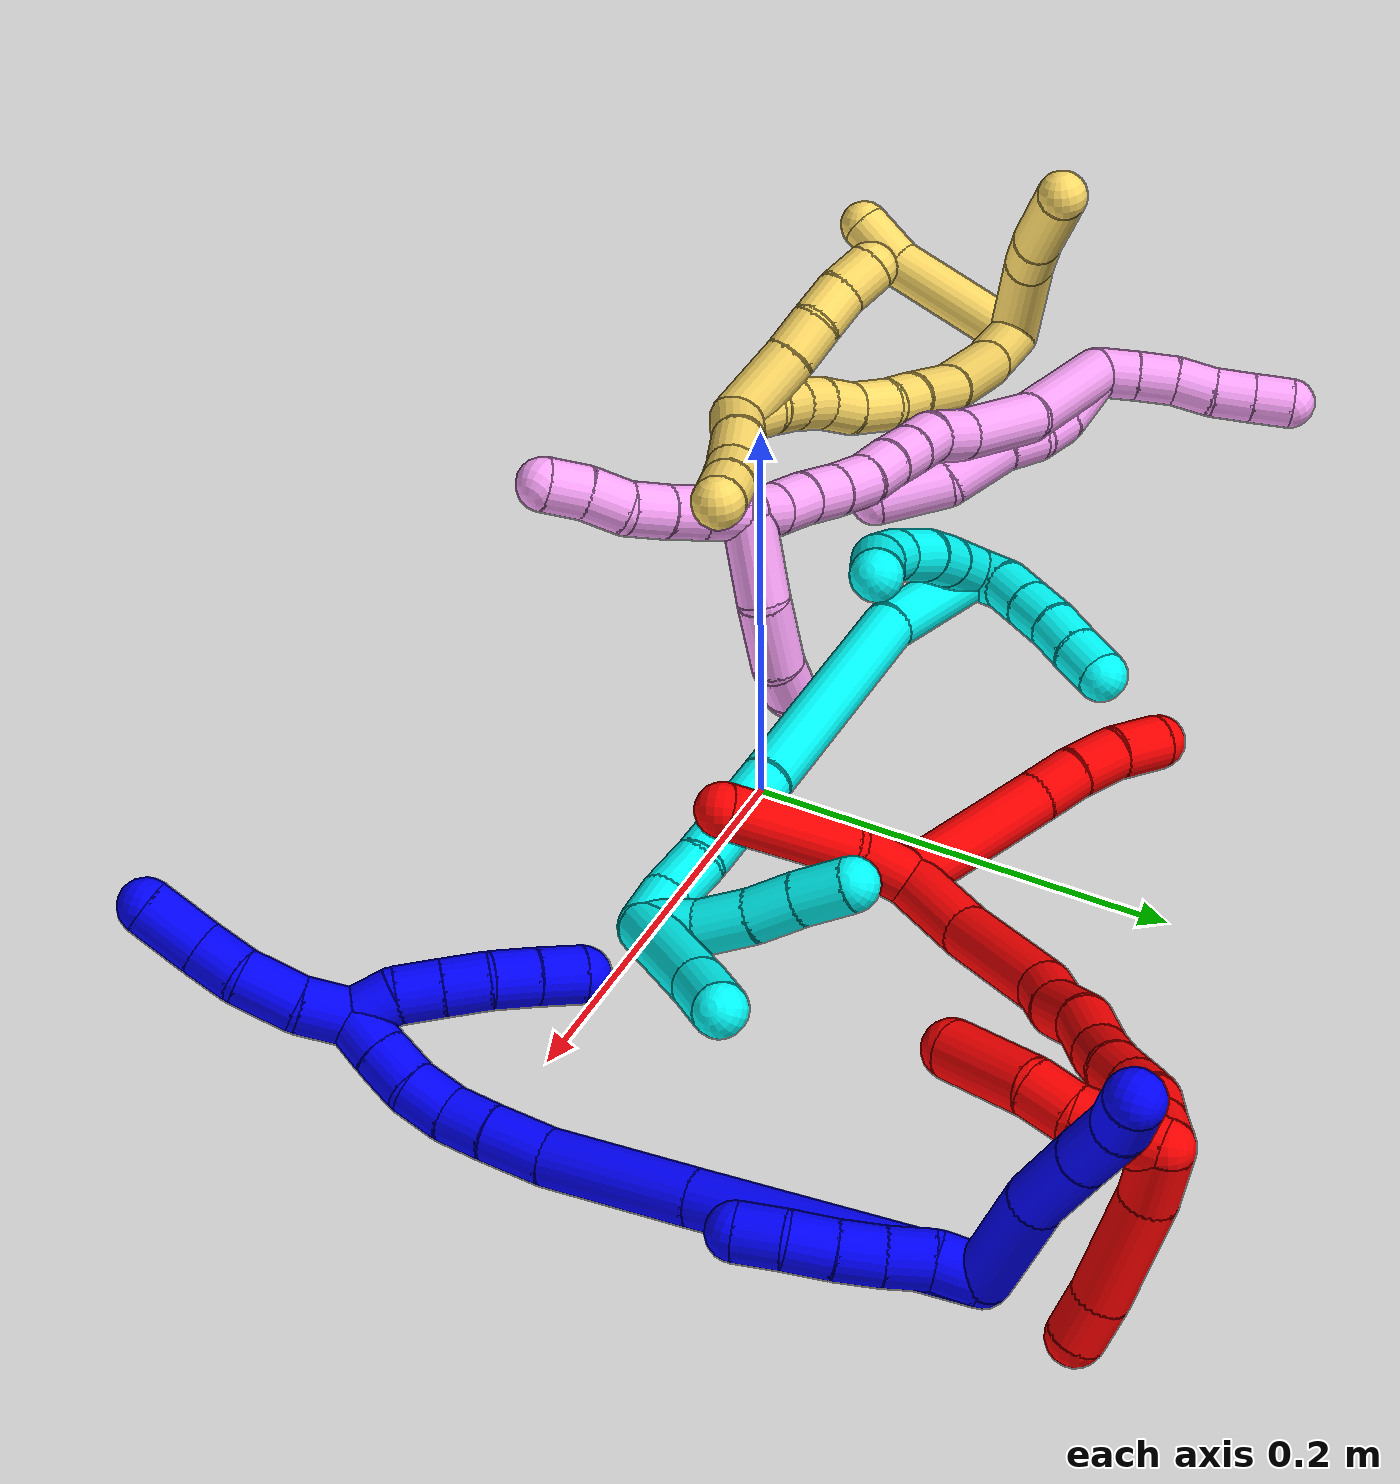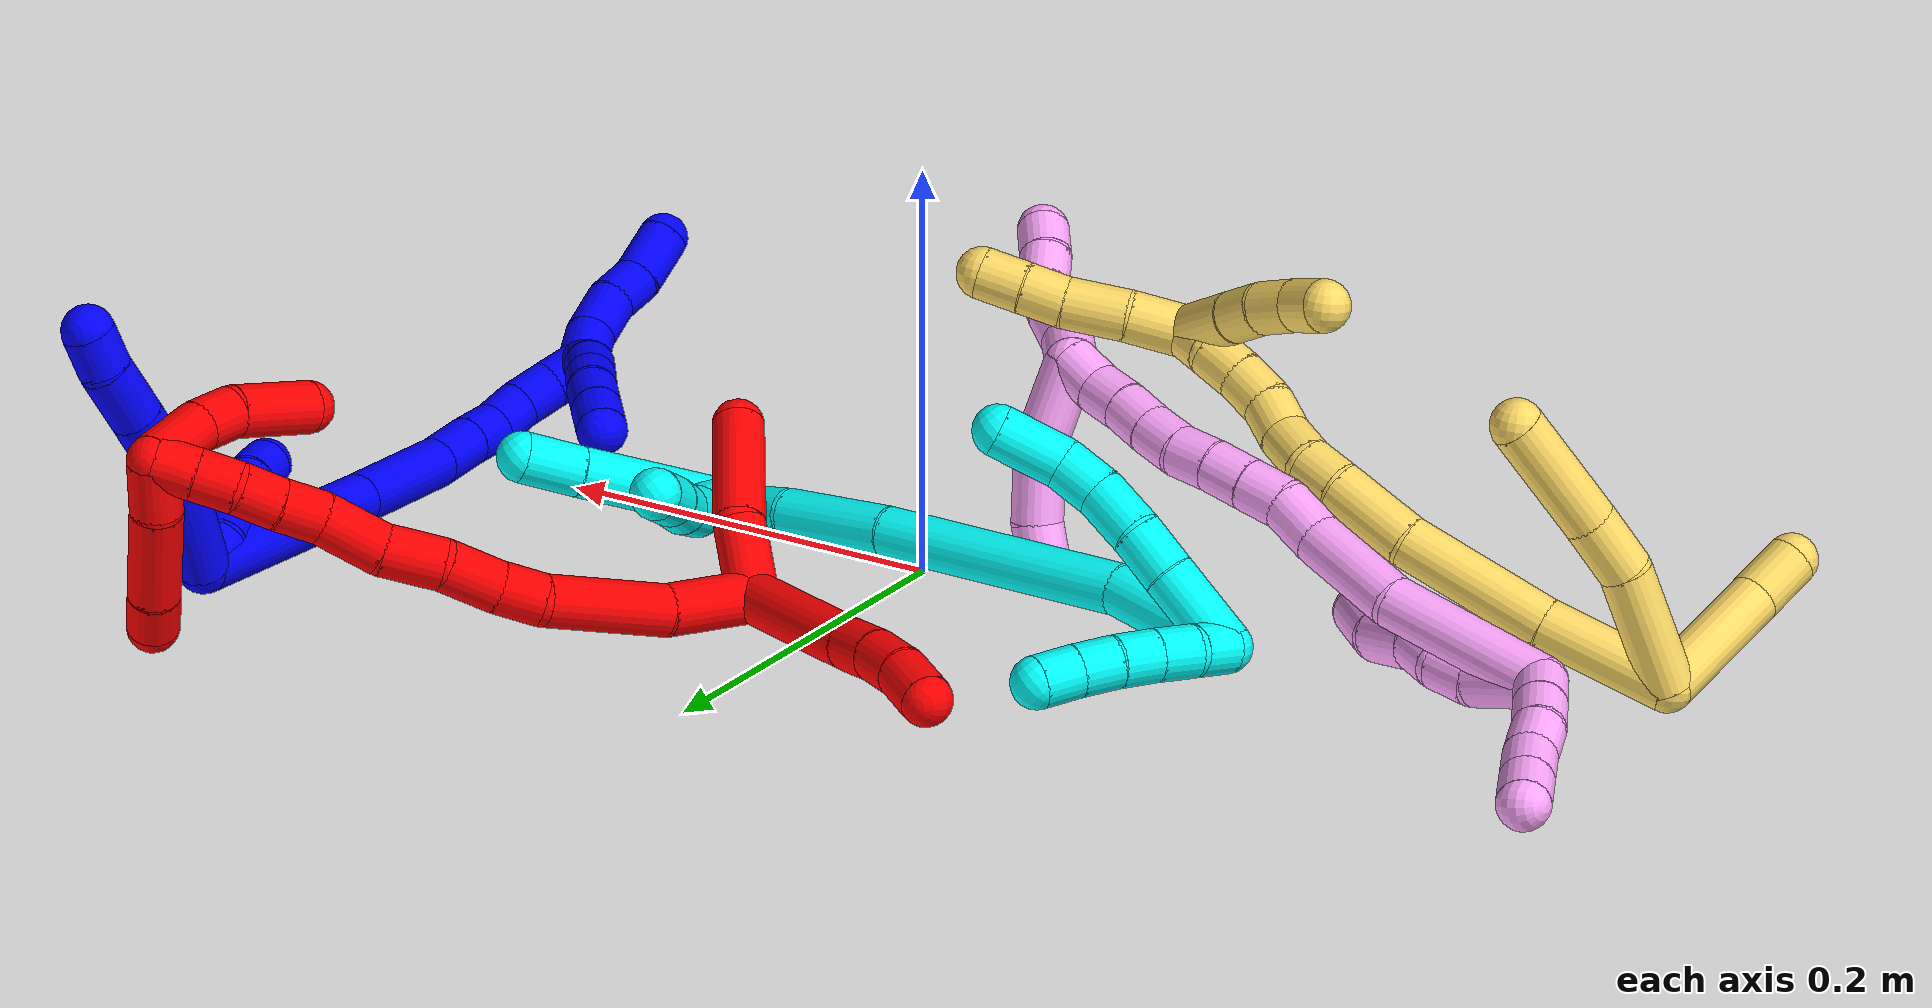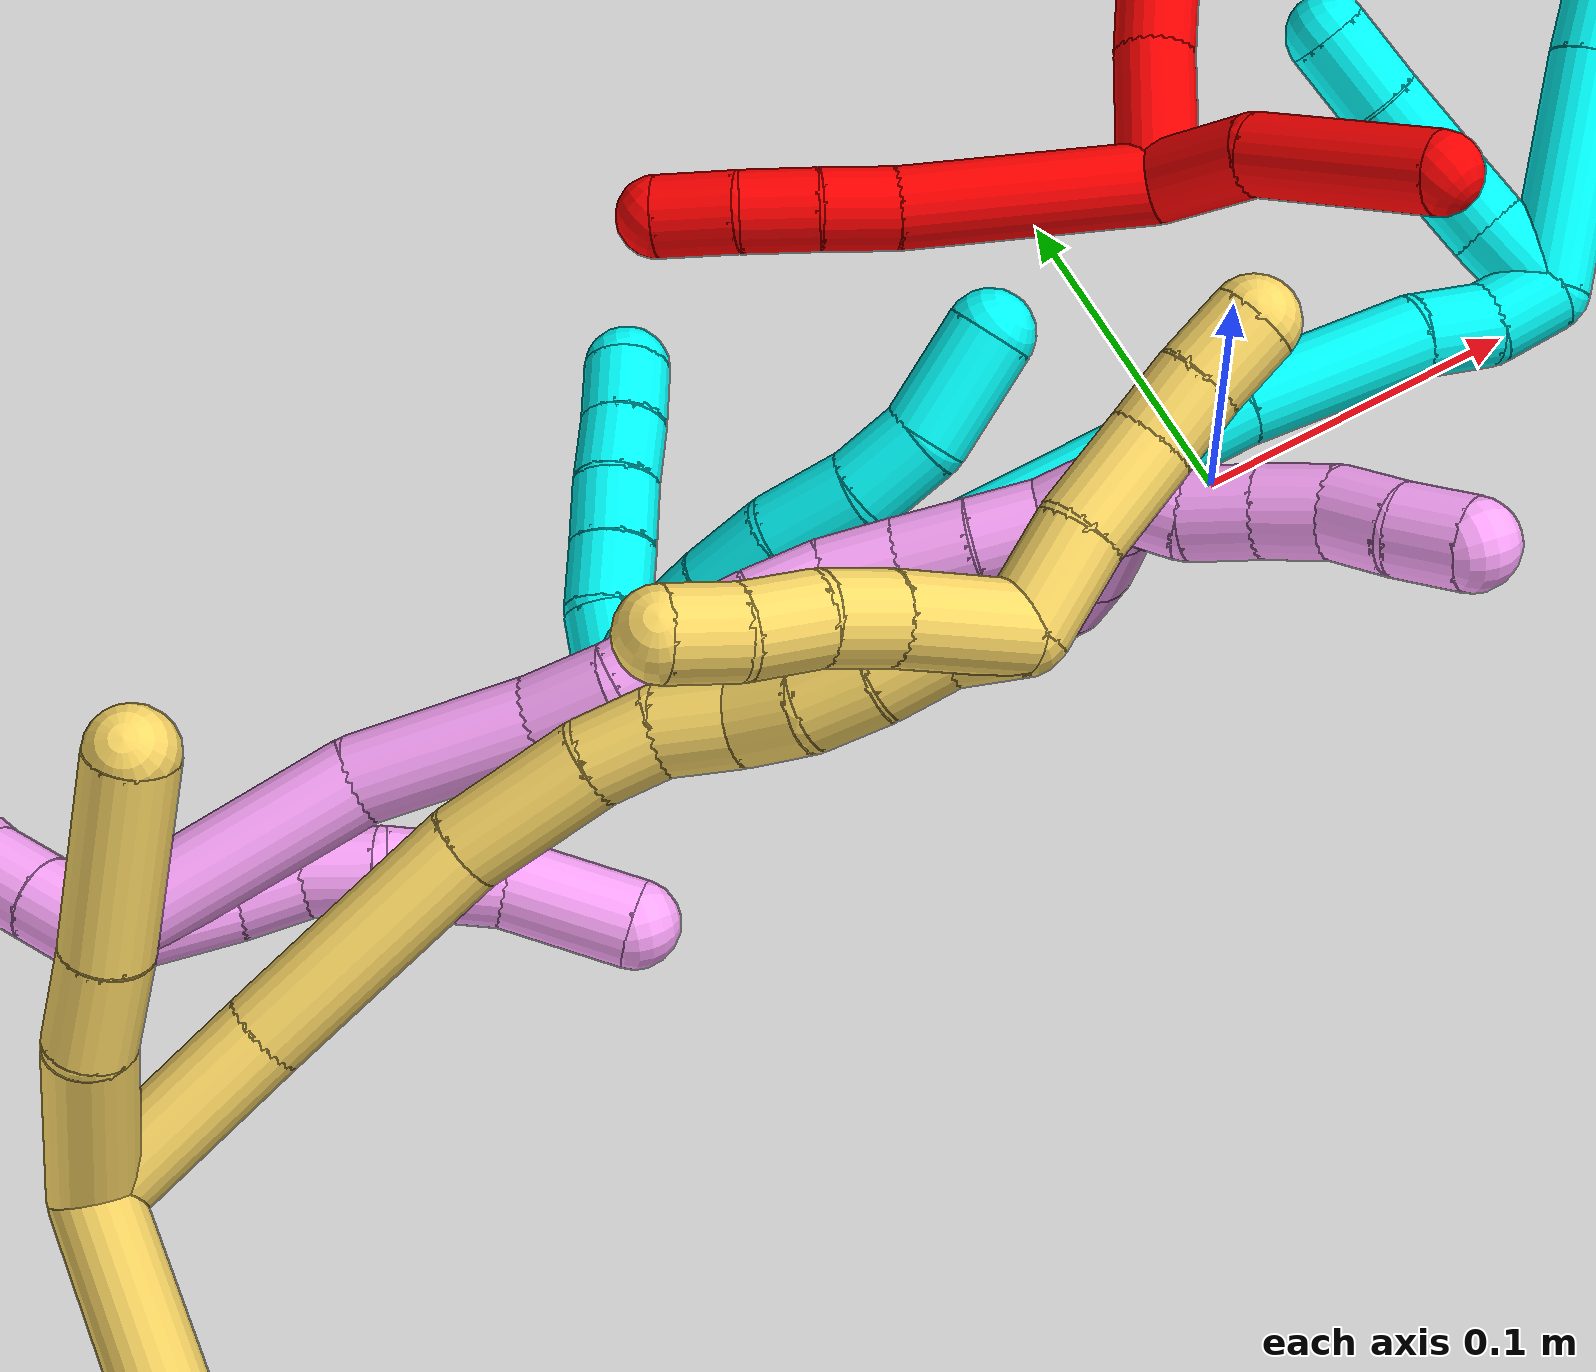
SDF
<sdf version="1.7">
 <world name="default">
  <plugin name="TubeGeneratorPlugin" filename="libtube_generator_plugin.so"/>
  <model name="photoneo_s_sensor">
   <static>1</static>
   <pose>0 0 2 1.57079 1.57079 3.14159</pose>
   <link name="link">
    <inertial><mass>0.1</mass></inertial>
    <sensor name="sensor" type="depth">
     <update_rate>30</update_rate>
     <camera>
      <horizontal_fov>1.22</horizontal_fov>
      <image><width>1920</width><height>1200</height><format>B8G8R8</format></image>
      <clip><near>0.1</near><far>4</far></clip>
      <depth_camera><output>points</output></depth_camera>
     </camera>
     <plugin name="camera_plugin" filename="libgazebo_ros_depth_camera.so">
      <baseline>0.2</baseline>
      <alwaysOn>1</alwaysOn>
      <updateRate>0.0</updateRate>
      <cameraName>camera_ir</cameraName>
      <imageTopicName>/camera/color/image_raw</imageTopicName>
      <cameraInfoTopicName>/camera/color/camera_info</cameraInfoTopicName>
      <depthImageTopicName>/camera/depth/image_raw</depthImageTopicName>
      <depthImageCameraInfoTopicName>/camera/depth/camera_info</depthImageCameraInfoTopicName>
      <pointCloudTopicName>/camera/depth/points</pointCloudTopicName>
      <frameName>fr_optical</frameName>
      <pointCloudCutoff>0.1</pointCloudCutoff>
      <pointCloudCutoffMax>2.0</pointCloudCutoffMax>
      <distortionK1>0</distortionK1>
      <distortionK2>0</distortionK2>
      <distortionK3>0</distortionK3>
      <distortionT1>0</distortionT1>
      <distortionT2>0</distortionT2>
      <CxPrime>0</CxPrime>
      <Cx>0</Cx>
      <Cy>0</Cy>
      <focalLength>0</focalLength>
      <hackBaseline>0</hackBaseline>
     </plugin>
    </sensor>
   </link>
  </model>
  <gravity>0 0 -9.8</gravity>
  <magnetic_field>6e-06 2.3e-05 -4.2e-05</magnetic_field>
  <atmosphere type="adiabatic"/>
  <physics name="default_physics" default="0" type="ode">
   <max_step_size>0.003</max_step_size>
   <real_time_factor>1</real_time_factor>
   <real_time_update_rate>1000</real_time_update_rate>
   <max_contacts>10000</max_contacts>
   <ode>
    <solver>
     <type>quick</type>
     <iters>100</iters>
     <sor>1.3</sor>
     <use_dynamic_moi_rescaling>0</use_dynamic_moi_rescaling>
    </solver>
    <constraints>
     <contact_max_correcting_vel>0</contact_max_correcting_vel>
     <contact_surface_layer>0.001</contact_surface_layer>
     <cfm>0</cfm>
     <erp>0.2</erp>
    </constraints>
   </ode>
  </physics>
  <scene><ambient>0.4 0.4 0.4 1</ambient><background>0.7 0.7 0.7 1</background><shadows>0</shadows></scene>
  <audio><device>default</device></audio>
  <spherical_coordinates>
   <surface_model>EARTH_WGS84</surface_model>
   <latitude_deg>0</latitude_deg>
   <longitude_deg>0</longitude_deg>
   <elevation>0</elevation>
   <heading_deg>0</heading_deg>
  </spherical_coordinates>
  <model name="bin">
   <static>1</static>
   <link name="bottom">
    <collision name="collision-bottom">
     <pose>0 0 -0.01 0 -0 0</pose>
     <geometry><box><size>0.8 0.6 0.02</size></box></geometry>
     <surface>
      <friction><ode><mu>100</mu><mu2>100</mu2></ode></friction>
      <contact><collide_bitmask>65535</collide_bitmask></contact>
     </surface>
    </collision>
   </link>
   <link name="west_wall">
    <collision name="collision-west_wall">
     <pose>-0.41 0 0.1 0 -0 0</pose>
     <geometry><box><size>0.02 0.6 0.2</size></box></geometry>
     <surface>
      <friction><ode><mu>100</mu><mu2>100</mu2></ode></friction>
      <contact><collide_bitmask>65535</collide_bitmask></contact>
     </surface>
    </collision>
   </link>
   <link name="east_wall">
    <collision name="collision-east_wall">
     <pose>0.41 0 0.1 0 -0 0</pose>
     <geometry><box><size>0.02 0.6 0.2</size></box></geometry>
     <surface>
      <friction><ode><mu>100</mu><mu2>100</mu2></ode></friction>
      <contact><collide_bitmask>65535</collide_bitmask></contact>
     </surface>
    </collision>
   </link>
   <link name="south_wall">
    <collision name="collision-south_wall">
     <pose>0 -0.31 0.1 0 -0 0</pose>
     <geometry><box><size>0.8 0.02 0.2</size></box></geometry>
     <surface>
      <friction><ode><mu>100</mu><mu2>100</mu2></ode></friction>
      <contact><collide_bitmask>65535</collide_bitmask></contact>
     </surface>
    </collision>
   </link>
   <link name="north_wall">
    <collision name="collision-north_wall">
     <pose>0 0.31 0.1 0 -0 0</pose>
     <geometry><box><size>0.8 0.02 0.2</size></box></geometry>
     <surface>
      <friction><ode><mu>100</mu><mu2>100</mu2></ode></friction>
      <contact><collide_bitmask>65535</collide_bitmask></contact>
     </surface>
    </collision>
   </link>
  </model>
  <model name="1">
   <static>0</static>
   <link name="1">
    <collision name="collision-cylinder-e_1_2_8">
     <pose>-0.014896 -0.019457 0.010737 1.06657 -0.590517 -0.355314</pose>
     <geometry><cylinder><radius>0.0125</radius><length>0.053507</length></cylinder></geometry>
     <surface>
      <friction><ode><mu>1.16</mu><mu2>1.16</mu2><slip1>0</slip1><slip2>0</slip2></ode></friction>
      <contact><ode><kp>1e+06</kp><kd>1</kd><max_vel>0</max_vel><min_depth>0.001</min_depth></ode></contact>
     </surface>
    </collision>
    <visual name="visual-cylinder-e_1_2_8">
     <pose>-0.014896 -0.019457 0.010737 1.06657 -0.590517 -0.355314</pose>
     <geometry><cylinder><radius>0.0125</radius><length>0.053507</length></cylinder></geometry>
     <material><ambient>0 0 1 1</ambient></material>
    </visual>
    <collision name="collision-cylinder-e_2_8_9">
     <pose>-0.038077 -0.056233 0.033144 0.977823 -0.377663 -0.202639</pose>
     <geometry><cylinder><radius>0.0125</radius><length>0.044936</length></cylinder></geometry>
     <surface>
      <friction><ode><mu>1.16</mu><mu2>1.16</mu2><slip1>0</slip1><slip2>0</slip2></ode></friction>
      <contact><ode><kp>1e+06</kp><kd>1</kd><max_vel>0</max_vel><min_depth>0.001</min_depth></ode></contact>
     </surface>
    </collision>
    <visual name="visual-cylinder-e_2_8_9">
     <pose>-0.038077 -0.056233 0.033144 0.977823 -0.377663 -0.202639</pose>
     <geometry><cylinder><radius>0.0125</radius><length>0.044936</length></cylinder></geometry>
     <material><ambient>0 0 1 1</ambient></material>
    </visual>
    <collision name="collision-cylinder-e_3_9_10">
     <pose>-0.051925 -0.085475 0.053048 0.966438 -0.366564 -0.193912</pose>
     <geometry><cylinder><radius>0.0125</radius><length>0.031039</length></cylinder></geometry>
     <surface>
      <friction><ode><mu>1.16</mu><mu2>1.16</mu2><slip1>0</slip1><slip2>0</slip2></ode></friction>
      <contact><ode><kp>1e+06</kp><kd>1</kd><max_vel>0</max_vel><min_depth>0.001</min_depth></ode></contact>
     </surface>
    </collision>
    <visual name="visual-cylinder-e_3_9_10">
     <pose>-0.051925 -0.085475 0.053048 0.966438 -0.366564 -0.193912</pose>
     <geometry><cylinder><radius>0.0125</radius><length>0.031039</length></cylinder></geometry>
     <material><ambient>0 0 1 1</ambient></material>
    </visual>
    <collision name="collision-cylinder-e_4_10_6">
     <pose>-0.06117 -0.106305 0.064791 1.19544 -0.367236 -0.251524</pose>
     <geometry><cylinder><radius>0.0125</radius><length>0.020518</length></cylinder></geometry>
     <surface>
      <friction><ode><mu>1.16</mu><mu2>1.16</mu2><slip1>0</slip1><slip2>0</slip2></ode></friction>
      <contact><ode><kp>1e+06</kp><kd>1</kd><max_vel>0</max_vel><min_depth>0.001</min_depth></ode></contact>
     </surface>
    </collision>
    <visual name="visual-cylinder-e_4_10_6">
     <pose>-0.06117 -0.106305 0.064791 1.19544 -0.367236 -0.251524</pose>
     <geometry><cylinder><radius>0.0125</radius><length>0.020518</length></cylinder></geometry>
     <material><ambient>0 0 1 1</ambient></material>
    </visual>
    <collision name="collision-cylinder-e_1_2_11">
     <pose>0.000889 -0.003845 -0.009188 2.74528 0.089056 0.436739</pose>
     <geometry><cylinder><radius>0.0125</radius><length>0.02</length></cylinder></geometry>
     <surface>
      <friction><ode><mu>1.16</mu><mu2>1.16</mu2><slip1>0</slip1><slip2>0</slip2></ode></friction>
      <contact><ode><kp>1e+06</kp><kd>1</kd><max_vel>0</max_vel><min_depth>0.001</min_depth></ode></contact>
     </surface>
    </collision>
    <visual name="visual-cylinder-e_1_2_11">
     <pose>0.000889 -0.003845 -0.009188 2.74528 0.089056 0.436739</pose>
     <geometry><cylinder><radius>0.0125</radius><length>0.02</length></cylinder></geometry>
     <material><ambient>0 0 1 1</ambient></material>
    </visual>
    <collision name="collision-cylinder-e_2_11_12">
     <pose>0.005342 -0.011284 -0.027001 2.74671 0.364276 1.48825</pose>
     <geometry><cylinder><radius>0.0125</radius><length>0.02</length></cylinder></geometry>
     <surface>
      <friction><ode><mu>1.16</mu><mu2>1.16</mu2><slip1>0</slip1><slip2>0</slip2></ode></friction>
      <contact><ode><kp>1e+06</kp><kd>1</kd><max_vel>0</max_vel><min_depth>0.001</min_depth></ode></contact>
     </surface>
    </collision>
    <visual name="visual-cylinder-e_2_11_12">
     <pose>0.005342 -0.011284 -0.027001 2.74671 0.364276 1.48825</pose>
     <geometry><cylinder><radius>0.0125</radius><length>0.02</length></cylinder></geometry>
     <material><ambient>0 0 1 1</ambient></material>
    </visual>
    <collision name="collision-cylinder-e_3_12_13">
     <pose>0.011855 -0.019119 -0.044189 2.68182 0.299541 1.14544</pose>
     <geometry><cylinder><radius>0.0125</radius><length>0.02</length></cylinder></geometry>
     <surface>
      <friction><ode><mu>1.16</mu><mu2>1.16</mu2><slip1>0</slip1><slip2>0</slip2></ode></friction>
      <contact><ode><kp>1e+06</kp><kd>1</kd><max_vel>0</max_vel><min_depth>0.001</min_depth></ode></contact>
     </surface>
    </collision>
    <visual name="visual-cylinder-e_3_12_13">
     <pose>0.011855 -0.019119 -0.044189 2.68182 0.299541 1.14544</pose>
     <geometry><cylinder><radius>0.0125</radius><length>0.02</length></cylinder></geometry>
     <material><ambient>0 0 1 1</ambient></material>
    </visual>
    <collision name="collision-cylinder-e_4_13_14">
     <pose>0.017143 -0.027541 -0.061529 2.69695 0.235885 0.965587</pose>
     <geometry><cylinder><radius>0.0125</radius><length>0.02</length></cylinder></geometry>
     <surface>
      <friction><ode><mu>1.16</mu><mu2>1.16</mu2><slip1>0</slip1><slip2>0</slip2></ode></friction>
      <contact><ode><kp>1e+06</kp><kd>1</kd><max_vel>0</max_vel><min_depth>0.001</min_depth></ode></contact>
     </surface>
    </collision>
    <visual name="visual-cylinder-e_4_13_14">
     <pose>0.017143 -0.027541 -0.061529 2.69695 0.235885 0.965587</pose>
     <geometry><cylinder><radius>0.0125</radius><length>0.02</length></cylinder></geometry>
     <material><ambient>0 0 1 1</ambient></material>
    </visual>
    <collision name="collision-cylinder-e_5_14_5">
     <pose>0.021878 -0.033864 -0.079776 2.91925 0.242182 1.65693</pose>
     <geometry><cylinder><radius>0.0125</radius><length>0.02</length></cylinder></geometry>
     <surface>
      <friction><ode><mu>1.16</mu><mu2>1.16</mu2><slip1>0</slip1><slip2>0</slip2></ode></friction>
      <contact><ode><kp>1e+06</kp><kd>1</kd><max_vel>0</max_vel><min_depth>0.001</min_depth></ode></contact>
     </surface>
    </collision>
    <visual name="visual-cylinder-e_5_14_5">
     <pose>0.021878 -0.033864 -0.079776 2.91925 0.242182 1.65693</pose>
     <geometry><cylinder><radius>0.0125</radius><length>0.02</length></cylinder></geometry>
     <material><ambient>0 0 1 1</ambient></material>
    </visual>
    <collision name="collision-cylinder-e_1_2_15">
     <pose>0.00675 -0.001693 -0.062875 3.11468 0.106909 2.64877</pose>
     <geometry><cylinder><radius>0.0125</radius><length>0.126517</length></cylinder></geometry>
     <surface>
      <friction><ode><mu>1.16</mu><mu2>1.16</mu2><slip1>0</slip1><slip2>0</slip2></ode></friction>
      <contact><ode><kp>1e+06</kp><kd>1</kd><max_vel>0</max_vel><min_depth>0.001</min_depth></ode></contact>
     </surface>
    </collision>
    <visual name="visual-cylinder-e_1_2_15">
     <pose>0.00675 -0.001693 -0.062875 3.11468 0.106909 2.64877</pose>
     <geometry><cylinder><radius>0.0125</radius><length>0.126517</length></cylinder></geometry>
     <material><ambient>0 0 1 1</ambient></material>
    </visual>
    <collision name="collision-cylinder-e_2_15_16">
     <pose>0.016958 -0.004793 -0.158766 3.09898 0.104257 2.36614</pose>
     <geometry><cylinder><radius>0.0125</radius><length>0.066454</length></cylinder></geometry>
     <surface>
      <friction><ode><mu>1.16</mu><mu2>1.16</mu2><slip1>0</slip1><slip2>0</slip2></ode></friction>
      <contact><ode><kp>1e+06</kp><kd>1</kd><max_vel>0</max_vel><min_depth>0.001</min_depth></ode></contact>
     </surface>
    </collision>
    <visual name="visual-cylinder-e_2_15_16">
     <pose>0.016958 -0.004793 -0.158766 3.09898 0.104257 2.36614</pose>
     <geometry><cylinder><radius>0.0125</radius><length>0.066454</length></cylinder></geometry>
     <material><ambient>0 0 1 1</ambient></material>
    </visual>
    <collision name="collision-cylinder-e_3_16_17">
     <pose>0.020404 -0.00808 -0.205086 3.00126 -0.000852 -0.012122</pose>
     <geometry><cylinder><radius>0.0125</radius><length>0.026871</length></cylinder></geometry>
     <surface>
      <friction><ode><mu>1.16</mu><mu2>1.16</mu2><slip1>0</slip1><slip2>0</slip2></ode></friction>
      <contact><ode><kp>1e+06</kp><kd>1</kd><max_vel>0</max_vel><min_depth>0.001</min_depth></ode></contact>
     </surface>
    </collision>
    <visual name="visual-cylinder-e_3_16_17">
     <pose>0.020404 -0.00808 -0.205086 3.00126 -0.000852 -0.012122</pose>
     <geometry><cylinder><radius>0.0125</radius><length>0.026871</length></cylinder></geometry>
     <material><ambient>0 0 1 1</ambient></material>
    </visual>
    <collision name="collision-cylinder-e_4_17_18">
     <pose>0.020004 -0.0109 -0.228363 3.04752 -0.038822 -0.782384</pose>
     <geometry><cylinder><radius>0.0125</radius><length>0.02005</length></cylinder></geometry>
     <surface>
      <friction><ode><mu>1.16</mu><mu2>1.16</mu2><slip1>0</slip1><slip2>0</slip2></ode></friction>
      <contact><ode><kp>1e+06</kp><kd>1</kd><max_vel>0</max_vel><min_depth>0.001</min_depth></ode></contact>
     </surface>
    </collision>
    <visual name="visual-cylinder-e_4_17_18">
     <pose>0.020004 -0.0109 -0.228363 3.04752 -0.038822 -0.782384</pose>
     <geometry><cylinder><radius>0.0125</radius><length>0.02005</length></cylinder></geometry>
     <material><ambient>0 0 1 1</ambient></material>
    </visual>
    <collision name="collision-cylinder-e_5_18_19">
     <pose>0.01763 -0.014388 -0.247835 2.87963 -0.19916 -1.29773</pose>
     <geometry><cylinder><radius>0.0125</radius><length>0.020066</length></cylinder></geometry>
     <surface>
      <friction><ode><mu>1.16</mu><mu2>1.16</mu2><slip1>0</slip1><slip2>0</slip2></ode></friction>
      <contact><ode><kp>1e+06</kp><kd>1</kd><max_vel>0</max_vel><min_depth>0.001</min_depth></ode></contact>
     </surface>
    </collision>
    <visual name="visual-cylinder-e_5_18_19">
     <pose>0.01763 -0.014388 -0.247835 2.87963 -0.19916 -1.29773</pose>
     <geometry><cylinder><radius>0.0125</radius><length>0.020066</length></cylinder></geometry>
     <material><ambient>0 0 1 1</ambient></material>
    </visual>
    <collision name="collision-cylinder-e_6_19_20">
     <pose>0.011654 -0.01847 -0.26638 2.97347 -0.410226 -2.37194</pose>
     <geometry><cylinder><radius>0.0125</radius><length>0.020013</length></cylinder></geometry>
     <surface>
      <friction><ode><mu>1.16</mu><mu2>1.16</mu2><slip1>0</slip1><slip2>0</slip2></ode></friction>
      <contact><ode><kp>1e+06</kp><kd>1</kd><max_vel>0</max_vel><min_depth>0.001</min_depth></ode></contact>
     </surface>
    </collision>
    <visual name="visual-cylinder-e_6_19_20">
     <pose>0.011654 -0.01847 -0.26638 2.97347 -0.410226 -2.37194</pose>
     <geometry><cylinder><radius>0.0125</radius><length>0.020013</length></cylinder></geometry>
     <material><ambient>0 0 1 1</ambient></material>
    </visual>
    <collision name="collision-cylinder-e_7_20_1">
     <pose>0.003238 -0.021426 -0.284298 2.98281 -0.457725 -2.48336</pose>
     <geometry><cylinder><radius>0.0125</radius><length>0.020029</length></cylinder></geometry>
     <surface>
      <friction><ode><mu>1.16</mu><mu2>1.16</mu2><slip1>0</slip1><slip2>0</slip2></ode></friction>
      <contact><ode><kp>1e+06</kp><kd>1</kd><max_vel>0</max_vel><min_depth>0.001</min_depth></ode></contact>
     </surface>
    </collision>
    <visual name="visual-cylinder-e_7_20_1">
     <pose>0.003238 -0.021426 -0.284298 2.98281 -0.457725 -2.48336</pose>
     <geometry><cylinder><radius>0.0125</radius><length>0.020029</length></cylinder></geometry>
     <material><ambient>0 0 1 1</ambient></material>
    </visual>
    <collision name="collision-cylinder-e_1_1_21">
     <pose>-0.008974 -0.021605 -0.287018 -0.199186 -0.892424 0.095533</pose>
     <geometry><cylinder><radius>0.0125</radius><length>0.02</length></cylinder></geometry>
     <surface>
      <friction><ode><mu>1.16</mu><mu2>1.16</mu2><slip1>0</slip1><slip2>0</slip2></ode></friction>
      <contact><ode><kp>1e+06</kp><kd>1</kd><max_vel>0</max_vel><min_depth>0.001</min_depth></ode></contact>
     </surface>
    </collision>
    <visual name="visual-cylinder-e_1_1_21">
     <pose>-0.008974 -0.021605 -0.287018 -0.199186 -0.892424 0.095533</pose>
     <geometry><cylinder><radius>0.0125</radius><length>0.02</length></cylinder></geometry>
     <material><ambient>0 0 1 1</ambient></material>
    </visual>
    <collision name="collision-cylinder-e_2_21_22">
     <pose>-0.022408 -0.017114 -0.273281 -0.404758 -0.600182 0.126815</pose>
     <geometry><cylinder><radius>0.0125</radius><length>0.02</length></cylinder></geometry>
     <surface>
      <friction><ode><mu>1.16</mu><mu2>1.16</mu2><slip1>0</slip1><slip2>0</slip2></ode></friction>
      <contact><ode><kp>1e+06</kp><kd>1</kd><max_vel>0</max_vel><min_depth>0.001</min_depth></ode></contact>
     </surface>
    </collision>
    <visual name="visual-cylinder-e_2_21_22">
     <pose>-0.022408 -0.017114 -0.273281 -0.404758 -0.600182 0.126815</pose>
     <geometry><cylinder><radius>0.0125</radius><length>0.02</length></cylinder></geometry>
     <material><ambient>0 0 1 1</ambient></material>
    </visual>
    <collision name="collision-cylinder-e_3_22_23">
     <pose>-0.033675 -0.01053 -0.258125 -0.414829 -0.59671 0.129255</pose>
     <geometry><cylinder><radius>0.0125</radius><length>0.02</length></cylinder></geometry>
     <surface>
      <friction><ode><mu>1.16</mu><mu2>1.16</mu2><slip1>0</slip1><slip2>0</slip2></ode></friction>
      <contact><ode><kp>1e+06</kp><kd>1</kd><max_vel>0</max_vel><min_depth>0.001</min_depth></ode></contact>
     </surface>
    </collision>
    <visual name="visual-cylinder-e_3_22_23">
     <pose>-0.033675 -0.01053 -0.258125 -0.414829 -0.59671 0.129255</pose>
     <geometry><cylinder><radius>0.0125</radius><length>0.02</length></cylinder></geometry>
     <material><ambient>0 0 1 1</ambient></material>
    </visual>
    <collision name="collision-cylinder-e_4_23_24">
     <pose>-0.0444 -0.002082 -0.243643 -0.637016 -0.535911 0.180571</pose>
     <geometry><cylinder><radius>0.0125</radius><length>0.02</length></cylinder></geometry>
     <surface>
      <friction><ode><mu>1.16</mu><mu2>1.16</mu2><slip1>0</slip1><slip2>0</slip2></ode></friction>
      <contact><ode><kp>1e+06</kp><kd>1</kd><max_vel>0</max_vel><min_depth>0.001</min_depth></ode></contact>
     </surface>
    </collision>
    <visual name="visual-cylinder-e_4_23_24">
     <pose>-0.0444 -0.002082 -0.243643 -0.637016 -0.535911 0.180571</pose>
     <geometry><cylinder><radius>0.0125</radius><length>0.02</length></cylinder></geometry>
     <material><ambient>0 0 1 1</ambient></material>
    </visual>
    <collision name="collision-cylinder-e_5_24_4">
     <pose>-0.054406 0.008486 -0.229931 -0.675988 -0.51203 0.18349</pose>
     <geometry><cylinder><radius>0.0125</radius><length>0.02</length></cylinder></geometry>
     <surface>
      <friction><ode><mu>1.16</mu><mu2>1.16</mu2><slip1>0</slip1><slip2>0</slip2></ode></friction>
      <contact><ode><kp>1e+06</kp><kd>1</kd><max_vel>0</max_vel><min_depth>0.001</min_depth></ode></contact>
     </surface>
    </collision>
    <visual name="visual-cylinder-e_5_24_4">
     <pose>-0.054406 0.008486 -0.229931 -0.675988 -0.51203 0.18349</pose>
     <geometry><cylinder><radius>0.0125</radius><length>0.02</length></cylinder></geometry>
     <material><ambient>0 0 1 1</ambient></material>
    </visual>
    <collision name="collision-cylinder-e_1_1_25">
     <pose>0.001218 -0.028925 -0.302786 2.57793 0.208411 0.693248</pose>
     <geometry><cylinder><radius>0.0125</radius><length>0.023257</length></cylinder></geometry>
     <surface>
      <friction><ode><mu>1.16</mu><mu2>1.16</mu2><slip1>0</slip1><slip2>0</slip2></ode></friction>
      <contact><ode><kp>1e+06</kp><kd>1</kd><max_vel>0</max_vel><min_depth>0.001</min_depth></ode></contact>
     </surface>
    </collision>
    <visual name="visual-cylinder-e_1_1_25">
     <pose>0.001218 -0.028925 -0.302786 2.57793 0.208411 0.693248</pose>
     <geometry><cylinder><radius>0.0125</radius><length>0.023257</length></cylinder></geometry>
     <material><ambient>0 0 1 1</ambient></material>
    </visual>
    <collision name="collision-cylinder-e_2_25_26">
     <pose>0.003411 -0.04104 -0.324388 2.67506 -0.015912 -0.066948</pose>
     <geometry><cylinder><radius>0.0125</radius><length>0.026842</length></cylinder></geometry>
     <surface>
      <friction><ode><mu>1.16</mu><mu2>1.16</mu2><slip1>0</slip1><slip2>0</slip2></ode></friction>
      <contact><ode><kp>1e+06</kp><kd>1</kd><max_vel>0</max_vel><min_depth>0.001</min_depth></ode></contact>
     </surface>
    </collision>
    <visual name="visual-cylinder-e_2_25_26">
     <pose>0.003411 -0.04104 -0.324388 2.67506 -0.015912 -0.066948</pose>
     <geometry><cylinder><radius>0.0125</radius><length>0.026842</length></cylinder></geometry>
     <material><ambient>0 0 1 1</ambient></material>
    </visual>
    <collision name="collision-cylinder-e_3_26_27">
     <pose>0.001161 -0.049766 -0.346358 2.87836 -0.194407 -1.26972</pose>
     <geometry><cylinder><radius>0.0125</radius><length>0.021079</length></cylinder></geometry>
     <surface>
      <friction><ode><mu>1.16</mu><mu2>1.16</mu2><slip1>0</slip1><slip2>0</slip2></ode></friction>
      <contact><ode><kp>1e+06</kp><kd>1</kd><max_vel>0</max_vel><min_depth>0.001</min_depth></ode></contact>
     </surface>
    </collision>
    <visual name="visual-cylinder-e_3_26_27">
     <pose>0.001161 -0.049766 -0.346358 2.87836 -0.194407 -1.26972</pose>
     <geometry><cylinder><radius>0.0125</radius><length>0.021079</length></cylinder></geometry>
     <material><ambient>0 0 1 1</ambient></material>
    </visual>
    <collision name="collision-cylinder-e_4_27_3">
     <pose>-0.003777 -0.059561 -0.36854 2.61423 -0.202765 -0.720739</pose>
     <geometry><cylinder><radius>0.0125</radius><length>0.028822</length></cylinder></geometry>
     <surface>
      <friction><ode><mu>1.16</mu><mu2>1.16</mu2><slip1>0</slip1><slip2>0</slip2></ode></friction>
      <contact><ode><kp>1e+06</kp><kd>1</kd><max_vel>0</max_vel><min_depth>0.001</min_depth></ode></contact>
     </surface>
    </collision>
    <visual name="visual-cylinder-e_4_27_3">
     <pose>-0.003777 -0.059561 -0.36854 2.61423 -0.202765 -0.720739</pose>
     <geometry><cylinder><radius>0.0125</radius><length>0.028822</length></cylinder></geometry>
     <material><ambient>0 0 1 1</ambient></material>
    </visual>
    <collision name="collision-sphere-3">
     <pose>-0.006679 -0.066665 -0.380738 0 -0 0</pose>
     <geometry><sphere><radius>0.0125</radius></sphere></geometry>
     <surface>
      <friction><ode><mu>1.16</mu><mu2>1.16</mu2><slip1>0</slip1><slip2>0</slip2></ode></friction>
      <contact><ode><kp>1e+06</kp><kd>1</kd><max_vel>0</max_vel><min_depth>0.001</min_depth></ode></contact>
     </surface>
    </collision>
    <visual name="visual-sphere-3">
     <pose>-0.006679 -0.066665 -0.380738 0 -0 0</pose>
     <geometry><sphere><radius>0.0125</radius></sphere></geometry>
     <material><ambient>0 0 1 1</ambient></material>
    </visual>
    <collision name="collision-sphere-27">
     <pose>-0.000875 -0.052457 -0.356342 0 -0 0</pose>
     <geometry><sphere><radius>0.0125</radius></sphere></geometry>
     <surface>
      <friction><ode><mu>1.16</mu><mu2>1.16</mu2><slip1>0</slip1><slip2>0</slip2></ode></friction>
      <contact><ode><kp>1e+06</kp><kd>1</kd><max_vel>0</max_vel><min_depth>0.001</min_depth></ode></contact>
     </surface>
    </collision>
    <visual name="visual-sphere-27">
     <pose>-0.000875 -0.052457 -0.356342 0 -0 0</pose>
     <geometry><sphere><radius>0.0125</radius></sphere></geometry>
     <material><ambient>0 0 1 1</ambient></material>
    </visual>
    <collision name="collision-sphere-26">
     <pose>0.003197 -0.047076 -0.336373 0 -0 0</pose>
     <geometry><sphere><radius>0.0125</radius></sphere></geometry>
     <surface>
      <friction><ode><mu>1.16</mu><mu2>1.16</mu2><slip1>0</slip1><slip2>0</slip2></ode></friction>
      <contact><ode><kp>1e+06</kp><kd>1</kd><max_vel>0</max_vel><min_depth>0.001</min_depth></ode></contact>
     </surface>
    </collision>
    <visual name="visual-sphere-26">
     <pose>0.003197 -0.047076 -0.336373 0 -0 0</pose>
     <geometry><sphere><radius>0.0125</radius></sphere></geometry>
     <material><ambient>0 0 1 1</ambient></material>
    </visual>
    <collision name="collision-sphere-25">
     <pose>0.003624 -0.035004 -0.312403 0 -0 0</pose>
     <geometry><sphere><radius>0.0125</radius></sphere></geometry>
     <surface>
      <friction><ode><mu>1.16</mu><mu2>1.16</mu2><slip1>0</slip1><slip2>0</slip2></ode></friction>
      <contact><ode><kp>1e+06</kp><kd>1</kd><max_vel>0</max_vel><min_depth>0.001</min_depth></ode></contact>
     </surface>
    </collision>
    <visual name="visual-sphere-25">
     <pose>0.003624 -0.035004 -0.312403 0 -0 0</pose>
     <geometry><sphere><radius>0.0125</radius></sphere></geometry>
     <material><ambient>0 0 1 1</ambient></material>
    </visual>
    <collision name="collision-sphere-4">
     <pose>-0.059305 0.013941 -0.22313 0 -0 0</pose>
     <geometry><sphere><radius>0.0125</radius></sphere></geometry>
     <surface>
      <friction><ode><mu>1.16</mu><mu2>1.16</mu2><slip1>0</slip1><slip2>0</slip2></ode></friction>
      <contact><ode><kp>1e+06</kp><kd>1</kd><max_vel>0</max_vel><min_depth>0.001</min_depth></ode></contact>
     </surface>
    </collision>
    <visual name="visual-sphere-4">
     <pose>-0.059305 0.013941 -0.22313 0 -0 0</pose>
     <geometry><sphere><radius>0.0125</radius></sphere></geometry>
     <material><ambient>0 0 1 1</ambient></material>
    </visual>
    <collision name="collision-sphere-24">
     <pose>-0.049506 0.003032 -0.236731 0 -0 0</pose>
     <geometry><sphere><radius>0.0125</radius></sphere></geometry>
     <surface>
      <friction><ode><mu>1.16</mu><mu2>1.16</mu2><slip1>0</slip1><slip2>0</slip2></ode></friction>
      <contact><ode><kp>1e+06</kp><kd>1</kd><max_vel>0</max_vel><min_depth>0.001</min_depth></ode></contact>
     </surface>
    </collision>
    <visual name="visual-sphere-24">
     <pose>-0.049506 0.003032 -0.236731 0 -0 0</pose>
     <geometry><sphere><radius>0.0125</radius></sphere></geometry>
     <material><ambient>0 0 1 1</ambient></material>
    </visual>
    <collision name="collision-sphere-23">
     <pose>-0.039294 -0.007196 -0.250555 0 -0 0</pose>
     <geometry><sphere><radius>0.0125</radius></sphere></geometry>
     <surface>
      <friction><ode><mu>1.16</mu><mu2>1.16</mu2><slip1>0</slip1><slip2>0</slip2></ode></friction>
      <contact><ode><kp>1e+06</kp><kd>1</kd><max_vel>0</max_vel><min_depth>0.001</min_depth></ode></contact>
     </surface>
    </collision>
    <visual name="visual-sphere-23">
     <pose>-0.039294 -0.007196 -0.250555 0 -0 0</pose>
     <geometry><sphere><radius>0.0125</radius></sphere></geometry>
     <material><ambient>0 0 1 1</ambient></material>
    </visual>
    <collision name="collision-sphere-22">
     <pose>-0.028056 -0.013864 -0.265695 0 -0 0</pose>
     <geometry><sphere><radius>0.0125</radius></sphere></geometry>
     <surface>
      <friction><ode><mu>1.16</mu><mu2>1.16</mu2><slip1>0</slip1><slip2>0</slip2></ode></friction>
      <contact><ode><kp>1e+06</kp><kd>1</kd><max_vel>0</max_vel><min_depth>0.001</min_depth></ode></contact>
     </surface>
    </collision>
    <visual name="visual-sphere-22">
     <pose>-0.028056 -0.013864 -0.265695 0 -0 0</pose>
     <geometry><sphere><radius>0.0125</radius></sphere></geometry>
     <material><ambient>0 0 1 1</ambient></material>
    </visual>
    <collision name="collision-sphere-21">
     <pose>-0.01676 -0.020363 -0.280866 0 -0 0</pose>
     <geometry><sphere><radius>0.0125</radius></sphere></geometry>
     <surface>
      <friction><ode><mu>1.16</mu><mu2>1.16</mu2><slip1>0</slip1><slip2>0</slip2></ode></friction>
      <contact><ode><kp>1e+06</kp><kd>1</kd><max_vel>0</max_vel><min_depth>0.001</min_depth></ode></contact>
     </surface>
    </collision>
    <visual name="visual-sphere-21">
     <pose>-0.01676 -0.020363 -0.280866 0 -0 0</pose>
     <geometry><sphere><radius>0.0125</radius></sphere></geometry>
     <material><ambient>0 0 1 1</ambient></material>
    </visual>
    <collision name="collision-sphere-1">
     <pose>-0.001188 -0.022847 -0.293169 0 -0 0</pose>
     <geometry><sphere><radius>0.0125</radius></sphere></geometry>
     <surface>
      <friction><ode><mu>1.16</mu><mu2>1.16</mu2><slip1>0</slip1><slip2>0</slip2></ode></friction>
      <contact><ode><kp>1e+06</kp><kd>1</kd><max_vel>0</max_vel><min_depth>0.001</min_depth></ode></contact>
     </surface>
    </collision>
    <visual name="visual-sphere-1">
     <pose>-0.001188 -0.022847 -0.293169 0 -0 0</pose>
     <geometry><sphere><radius>0.0125</radius></sphere></geometry>
     <material><ambient>0 0 1 1</ambient></material>
    </visual>
    <collision name="collision-sphere-11">
     <pose>0.001779 -0.00769 -0.018377 0 -0 0</pose>
     <geometry><sphere><radius>0.0125</radius></sphere></geometry>
     <surface>
      <friction><ode><mu>1.16</mu><mu2>1.16</mu2><slip1>0</slip1><slip2>0</slip2></ode></friction>
      <contact><ode><kp>1e+06</kp><kd>1</kd><max_vel>0</max_vel><min_depth>0.001</min_depth></ode></contact>
     </surface>
    </collision>
    <visual name="visual-sphere-11">
     <pose>0.001779 -0.00769 -0.018377 0 -0 0</pose>
     <geometry><sphere><radius>0.0125</radius></sphere></geometry>
     <material><ambient>0 0 1 1</ambient></material>
    </visual>
    <collision name="collision-sphere-6">
     <pose>-0.064854 -0.115214 0.068301 0 -0 0</pose>
     <geometry><sphere><radius>0.0125</radius></sphere></geometry>
     <surface>
      <friction><ode><mu>1.16</mu><mu2>1.16</mu2><slip1>0</slip1><slip2>0</slip2></ode></friction>
      <contact><ode><kp>1e+06</kp><kd>1</kd><max_vel>0</max_vel><min_depth>0.001</min_depth></ode></contact>
     </surface>
    </collision>
    <visual name="visual-sphere-6">
     <pose>-0.064854 -0.115214 0.068301 0 -0 0</pose>
     <geometry><sphere><radius>0.0125</radius></sphere></geometry>
     <material><ambient>0 0 1 1</ambient></material>
    </visual>
    <collision name="collision-sphere-10">
     <pose>-0.057487 -0.097397 0.061281 0 -0 0</pose>
     <geometry><sphere><radius>0.0125</radius></sphere></geometry>
     <surface>
      <friction><ode><mu>1.16</mu><mu2>1.16</mu2><slip1>0</slip1><slip2>0</slip2></ode></friction>
      <contact><ode><kp>1e+06</kp><kd>1</kd><max_vel>0</max_vel><min_depth>0.001</min_depth></ode></contact>
     </surface>
    </collision>
    <visual name="visual-sphere-10">
     <pose>-0.057487 -0.097397 0.061281 0 -0 0</pose>
     <geometry><sphere><radius>0.0125</radius></sphere></geometry>
     <material><ambient>0 0 1 1</ambient></material>
    </visual>
    <collision name="collision-sphere-9">
     <pose>-0.046362 -0.073553 0.044815 0 -0 0</pose>
     <geometry><sphere><radius>0.0125</radius></sphere></geometry>
     <surface>
      <friction><ode><mu>1.16</mu><mu2>1.16</mu2><slip1>0</slip1><slip2>0</slip2></ode></friction>
      <contact><ode><kp>1e+06</kp><kd>1</kd><max_vel>0</max_vel><min_depth>0.001</min_depth></ode></contact>
     </surface>
    </collision>
    <visual name="visual-sphere-9">
     <pose>-0.046362 -0.073553 0.044815 0 -0 0</pose>
     <geometry><sphere><radius>0.0125</radius></sphere></geometry>
     <material><ambient>0 0 1 1</ambient></material>
    </visual>
    <collision name="collision-sphere-2">
     <geometry><sphere><radius>0.0125</radius></sphere></geometry>
     <surface>
      <friction><ode><mu>1.16</mu><mu2>1.16</mu2><slip1>0</slip1><slip2>0</slip2></ode></friction>
      <contact><ode><kp>1e+06</kp><kd>1</kd><max_vel>0</max_vel><min_depth>0.001</min_depth></ode></contact>
     </surface>
    </collision>
    <visual name="visual-sphere-2">
     <geometry><sphere><radius>0.0125</radius></sphere></geometry>
     <material><ambient>0 0 1 1</ambient></material>
    </visual>
    <collision name="collision-sphere-19">
     <pose>0.015645 -0.016935 -0.257333 0 -0 0</pose>
     <geometry><sphere><radius>0.0125</radius></sphere></geometry>
     <surface>
      <friction><ode><mu>1.16</mu><mu2>1.16</mu2><slip1>0</slip1><slip2>0</slip2></ode></friction>
      <contact><ode><kp>1e+06</kp><kd>1</kd><max_vel>0</max_vel><min_depth>0.001</min_depth></ode></contact>
     </surface>
    </collision>
    <visual name="visual-sphere-19">
     <pose>0.015645 -0.016935 -0.257333 0 -0 0</pose>
     <geometry><sphere><radius>0.0125</radius></sphere></geometry>
     <material><ambient>0 0 1 1</ambient></material>
    </visual>
    <collision name="collision-sphere-8">
     <pose>-0.029792 -0.038914 0.021473 0 -0 0</pose>
     <geometry><sphere><radius>0.0125</radius></sphere></geometry>
     <surface>
      <friction><ode><mu>1.16</mu><mu2>1.16</mu2><slip1>0</slip1><slip2>0</slip2></ode></friction>
      <contact><ode><kp>1e+06</kp><kd>1</kd><max_vel>0</max_vel><min_depth>0.001</min_depth></ode></contact>
     </surface>
    </collision>
    <visual name="visual-sphere-8">
     <pose>-0.029792 -0.038914 0.021473 0 -0 0</pose>
     <geometry><sphere><radius>0.0125</radius></sphere></geometry>
     <material><ambient>0 0 1 1</ambient></material>
    </visual>
    <collision name="collision-sphere-12">
     <pose>0.008904 -0.014879 -0.035626 0 -0 0</pose>
     <geometry><sphere><radius>0.0125</radius></sphere></geometry>
     <surface>
      <friction><ode><mu>1.16</mu><mu2>1.16</mu2><slip1>0</slip1><slip2>0</slip2></ode></friction>
      <contact><ode><kp>1e+06</kp><kd>1</kd><max_vel>0</max_vel><min_depth>0.001</min_depth></ode></contact>
     </surface>
    </collision>
    <visual name="visual-sphere-12">
     <pose>0.008904 -0.014879 -0.035626 0 -0 0</pose>
     <geometry><sphere><radius>0.0125</radius></sphere></geometry>
     <material><ambient>0 0 1 1</ambient></material>
    </visual>
    <collision name="collision-sphere-13">
     <pose>0.014806 -0.023359 -0.052751 0 -0 0</pose>
     <geometry><sphere><radius>0.0125</radius></sphere></geometry>
     <surface>
      <friction><ode><mu>1.16</mu><mu2>1.16</mu2><slip1>0</slip1><slip2>0</slip2></ode></friction>
      <contact><ode><kp>1e+06</kp><kd>1</kd><max_vel>0</max_vel><min_depth>0.001</min_depth></ode></contact>
     </surface>
    </collision>
    <visual name="visual-sphere-13">
     <pose>0.014806 -0.023359 -0.052751 0 -0 0</pose>
     <geometry><sphere><radius>0.0125</radius></sphere></geometry>
     <material><ambient>0 0 1 1</ambient></material>
    </visual>
    <collision name="collision-sphere-14">
     <pose>0.01948 -0.031723 -0.070306 0 -0 0</pose>
     <geometry><sphere><radius>0.0125</radius></sphere></geometry>
     <surface>
      <friction><ode><mu>1.16</mu><mu2>1.16</mu2><slip1>0</slip1><slip2>0</slip2></ode></friction>
      <contact><ode><kp>1e+06</kp><kd>1</kd><max_vel>0</max_vel><min_depth>0.001</min_depth></ode></contact>
     </surface>
    </collision>
    <visual name="visual-sphere-14">
     <pose>0.01948 -0.031723 -0.070306 0 -0 0</pose>
     <geometry><sphere><radius>0.0125</radius></sphere></geometry>
     <material><ambient>0 0 1 1</ambient></material>
    </visual>
    <collision name="collision-sphere-5">
     <pose>0.024276 -0.036005 -0.089245 0 -0 0</pose>
     <geometry><sphere><radius>0.0125</radius></sphere></geometry>
     <surface>
      <friction><ode><mu>1.16</mu><mu2>1.16</mu2><slip1>0</slip1><slip2>0</slip2></ode></friction>
      <contact><ode><kp>1e+06</kp><kd>1</kd><max_vel>0</max_vel><min_depth>0.001</min_depth></ode></contact>
     </surface>
    </collision>
    <visual name="visual-sphere-5">
     <pose>0.024276 -0.036005 -0.089245 0 -0 0</pose>
     <geometry><sphere><radius>0.0125</radius></sphere></geometry>
     <material><ambient>0 0 1 1</ambient></material>
    </visual>
    <collision name="collision-sphere-15">
     <pose>0.0135 -0.003385 -0.125749 0 -0 0</pose>
     <geometry><sphere><radius>0.0125</radius></sphere></geometry>
     <surface>
      <friction><ode><mu>1.16</mu><mu2>1.16</mu2><slip1>0</slip1><slip2>0</slip2></ode></friction>
      <contact><ode><kp>1e+06</kp><kd>1</kd><max_vel>0</max_vel><min_depth>0.001</min_depth></ode></contact>
     </surface>
    </collision>
    <visual name="visual-sphere-15">
     <pose>0.0135 -0.003385 -0.125749 0 -0 0</pose>
     <geometry><sphere><radius>0.0125</radius></sphere></geometry>
     <material><ambient>0 0 1 1</ambient></material>
    </visual>
    <collision name="collision-sphere-16">
     <pose>0.020416 -0.006201 -0.191783 0 -0 0</pose>
     <geometry><sphere><radius>0.0125</radius></sphere></geometry>
     <surface>
      <friction><ode><mu>1.16</mu><mu2>1.16</mu2><slip1>0</slip1><slip2>0</slip2></ode></friction>
      <contact><ode><kp>1e+06</kp><kd>1</kd><max_vel>0</max_vel><min_depth>0.001</min_depth></ode></contact>
     </surface>
    </collision>
    <visual name="visual-sphere-16">
     <pose>0.020416 -0.006201 -0.191783 0 -0 0</pose>
     <geometry><sphere><radius>0.0125</radius></sphere></geometry>
     <material><ambient>0 0 1 1</ambient></material>
    </visual>
    <collision name="collision-sphere-17">
     <pose>0.020393 -0.009959 -0.218389 0 -0 0</pose>
     <geometry><sphere><radius>0.0125</radius></sphere></geometry>
     <surface>
      <friction><ode><mu>1.16</mu><mu2>1.16</mu2><slip1>0</slip1><slip2>0</slip2></ode></friction>
      <contact><ode><kp>1e+06</kp><kd>1</kd><max_vel>0</max_vel><min_depth>0.001</min_depth></ode></contact>
     </surface>
    </collision>
    <visual name="visual-sphere-17">
     <pose>0.020393 -0.009959 -0.218389 0 -0 0</pose>
     <geometry><sphere><radius>0.0125</radius></sphere></geometry>
     <material><ambient>0 0 1 1</ambient></material>
    </visual>
    <collision name="collision-sphere-18">
     <pose>0.019615 -0.011841 -0.238336 0 -0 0</pose>
     <geometry><sphere><radius>0.0125</radius></sphere></geometry>
     <surface>
      <friction><ode><mu>1.16</mu><mu2>1.16</mu2><slip1>0</slip1><slip2>0</slip2></ode></friction>
      <contact><ode><kp>1e+06</kp><kd>1</kd><max_vel>0</max_vel><min_depth>0.001</min_depth></ode></contact>
     </surface>
    </collision>
    <visual name="visual-sphere-18">
     <pose>0.019615 -0.011841 -0.238336 0 -0 0</pose>
     <geometry><sphere><radius>0.0125</radius></sphere></geometry>
     <material><ambient>0 0 1 1</ambient></material>
    </visual>
    <collision name="collision-sphere-20">
     <pose>0.007663 -0.020006 -0.275427 0 -0 0</pose>
     <geometry><sphere><radius>0.0125</radius></sphere></geometry>
     <surface>
      <friction><ode><mu>1.16</mu><mu2>1.16</mu2><slip1>0</slip1><slip2>0</slip2></ode></friction>
      <contact><ode><kp>1e+06</kp><kd>1</kd><max_vel>0</max_vel><min_depth>0.001</min_depth></ode></contact>
     </surface>
    </collision>
    <visual name="visual-sphere-20">
     <pose>0.007663 -0.020006 -0.275427 0 -0 0</pose>
     <geometry><sphere><radius>0.0125</radius></sphere></geometry>
     <material><ambient>0 0 1 1</ambient></material>
    </visual>
    <inertial>
     <pose>-0.00519 -0.023691 -0.137999 0 -0 0</pose>
     <mass>0.75</mass>
     <inertia><ixx>-4.4e-05</ixx><ixy>0</ixy><ixz>0</ixz><iyy>0.000267</iyy><iyz>0</iyz><izz>4e-06</izz></inertia>
    </inertial>
   </link>
   <pose>0.251952 0.225952 0.024635 -1.5254 0.57059 -0.042585</pose>
  </model>
  <model name="2">
   <static>0</static>
   <link name="2">
    <collision name="collision-cylinder-e_1_2_8">
     <pose>-0.029809 -0.013512 0.021654 0.557871 -0.862682 -0.262119</pose>
     <geometry><cylinder><radius>0.0125</radius><length>0.078488</length></cylinder></geometry>
     <surface>
      <friction><ode><mu>1.16</mu><mu2>1.16</mu2><slip1>0</slip1><slip2>0</slip2></ode></friction>
      <contact><ode><kp>1e+06</kp><kd>1</kd><max_vel>0</max_vel><min_depth>0.001</min_depth></ode></contact>
     </surface>
    </collision>
    <visual name="visual-cylinder-e_1_2_8">
     <pose>-0.029809 -0.013512 0.021654 0.557871 -0.862682 -0.262119</pose>
     <geometry><cylinder><radius>0.0125</radius><length>0.078488</length></cylinder></geometry>
     <material><ambient>1 0 0 1</ambient></material>
    </visual>
    <collision name="collision-cylinder-e_2_8_9">
     <pose>-0.067682 -0.031587 0.050214 0.583911 -0.772379 -0.243201</pose>
     <geometry><cylinder><radius>0.0125</radius><length>0.023109</length></cylinder></geometry>
     <surface>
      <friction><ode><mu>1.16</mu><mu2>1.16</mu2><slip1>0</slip1><slip2>0</slip2></ode></friction>
      <contact><ode><kp>1e+06</kp><kd>1</kd><max_vel>0</max_vel><min_depth>0.001</min_depth></ode></contact>
     </surface>
    </collision>
    <visual name="visual-cylinder-e_2_8_9">
     <pose>-0.067682 -0.031587 0.050214 0.583911 -0.772379 -0.243201</pose>
     <geometry><cylinder><radius>0.0125</radius><length>0.023109</length></cylinder></geometry>
     <material><ambient>1 0 0 1</ambient></material>
    </visual>
    <collision name="collision-cylinder-e_3_9_10">
     <pose>-0.084282 -0.039532 0.06451 0.429164 -0.80988 -0.186288</pose>
     <geometry><cylinder><radius>0.0125</radius><length>0.023575</length></cylinder></geometry>
     <surface>
      <friction><ode><mu>1.16</mu><mu2>1.16</mu2><slip1>0</slip1><slip2>0</slip2></ode></friction>
      <contact><ode><kp>1e+06</kp><kd>1</kd><max_vel>0</max_vel><min_depth>0.001</min_depth></ode></contact>
     </surface>
    </collision>
    <visual name="visual-cylinder-e_3_9_10">
     <pose>-0.084282 -0.039532 0.06451 0.429164 -0.80988 -0.186288</pose>
     <geometry><cylinder><radius>0.0125</radius><length>0.023575</length></cylinder></geometry>
     <material><ambient>1 0 0 1</ambient></material>
    </visual>
    <collision name="collision-cylinder-e_4_10_6">
     <pose>-0.102079 -0.044254 0.080059 0.162822 -0.842051 -0.073041</pose>
     <geometry><cylinder><radius>0.0125</radius><length>0.024827</length></cylinder></geometry>
     <surface>
      <friction><ode><mu>1.16</mu><mu2>1.16</mu2><slip1>0</slip1><slip2>0</slip2></ode></friction>
      <contact><ode><kp>1e+06</kp><kd>1</kd><max_vel>0</max_vel><min_depth>0.001</min_depth></ode></contact>
     </surface>
    </collision>
    <visual name="visual-cylinder-e_4_10_6">
     <pose>-0.102079 -0.044254 0.080059 0.162822 -0.842051 -0.073041</pose>
     <geometry><cylinder><radius>0.0125</radius><length>0.024827</length></cylinder></geometry>
     <material><ambient>1 0 0 1</ambient></material>
    </visual>
    <collision name="collision-cylinder-e_1_2_11">
     <pose>0.013227 -0.009094 -0.010035 2.40531 0.773591 1.62522</pose>
     <geometry><cylinder><radius>0.0125</radius><length>0.03786</length></cylinder></geometry>
     <surface>
      <friction><ode><mu>1.16</mu><mu2>1.16</mu2><slip1>0</slip1><slip2>0</slip2></ode></friction>
      <contact><ode><kp>1e+06</kp><kd>1</kd><max_vel>0</max_vel><min_depth>0.001</min_depth></ode></contact>
     </surface>
    </collision>
    <visual name="visual-cylinder-e_1_2_11">
     <pose>0.013227 -0.009094 -0.010035 2.40531 0.773591 1.62522</pose>
     <geometry><cylinder><radius>0.0125</radius><length>0.03786</length></cylinder></geometry>
     <material><ambient>1 0 0 1</ambient></material>
    </visual>
    <collision name="collision-cylinder-e_2_11_5">
     <pose>0.043311 -0.028439 -0.044072 2.738 0.573492 1.9285</pose>
     <geometry><cylinder><radius>0.0125</radius><length>0.06214</length></cylinder></geometry>
     <surface>
      <friction><ode><mu>1.16</mu><mu2>1.16</mu2><slip1>0</slip1><slip2>0</slip2></ode></friction>
      <contact><ode><kp>1e+06</kp><kd>1</kd><max_vel>0</max_vel><min_depth>0.001</min_depth></ode></contact>
     </surface>
    </collision>
    <visual name="visual-cylinder-e_2_11_5">
     <pose>0.043311 -0.028439 -0.044072 2.738 0.573492 1.9285</pose>
     <geometry><cylinder><radius>0.0125</radius><length>0.06214</length></cylinder></geometry>
     <material><ambient>1 0 0 1</ambient></material>
    </visual>
    <collision name="collision-cylinder-e_1_2_12">
     <pose>0.012815 0.007408 0.016757 -0.41628 0.610356 -0.132867</pose>
     <geometry><cylinder><radius>0.0125</radius><length>0.044716</length></cylinder></geometry>
     <surface>
      <friction><ode><mu>1.16</mu><mu2>1.16</mu2><slip1>0</slip1><slip2>0</slip2></ode></friction>
      <contact><ode><kp>1e+06</kp><kd>1</kd><max_vel>0</max_vel><min_depth>0.001</min_depth></ode></contact>
     </surface>
    </collision>
    <visual name="visual-cylinder-e_1_2_12">
     <pose>0.012815 0.007408 0.016757 -0.41628 0.610356 -0.132867</pose>
     <geometry><cylinder><radius>0.0125</radius><length>0.044716</length></cylinder></geometry>
     <material><ambient>1 0 0 1</ambient></material>
    </visual>
    <collision name="collision-cylinder-e_2_12_13">
     <pose>0.047214 0.019499 0.055716 -0.207819 0.760413 -0.083307</pose>
     <geometry><cylinder><radius>0.0125</radius><length>0.062634</length></cylinder></geometry>
     <surface>
      <friction><ode><mu>1.16</mu><mu2>1.16</mu2><slip1>0</slip1><slip2>0</slip2></ode></friction>
      <contact><ode><kp>1e+06</kp><kd>1</kd><max_vel>0</max_vel><min_depth>0.001</min_depth></ode></contact>
     </surface>
    </collision>
    <visual name="visual-cylinder-e_2_12_13">
     <pose>0.047214 0.019499 0.055716 -0.207819 0.760413 -0.083307</pose>
     <geometry><cylinder><radius>0.0125</radius><length>0.062634</length></cylinder></geometry>
     <material><ambient>1 0 0 1</ambient></material>
    </visual>
    <collision name="collision-cylinder-e_3_13_14">
     <pose>0.078716 0.025422 0.08295 -0.24206 1.08929 -0.147085</pose>
     <geometry><cylinder><radius>0.0125</radius><length>0.022379</length></cylinder></geometry>
     <surface>
      <friction><ode><mu>1.16</mu><mu2>1.16</mu2><slip1>0</slip1><slip2>0</slip2></ode></friction>
      <contact><ode><kp>1e+06</kp><kd>1</kd><max_vel>0</max_vel><min_depth>0.001</min_depth></ode></contact>
     </surface>
    </collision>
    <visual name="visual-cylinder-e_3_13_14">
     <pose>0.078716 0.025422 0.08295 -0.24206 1.08929 -0.147085</pose>
     <geometry><cylinder><radius>0.0125</radius><length>0.022379</length></cylinder></geometry>
     <material><ambient>1 0 0 1</ambient></material>
    </visual>
    <collision name="collision-cylinder-e_4_14_15">
     <pose>0.100313 0.025642 0.096185 0.124006 0.954802 0.06421</pose>
     <geometry><cylinder><radius>0.0125</radius><length>0.028621</length></cylinder></geometry>
     <surface>
      <friction><ode><mu>1.16</mu><mu2>1.16</mu2><slip1>0</slip1><slip2>0</slip2></ode></friction>
      <contact><ode><kp>1e+06</kp><kd>1</kd><max_vel>0</max_vel><min_depth>0.001</min_depth></ode></contact>
     </surface>
    </collision>
    <visual name="visual-cylinder-e_4_14_15">
     <pose>0.100313 0.025642 0.096185 0.124006 0.954802 0.06421</pose>
     <geometry><cylinder><radius>0.0125</radius><length>0.028621</length></cylinder></geometry>
     <material><ambient>1 0 0 1</ambient></material>
    </visual>
    <collision name="collision-cylinder-e_5_15_16">
     <pose>0.124702 0.027025 0.110639 -0.367546 1.0859 -0.223391</pose>
     <geometry><cylinder><radius>0.0125</radius><length>0.02873</length></cylinder></geometry>
     <surface>
      <friction><ode><mu>1.16</mu><mu2>1.16</mu2><slip1>0</slip1><slip2>0</slip2></ode></friction>
      <contact><ode><kp>1e+06</kp><kd>1</kd><max_vel>0</max_vel><min_depth>0.001</min_depth></ode></contact>
     </surface>
    </collision>
    <visual name="visual-cylinder-e_5_15_16">
     <pose>0.124702 0.027025 0.110639 -0.367546 1.0859 -0.223391</pose>
     <geometry><cylinder><radius>0.0125</radius><length>0.02873</length></cylinder></geometry>
     <material><ambient>1 0 0 1</ambient></material>
    </visual>
    <collision name="collision-cylinder-e_6_16_17">
     <pose>0.151757 0.028362 0.122757 0.180179 1.17664 0.120382</pose>
     <geometry><cylinder><radius>0.0125</radius><length>0.031073</length></cylinder></geometry>
     <surface>
      <friction><ode><mu>1.16</mu><mu2>1.16</mu2><slip1>0</slip1><slip2>0</slip2></ode></friction>
      <contact><ode><kp>1e+06</kp><kd>1</kd><max_vel>0</max_vel><min_depth>0.001</min_depth></ode></contact>
     </surface>
    </collision>
    <visual name="visual-cylinder-e_6_16_17">
     <pose>0.151757 0.028362 0.122757 0.180179 1.17664 0.120382</pose>
     <geometry><cylinder><radius>0.0125</radius><length>0.031073</length></cylinder></geometry>
     <material><ambient>1 0 0 1</ambient></material>
    </visual>
    <collision name="collision-cylinder-e_7_17_18">
     <pose>0.175128 0.027621 0.134573 -0.055212 0.987593 -0.029725</pose>
     <geometry><cylinder><radius>0.0125</radius><length>0.021628</length></cylinder></geometry>
     <surface>
      <friction><ode><mu>1.16</mu><mu2>1.16</mu2><slip1>0</slip1><slip2>0</slip2></ode></friction>
      <contact><ode><kp>1e+06</kp><kd>1</kd><max_vel>0</max_vel><min_depth>0.001</min_depth></ode></contact>
     </surface>
    </collision>
    <visual name="visual-cylinder-e_7_17_18">
     <pose>0.175128 0.027621 0.134573 -0.055212 0.987593 -0.029725</pose>
     <geometry><cylinder><radius>0.0125</radius><length>0.021628</length></cylinder></geometry>
     <material><ambient>1 0 0 1</ambient></material>
    </visual>
    <collision name="collision-cylinder-e_8_18_19">
     <pose>0.192889 0.02784 0.145455 0.022182 1.05634 0.012943</pose>
     <geometry><cylinder><radius>0.0125</radius><length>0.020067</length></cylinder></geometry>
     <surface>
      <friction><ode><mu>1.16</mu><mu2>1.16</mu2><slip1>0</slip1><slip2>0</slip2></ode></friction>
      <contact><ode><kp>1e+06</kp><kd>1</kd><max_vel>0</max_vel><min_depth>0.001</min_depth></ode></contact>
     </surface>
    </collision>
    <visual name="visual-cylinder-e_8_18_19">
     <pose>0.192889 0.02784 0.145455 0.022182 1.05634 0.012943</pose>
     <geometry><cylinder><radius>0.0125</radius><length>0.020067</length></cylinder></geometry>
     <material><ambient>1 0 0 1</ambient></material>
    </visual>
    <collision name="collision-cylinder-e_9_19_20">
     <pose>0.211048 0.029283 0.153459 -0.468505 1.22096 -0.330859</pose>
     <geometry><cylinder><radius>0.0125</radius><length>0.020063</length></cylinder></geometry>
     <surface>
      <friction><ode><mu>1.16</mu><mu2>1.16</mu2><slip1>0</slip1><slip2>0</slip2></ode></friction>
      <contact><ode><kp>1e+06</kp><kd>1</kd><max_vel>0</max_vel><min_depth>0.001</min_depth></ode></contact>
     </surface>
    </collision>
    <visual name="visual-cylinder-e_9_19_20">
     <pose>0.211048 0.029283 0.153459 -0.468505 1.22096 -0.330859</pose>
     <geometry><cylinder><radius>0.0125</radius><length>0.020063</length></cylinder></geometry>
     <material><ambient>1 0 0 1</ambient></material>
    </visual>
    <collision name="collision-cylinder-e_10_20_1">
     <pose>0.229836 0.032206 0.159892 -0.386685 1.20066 -0.266494</pose>
     <geometry><cylinder><radius>0.0125</radius><length>0.020088</length></cylinder></geometry>
     <surface>
      <friction><ode><mu>1.16</mu><mu2>1.16</mu2><slip1>0</slip1><slip2>0</slip2></ode></friction>
      <contact><ode><kp>1e+06</kp><kd>1</kd><max_vel>0</max_vel><min_depth>0.001</min_depth></ode></contact>
     </surface>
    </collision>
    <visual name="visual-cylinder-e_10_20_1">
     <pose>0.229836 0.032206 0.159892 -0.386685 1.20066 -0.266494</pose>
     <geometry><cylinder><radius>0.0125</radius><length>0.020088</length></cylinder></geometry>
     <material><ambient>1 0 0 1</ambient></material>
    </visual>
    <collision name="collision-cylinder-e_1_1_21">
     <pose>0.238838 0.029037 0.145521 2.891 -0.019779 -0.156711</pose>
     <geometry><cylinder><radius>0.0125</radius><length>0.036622</length></cylinder></geometry>
     <surface>
      <friction><ode><mu>1.16</mu><mu2>1.16</mu2><slip1>0</slip1><slip2>0</slip2></ode></friction>
      <contact><ode><kp>1e+06</kp><kd>1</kd><max_vel>0</max_vel><min_depth>0.001</min_depth></ode></contact>
     </surface>
    </collision>
    <visual name="visual-cylinder-e_1_1_21">
     <pose>0.238838 0.029037 0.145521 2.891 -0.019779 -0.156711</pose>
     <geometry><cylinder><radius>0.0125</radius><length>0.036622</length></cylinder></geometry>
     <material><ambient>1 0 0 1</ambient></material>
    </visual>
    <collision name="collision-cylinder-e_2_21_22">
     <pose>0.235368 0.020772 0.11866 2.75409 -0.305449 -1.3304</pose>
     <geometry><cylinder><radius>0.0125</radius><length>0.02067</length></cylinder></geometry>
     <surface>
      <friction><ode><mu>1.16</mu><mu2>1.16</mu2><slip1>0</slip1><slip2>0</slip2></ode></friction>
      <contact><ode><kp>1e+06</kp><kd>1</kd><max_vel>0</max_vel><min_depth>0.001</min_depth></ode></contact>
     </surface>
    </collision>
    <visual name="visual-cylinder-e_2_21_22">
     <pose>0.235368 0.020772 0.11866 2.75409 -0.305449 -1.3304</pose>
     <geometry><cylinder><radius>0.0125</radius><length>0.02067</length></cylinder></geometry>
     <material><ambient>1 0 0 1</ambient></material>
    </visual>
    <collision name="collision-cylinder-e_3_22_4">
     <pose>0.222004 0.01426 0.091013 2.99223 -0.500986 -2.57261</pose>
     <geometry><cylinder><radius>0.0125</radius><length>0.042708</length></cylinder></geometry>
     <surface>
      <friction><ode><mu>1.16</mu><mu2>1.16</mu2><slip1>0</slip1><slip2>0</slip2></ode></friction>
      <contact><ode><kp>1e+06</kp><kd>1</kd><max_vel>0</max_vel><min_depth>0.001</min_depth></ode></contact>
     </surface>
    </collision>
    <visual name="visual-cylinder-e_3_22_4">
     <pose>0.222004 0.01426 0.091013 2.99223 -0.500986 -2.57261</pose>
     <geometry><cylinder><radius>0.0125</radius><length>0.042708</length></cylinder></geometry>
     <material><ambient>1 0 0 1</ambient></material>
    </visual>
    <collision name="collision-cylinder-e_1_1_23">
     <pose>0.234297 0.045566 0.159624 -1.86502 -0.373033 0.498165</pose>
     <geometry><cylinder><radius>0.0125</radius><length>0.026907</length></cylinder></geometry>
     <surface>
      <friction><ode><mu>1.16</mu><mu2>1.16</mu2><slip1>0</slip1><slip2>0</slip2></ode></friction>
      <contact><ode><kp>1e+06</kp><kd>1</kd><max_vel>0</max_vel><min_depth>0.001</min_depth></ode></contact>
     </surface>
    </collision>
    <visual name="visual-cylinder-e_1_1_23">
     <pose>0.234297 0.045566 0.159624 -1.86502 -0.373033 0.498165</pose>
     <geometry><cylinder><radius>0.0125</radius><length>0.026907</length></cylinder></geometry>
     <material><ambient>1 0 0 1</ambient></material>
    </visual>
    <collision name="collision-cylinder-e_2_23_24">
     <pose>0.223795 0.080577 0.146173 -1.97391 -0.220103 0.331433</pose>
     <geometry><cylinder><radius>0.0125</radius><length>0.051289</length></cylinder></geometry>
     <surface>
      <friction><ode><mu>1.16</mu><mu2>1.16</mu2><slip1>0</slip1><slip2>0</slip2></ode></friction>
      <contact><ode><kp>1e+06</kp><kd>1</kd><max_vel>0</max_vel><min_depth>0.001</min_depth></ode></contact>
     </surface>
    </collision>
    <visual name="visual-cylinder-e_2_23_24">
     <pose>0.223795 0.080577 0.146173 -1.97391 -0.220103 0.331433</pose>
     <geometry><cylinder><radius>0.0125</radius><length>0.051289</length></cylinder></geometry>
     <material><ambient>1 0 0 1</ambient></material>
    </visual>
    <collision name="collision-cylinder-e_3_24_3">
     <pose>0.21637 0.113137 0.131407 -2.04929 -0.168295 0.275775</pose>
     <geometry><cylinder><radius>0.0125</radius><length>0.021803</length></cylinder></geometry>
     <surface>
      <friction><ode><mu>1.16</mu><mu2>1.16</mu2><slip1>0</slip1><slip2>0</slip2></ode></friction>
      <contact><ode><kp>1e+06</kp><kd>1</kd><max_vel>0</max_vel><min_depth>0.001</min_depth></ode></contact>
     </surface>
    </collision>
    <visual name="visual-cylinder-e_3_24_3">
     <pose>0.21637 0.113137 0.131407 -2.04929 -0.168295 0.275775</pose>
     <geometry><cylinder><radius>0.0125</radius><length>0.021803</length></cylinder></geometry>
     <material><ambient>1 0 0 1</ambient></material>
    </visual>
    <collision name="collision-sphere-3">
     <pose>0.214544 0.122678 0.126459 0 -0 0</pose>
     <geometry><sphere><radius>0.0125</radius></sphere></geometry>
     <surface>
      <friction><ode><mu>1.16</mu><mu2>1.16</mu2><slip1>0</slip1><slip2>0</slip2></ode></friction>
      <contact><ode><kp>1e+06</kp><kd>1</kd><max_vel>0</max_vel><min_depth>0.001</min_depth></ode></contact>
     </surface>
    </collision>
    <visual name="visual-sphere-3">
     <pose>0.214544 0.122678 0.126459 0 -0 0</pose>
     <geometry><sphere><radius>0.0125</radius></sphere></geometry>
     <material><ambient>1 0 0 1</ambient></material>
    </visual>
    <collision name="collision-sphere-24">
     <pose>0.218196 0.103597 0.136356 0 -0 0</pose>
     <geometry><sphere><radius>0.0125</radius></sphere></geometry>
     <surface>
      <friction><ode><mu>1.16</mu><mu2>1.16</mu2><slip1>0</slip1><slip2>0</slip2></ode></friction>
      <contact><ode><kp>1e+06</kp><kd>1</kd><max_vel>0</max_vel><min_depth>0.001</min_depth></ode></contact>
     </surface>
    </collision>
    <visual name="visual-sphere-24">
     <pose>0.218196 0.103597 0.136356 0 -0 0</pose>
     <geometry><sphere><radius>0.0125</radius></sphere></geometry>
     <material><ambient>1 0 0 1</ambient></material>
    </visual>
    <collision name="collision-sphere-23">
     <pose>0.229394 0.057556 0.155991 0 -0 0</pose>
     <geometry><sphere><radius>0.0125</radius></sphere></geometry>
     <surface>
      <friction><ode><mu>1.16</mu><mu2>1.16</mu2><slip1>0</slip1><slip2>0</slip2></ode></friction>
      <contact><ode><kp>1e+06</kp><kd>1</kd><max_vel>0</max_vel><min_depth>0.001</min_depth></ode></contact>
     </surface>
    </collision>
    <visual name="visual-sphere-23">
     <pose>0.229394 0.057556 0.155991 0 -0 0</pose>
     <geometry><sphere><radius>0.0125</radius></sphere></geometry>
     <material><ambient>1 0 0 1</ambient></material>
    </visual>
    <collision name="collision-sphere-4">
     <pose>0.211747 0.011473 0.072492 0 -0 0</pose>
     <geometry><sphere><radius>0.0125</radius></sphere></geometry>
     <surface>
      <friction><ode><mu>1.16</mu><mu2>1.16</mu2><slip1>0</slip1><slip2>0</slip2></ode></friction>
      <contact><ode><kp>1e+06</kp><kd>1</kd><max_vel>0</max_vel><min_depth>0.001</min_depth></ode></contact>
     </surface>
    </collision>
    <visual name="visual-sphere-4">
     <pose>0.211747 0.011473 0.072492 0 -0 0</pose>
     <geometry><sphere><radius>0.0125</radius></sphere></geometry>
     <material><ambient>1 0 0 1</ambient></material>
    </visual>
    <collision name="collision-sphere-22">
     <pose>0.23226 0.017047 0.109534 0 -0 0</pose>
     <geometry><sphere><radius>0.0125</radius></sphere></geometry>
     <surface>
      <friction><ode><mu>1.16</mu><mu2>1.16</mu2><slip1>0</slip1><slip2>0</slip2></ode></friction>
      <contact><ode><kp>1e+06</kp><kd>1</kd><max_vel>0</max_vel><min_depth>0.001</min_depth></ode></contact>
     </surface>
    </collision>
    <visual name="visual-sphere-22">
     <pose>0.23226 0.017047 0.109534 0 -0 0</pose>
     <geometry><sphere><radius>0.0125</radius></sphere></geometry>
     <material><ambient>1 0 0 1</ambient></material>
    </visual>
    <collision name="collision-sphere-21">
     <pose>0.238476 0.024497 0.127786 0 -0 0</pose>
     <geometry><sphere><radius>0.0125</radius></sphere></geometry>
     <surface>
      <friction><ode><mu>1.16</mu><mu2>1.16</mu2><slip1>0</slip1><slip2>0</slip2></ode></friction>
      <contact><ode><kp>1e+06</kp><kd>1</kd><max_vel>0</max_vel><min_depth>0.001</min_depth></ode></contact>
     </surface>
    </collision>
    <visual name="visual-sphere-21">
     <pose>0.238476 0.024497 0.127786 0 -0 0</pose>
     <geometry><sphere><radius>0.0125</radius></sphere></geometry>
     <material><ambient>1 0 0 1</ambient></material>
    </visual>
    <collision name="collision-sphere-1">
     <pose>0.2392 0.033576 0.163257 0 -0 0</pose>
     <geometry><sphere><radius>0.0125</radius></sphere></geometry>
     <surface>
      <friction><ode><mu>1.16</mu><mu2>1.16</mu2><slip1>0</slip1><slip2>0</slip2></ode></friction>
      <contact><ode><kp>1e+06</kp><kd>1</kd><max_vel>0</max_vel><min_depth>0.001</min_depth></ode></contact>
     </surface>
    </collision>
    <visual name="visual-sphere-1">
     <pose>0.2392 0.033576 0.163257 0 -0 0</pose>
     <geometry><sphere><radius>0.0125</radius></sphere></geometry>
     <material><ambient>1 0 0 1</ambient></material>
    </visual>
    <collision name="collision-sphere-11">
     <pose>0.026453 -0.018189 -0.02007 0 -0 0</pose>
     <geometry><sphere><radius>0.0125</radius></sphere></geometry>
     <surface>
      <friction><ode><mu>1.16</mu><mu2>1.16</mu2><slip1>0</slip1><slip2>0</slip2></ode></friction>
      <contact><ode><kp>1e+06</kp><kd>1</kd><max_vel>0</max_vel><min_depth>0.001</min_depth></ode></contact>
     </surface>
    </collision>
    <visual name="visual-sphere-11">
     <pose>0.026453 -0.018189 -0.02007 0 -0 0</pose>
     <geometry><sphere><radius>0.0125</radius></sphere></geometry>
     <material><ambient>1 0 0 1</ambient></material>
    </visual>
    <collision name="collision-sphere-6">
     <pose>-0.11134 -0.045594 0.088216 0 -0 0</pose>
     <geometry><sphere><radius>0.0125</radius></sphere></geometry>
     <surface>
      <friction><ode><mu>1.16</mu><mu2>1.16</mu2><slip1>0</slip1><slip2>0</slip2></ode></friction>
      <contact><ode><kp>1e+06</kp><kd>1</kd><max_vel>0</max_vel><min_depth>0.001</min_depth></ode></contact>
     </surface>
    </collision>
    <visual name="visual-sphere-6">
     <pose>-0.11134 -0.045594 0.088216 0 -0 0</pose>
     <geometry><sphere><radius>0.0125</radius></sphere></geometry>
     <material><ambient>1 0 0 1</ambient></material>
    </visual>
    <collision name="collision-sphere-10">
     <pose>-0.092819 -0.042914 0.071902 0 -0 0</pose>
     <geometry><sphere><radius>0.0125</radius></sphere></geometry>
     <surface>
      <friction><ode><mu>1.16</mu><mu2>1.16</mu2><slip1>0</slip1><slip2>0</slip2></ode></friction>
      <contact><ode><kp>1e+06</kp><kd>1</kd><max_vel>0</max_vel><min_depth>0.001</min_depth></ode></contact>
     </surface>
    </collision>
    <visual name="visual-sphere-10">
     <pose>-0.092819 -0.042914 0.071902 0 -0 0</pose>
     <geometry><sphere><radius>0.0125</radius></sphere></geometry>
     <material><ambient>1 0 0 1</ambient></material>
    </visual>
    <collision name="collision-sphere-9">
     <pose>-0.075745 -0.036149 0.057119 0 -0 0</pose>
     <geometry><sphere><radius>0.0125</radius></sphere></geometry>
     <surface>
      <friction><ode><mu>1.16</mu><mu2>1.16</mu2><slip1>0</slip1><slip2>0</slip2></ode></friction>
      <contact><ode><kp>1e+06</kp><kd>1</kd><max_vel>0</max_vel><min_depth>0.001</min_depth></ode></contact>
     </surface>
    </collision>
    <visual name="visual-sphere-9">
     <pose>-0.075745 -0.036149 0.057119 0 -0 0</pose>
     <geometry><sphere><radius>0.0125</radius></sphere></geometry>
     <material><ambient>1 0 0 1</ambient></material>
    </visual>
    <collision name="collision-sphere-2">
     <geometry><sphere><radius>0.0125</radius></sphere></geometry>
     <surface>
      <friction><ode><mu>1.16</mu><mu2>1.16</mu2><slip1>0</slip1><slip2>0</slip2></ode></friction>
      <contact><ode><kp>1e+06</kp><kd>1</kd><max_vel>0</max_vel><min_depth>0.001</min_depth></ode></contact>
     </surface>
    </collision>
    <visual name="visual-sphere-2">
     <geometry><sphere><radius>0.0125</radius></sphere></geometry>
     <material><ambient>1 0 0 1</ambient></material>
    </visual>
    <collision name="collision-sphere-19">
     <pose>0.201624 0.027731 0.150391 0 -0 0</pose>
     <geometry><sphere><radius>0.0125</radius></sphere></geometry>
     <surface>
      <friction><ode><mu>1.16</mu><mu2>1.16</mu2><slip1>0</slip1><slip2>0</slip2></ode></friction>
      <contact><ode><kp>1e+06</kp><kd>1</kd><max_vel>0</max_vel><min_depth>0.001</min_depth></ode></contact>
     </surface>
    </collision>
    <visual name="visual-sphere-19">
     <pose>0.201624 0.027731 0.150391 0 -0 0</pose>
     <geometry><sphere><radius>0.0125</radius></sphere></geometry>
     <material><ambient>1 0 0 1</ambient></material>
    </visual>
    <collision name="collision-sphere-8">
     <pose>-0.059619 -0.027024 0.043309 0 -0 0</pose>
     <geometry><sphere><radius>0.0125</radius></sphere></geometry>
     <surface>
      <friction><ode><mu>1.16</mu><mu2>1.16</mu2><slip1>0</slip1><slip2>0</slip2></ode></friction>
      <contact><ode><kp>1e+06</kp><kd>1</kd><max_vel>0</max_vel><min_depth>0.001</min_depth></ode></contact>
     </surface>
    </collision>
    <visual name="visual-sphere-8">
     <pose>-0.059619 -0.027024 0.043309 0 -0 0</pose>
     <geometry><sphere><radius>0.0125</radius></sphere></geometry>
     <material><ambient>1 0 0 1</ambient></material>
    </visual>
    <collision name="collision-sphere-5">
     <pose>0.060168 -0.038688 -0.068074 0 -0 0</pose>
     <geometry><sphere><radius>0.0125</radius></sphere></geometry>
     <surface>
      <friction><ode><mu>1.16</mu><mu2>1.16</mu2><slip1>0</slip1><slip2>0</slip2></ode></friction>
      <contact><ode><kp>1e+06</kp><kd>1</kd><max_vel>0</max_vel><min_depth>0.001</min_depth></ode></contact>
     </surface>
    </collision>
    <visual name="visual-sphere-5">
     <pose>0.060168 -0.038688 -0.068074 0 -0 0</pose>
     <geometry><sphere><radius>0.0125</radius></sphere></geometry>
     <material><ambient>1 0 0 1</ambient></material>
    </visual>
    <collision name="collision-sphere-12">
     <pose>0.02563 0.014817 0.033513 0 -0 0</pose>
     <geometry><sphere><radius>0.0125</radius></sphere></geometry>
     <surface>
      <friction><ode><mu>1.16</mu><mu2>1.16</mu2><slip1>0</slip1><slip2>0</slip2></ode></friction>
      <contact><ode><kp>1e+06</kp><kd>1</kd><max_vel>0</max_vel><min_depth>0.001</min_depth></ode></contact>
     </surface>
    </collision>
    <visual name="visual-sphere-12">
     <pose>0.02563 0.014817 0.033513 0 -0 0</pose>
     <geometry><sphere><radius>0.0125</radius></sphere></geometry>
     <material><ambient>1 0 0 1</ambient></material>
    </visual>
    <collision name="collision-sphere-13">
     <pose>0.068798 0.02418 0.077919 0 -0 0</pose>
     <geometry><sphere><radius>0.0125</radius></sphere></geometry>
     <surface>
      <friction><ode><mu>1.16</mu><mu2>1.16</mu2><slip1>0</slip1><slip2>0</slip2></ode></friction>
      <contact><ode><kp>1e+06</kp><kd>1</kd><max_vel>0</max_vel><min_depth>0.001</min_depth></ode></contact>
     </surface>
    </collision>
    <visual name="visual-sphere-13">
     <pose>0.068798 0.02418 0.077919 0 -0 0</pose>
     <geometry><sphere><radius>0.0125</radius></sphere></geometry>
     <material><ambient>1 0 0 1</ambient></material>
    </visual>
    <collision name="collision-sphere-14">
     <pose>0.088633 0.026665 0.087981 0 -0 0</pose>
     <geometry><sphere><radius>0.0125</radius></sphere></geometry>
     <surface>
      <friction><ode><mu>1.16</mu><mu2>1.16</mu2><slip1>0</slip1><slip2>0</slip2></ode></friction>
      <contact><ode><kp>1e+06</kp><kd>1</kd><max_vel>0</max_vel><min_depth>0.001</min_depth></ode></contact>
     </surface>
    </collision>
    <visual name="visual-sphere-14">
     <pose>0.088633 0.026665 0.087981 0 -0 0</pose>
     <geometry><sphere><radius>0.0125</radius></sphere></geometry>
     <material><ambient>1 0 0 1</ambient></material>
    </visual>
    <collision name="collision-sphere-15">
     <pose>0.111994 0.024619 0.10439 0 -0 0</pose>
     <geometry><sphere><radius>0.0125</radius></sphere></geometry>
     <surface>
      <friction><ode><mu>1.16</mu><mu2>1.16</mu2><slip1>0</slip1><slip2>0</slip2></ode></friction>
      <contact><ode><kp>1e+06</kp><kd>1</kd><max_vel>0</max_vel><min_depth>0.001</min_depth></ode></contact>
     </surface>
    </collision>
    <visual name="visual-sphere-15">
     <pose>0.111994 0.024619 0.10439 0 -0 0</pose>
     <geometry><sphere><radius>0.0125</radius></sphere></geometry>
     <material><ambient>1 0 0 1</ambient></material>
    </visual>
    <collision name="collision-sphere-16">
     <pose>0.137411 0.029431 0.116887 0 -0 0</pose>
     <geometry><sphere><radius>0.0125</radius></sphere></geometry>
     <surface>
      <friction><ode><mu>1.16</mu><mu2>1.16</mu2><slip1>0</slip1><slip2>0</slip2></ode></friction>
      <contact><ode><kp>1e+06</kp><kd>1</kd><max_vel>0</max_vel><min_depth>0.001</min_depth></ode></contact>
     </surface>
    </collision>
    <visual name="visual-sphere-16">
     <pose>0.137411 0.029431 0.116887 0 -0 0</pose>
     <geometry><sphere><radius>0.0125</radius></sphere></geometry>
     <material><ambient>1 0 0 1</ambient></material>
    </visual>
    <collision name="collision-sphere-17">
     <pose>0.166102 0.027293 0.128627 0 -0 0</pose>
     <geometry><sphere><radius>0.0125</radius></sphere></geometry>
     <surface>
      <friction><ode><mu>1.16</mu><mu2>1.16</mu2><slip1>0</slip1><slip2>0</slip2></ode></friction>
      <contact><ode><kp>1e+06</kp><kd>1</kd><max_vel>0</max_vel><min_depth>0.001</min_depth></ode></contact>
     </surface>
    </collision>
    <visual name="visual-sphere-17">
     <pose>0.166102 0.027293 0.128627 0 -0 0</pose>
     <geometry><sphere><radius>0.0125</radius></sphere></geometry>
     <material><ambient>1 0 0 1</ambient></material>
    </visual>
    <collision name="collision-sphere-18">
     <pose>0.184155 0.02795 0.14052 0 -0 0</pose>
     <geometry><sphere><radius>0.0125</radius></sphere></geometry>
     <surface>
      <friction><ode><mu>1.16</mu><mu2>1.16</mu2><slip1>0</slip1><slip2>0</slip2></ode></friction>
      <contact><ode><kp>1e+06</kp><kd>1</kd><max_vel>0</max_vel><min_depth>0.001</min_depth></ode></contact>
     </surface>
    </collision>
    <visual name="visual-sphere-18">
     <pose>0.184155 0.02795 0.14052 0 -0 0</pose>
     <geometry><sphere><radius>0.0125</radius></sphere></geometry>
     <material><ambient>1 0 0 1</ambient></material>
    </visual>
    <collision name="collision-sphere-20">
     <pose>0.220472 0.030836 0.156527 0 -0 0</pose>
     <geometry><sphere><radius>0.0125</radius></sphere></geometry>
     <surface>
      <friction><ode><mu>1.16</mu><mu2>1.16</mu2><slip1>0</slip1><slip2>0</slip2></ode></friction>
      <contact><ode><kp>1e+06</kp><kd>1</kd><max_vel>0</max_vel><min_depth>0.001</min_depth></ode></contact>
     </surface>
    </collision>
    <visual name="visual-sphere-20">
     <pose>0.220472 0.030836 0.156527 0 -0 0</pose>
     <geometry><sphere><radius>0.0125</radius></sphere></geometry>
     <material><ambient>1 0 0 1</ambient></material>
    </visual>
    <inertial>
     <pose>0.097775 0.014531 0.076717 0 -0 0</pose>
     <mass>0.75</mass>
     <inertia><ixx>9.4e-05</ixx><ixy>0</ixy><ixz>0</ixz><iyy>0.000118</iyy><iyz>0</iyz><izz>4e-06</izz></inertia>
    </inertial>
   </link>
   <pose>0.035861 0.090776 0.011118 -1.45011 -0.453953 0.154171</pose>
  </model>
  <model name="3">
   <static>0</static>
   <link name="3">
    <collision name="collision-cylinder-e_1_2_8">
     <pose>-0.000124 2e-06 0.021214 -0.000113 -0.005865 0</pose>
     <geometry><cylinder><radius>0.0125</radius><length>0.042429</length></cylinder></geometry>
     <surface>
      <friction><ode><mu>1.16</mu><mu2>1.16</mu2><slip1>0</slip1><slip2>0</slip2></ode></friction>
      <contact><ode><kp>1e+06</kp><kd>1</kd><max_vel>0</max_vel><min_depth>0.001</min_depth></ode></contact>
     </surface>
    </collision>
    <visual name="visual-cylinder-e_1_2_8">
     <pose>-0.000124 2e-06 0.021214 -0.000113 -0.005865 0</pose>
     <geometry><cylinder><radius>0.0125</radius><length>0.042429</length></cylinder></geometry>
     <material><ambient>0.003922 1 0.996078 1</ambient></material>
    </visual>
    <collision name="collision-cylinder-e_2_8_9">
     <pose>-0.000378 -0.000912 0.054638 0.074917 -0.01051 -0.000394</pose>
     <geometry><cylinder><radius>0.0125</radius><length>0.024489</length></cylinder></geometry>
     <surface>
      <friction><ode><mu>1.16</mu><mu2>1.16</mu2><slip1>0</slip1><slip2>0</slip2></ode></friction>
      <contact><ode><kp>1e+06</kp><kd>1</kd><max_vel>0</max_vel><min_depth>0.001</min_depth></ode></contact>
     </surface>
    </collision>
    <visual name="visual-cylinder-e_2_8_9">
     <pose>-0.000378 -0.000912 0.054638 0.074917 -0.01051 -0.000394</pose>
     <geometry><cylinder><radius>0.0125</radius><length>0.024489</length></cylinder></geometry>
     <material><ambient>0.003922 1 0.996078 1</ambient></material>
    </visual>
    <collision name="collision-cylinder-e_3_9_10">
     <pose>0.000328 -0.005057 0.079927 0.242002 0.061878 0.007526</pose>
     <geometry><cylinder><radius>0.0125</radius><length>0.026996</length></cylinder></geometry>
     <surface>
      <friction><ode><mu>1.16</mu><mu2>1.16</mu2><slip1>0</slip1><slip2>0</slip2></ode></friction>
      <contact><ode><kp>1e+06</kp><kd>1</kd><max_vel>0</max_vel><min_depth>0.001</min_depth></ode></contact>
     </surface>
    </collision>
    <visual name="visual-cylinder-e_3_9_10">
     <pose>0.000328 -0.005057 0.079927 0.242002 0.061878 0.007526</pose>
     <geometry><cylinder><radius>0.0125</radius><length>0.026996</length></cylinder></geometry>
     <material><ambient>0.003922 1 0.996078 1</ambient></material>
    </visual>
    <collision name="collision-cylinder-e_4_10_11">
     <pose>0.003674 -0.009218 0.104012 0.084574 0.223496 0.009496</pose>
     <geometry><cylinder><radius>0.0125</radius><length>0.022654</length></cylinder></geometry>
     <surface>
      <friction><ode><mu>1.16</mu><mu2>1.16</mu2><slip1>0</slip1><slip2>0</slip2></ode></friction>
      <contact><ode><kp>1e+06</kp><kd>1</kd><max_vel>0</max_vel><min_depth>0.001</min_depth></ode></contact>
     </surface>
    </collision>
    <visual name="visual-cylinder-e_4_10_11">
     <pose>0.003674 -0.009218 0.104012 0.084574 0.223496 0.009496</pose>
     <geometry><cylinder><radius>0.0125</radius><length>0.022654</length></cylinder></geometry>
     <material><ambient>0.003922 1 0.996078 1</ambient></material>
    </visual>
    <collision name="collision-cylinder-e_5_11_6">
     <pose>0.012835 -0.006734 0.129968 -0.224682 0.409229 -0.046814</pose>
     <geometry><cylinder><radius>0.0125</radius><length>0.033432</length></cylinder></geometry>
     <surface>
      <friction><ode><mu>1.16</mu><mu2>1.16</mu2><slip1>0</slip1><slip2>0</slip2></ode></friction>
      <contact><ode><kp>1e+06</kp><kd>1</kd><max_vel>0</max_vel><min_depth>0.001</min_depth></ode></contact>
     </surface>
    </collision>
    <visual name="visual-cylinder-e_5_11_6">
     <pose>0.012835 -0.006734 0.129968 -0.224682 0.409229 -0.046814</pose>
     <geometry><cylinder><radius>0.0125</radius><length>0.033432</length></cylinder></geometry>
     <material><ambient>0.003922 1 0.996078 1</ambient></material>
    </visual>
    <collision name="collision-cylinder-e_1_2_12">
     <pose>0.005981 0.00736 0.003172 -1.16393 0.641094 -0.430136</pose>
     <geometry><cylinder><radius>0.0125</radius><length>0.02</length></cylinder></geometry>
     <surface>
      <friction><ode><mu>1.16</mu><mu2>1.16</mu2><slip1>0</slip1><slip2>0</slip2></ode></friction>
      <contact><ode><kp>1e+06</kp><kd>1</kd><max_vel>0</max_vel><min_depth>0.001</min_depth></ode></contact>
     </surface>
    </collision>
    <visual name="visual-cylinder-e_1_2_12">
     <pose>0.005981 0.00736 0.003172 -1.16393 0.641094 -0.430136</pose>
     <geometry><cylinder><radius>0.0125</radius><length>0.02</length></cylinder></geometry>
     <material><ambient>0.003922 1 0.996078 1</ambient></material>
    </visual>
    <collision name="collision-cylinder-e_2_12_13">
     <pose>0.019248 0.020157 0.010509 -0.916892 0.816309 -0.420522</pose>
     <geometry><cylinder><radius>0.0125</radius><length>0.02</length></cylinder></geometry>
     <surface>
      <friction><ode><mu>1.16</mu><mu2>1.16</mu2><slip1>0</slip1><slip2>0</slip2></ode></friction>
      <contact><ode><kp>1e+06</kp><kd>1</kd><max_vel>0</max_vel><min_depth>0.001</min_depth></ode></contact>
     </surface>
    </collision>
    <visual name="visual-cylinder-e_2_12_13">
     <pose>0.019248 0.020157 0.010509 -0.916892 0.816309 -0.420522</pose>
     <geometry><cylinder><radius>0.0125</radius><length>0.02</length></cylinder></geometry>
     <material><ambient>0.003922 1 0.996078 1</ambient></material>
    </visual>
    <collision name="collision-cylinder-e_3_13_14">
     <pose>0.033984 0.031068 0.018486 -0.962806 0.84062 -0.458745</pose>
     <geometry><cylinder><radius>0.0125</radius><length>0.02</length></cylinder></geometry>
     <surface>
      <friction><ode><mu>1.16</mu><mu2>1.16</mu2><slip1>0</slip1><slip2>0</slip2></ode></friction>
      <contact><ode><kp>1e+06</kp><kd>1</kd><max_vel>0</max_vel><min_depth>0.001</min_depth></ode></contact>
     </surface>
    </collision>
    <visual name="visual-cylinder-e_3_13_14">
     <pose>0.033984 0.031068 0.018486 -0.962806 0.84062 -0.458745</pose>
     <geometry><cylinder><radius>0.0125</radius><length>0.02</length></cylinder></geometry>
     <material><ambient>0.003922 1 0.996078 1</ambient></material>
    </visual>
    <collision name="collision-cylinder-e_4_14_15">
     <pose>0.049536 0.041221 0.025829 -0.924003 0.944355 -0.498051</pose>
     <geometry><cylinder><radius>0.0125</radius><length>0.02</length></cylinder></geometry>
     <surface>
      <friction><ode><mu>1.16</mu><mu2>1.16</mu2><slip1>0</slip1><slip2>0</slip2></ode></friction>
      <contact><ode><kp>1e+06</kp><kd>1</kd><max_vel>0</max_vel><min_depth>0.001</min_depth></ode></contact>
     </surface>
    </collision>
    <visual name="visual-cylinder-e_4_14_15">
     <pose>0.049536 0.041221 0.025829 -0.924003 0.944355 -0.498051</pose>
     <geometry><cylinder><radius>0.0125</radius><length>0.02</length></cylinder></geometry>
     <material><ambient>0.003922 1 0.996078 1</ambient></material>
    </visual>
    <collision name="collision-cylinder-e_5_15_5">
     <pose>0.065791 0.050865 0.032338 -1.03086 0.953321 -0.569183</pose>
     <geometry><cylinder><radius>0.0125</radius><length>0.02</length></cylinder></geometry>
     <surface>
      <friction><ode><mu>1.16</mu><mu2>1.16</mu2><slip1>0</slip1><slip2>0</slip2></ode></friction>
      <contact><ode><kp>1e+06</kp><kd>1</kd><max_vel>0</max_vel><min_depth>0.001</min_depth></ode></contact>
     </surface>
    </collision>
    <visual name="visual-cylinder-e_5_15_5">
     <pose>0.065791 0.050865 0.032338 -1.03086 0.953321 -0.569183</pose>
     <geometry><cylinder><radius>0.0125</radius><length>0.02</length></cylinder></geometry>
     <material><ambient>0.003922 1 0.996078 1</ambient></material>
    </visual>
    <collision name="collision-cylinder-e_1_2_16">
     <pose>0.011794 -0.01589 0.027865 0.518268 0.352323 0.094307</pose>
     <geometry><cylinder><radius>0.0125</radius><length>0.068354</length></cylinder></geometry>
     <surface>
      <friction><ode><mu>1.16</mu><mu2>1.16</mu2><slip1>0</slip1><slip2>0</slip2></ode></friction>
      <contact><ode><kp>1e+06</kp><kd>1</kd><max_vel>0</max_vel><min_depth>0.001</min_depth></ode></contact>
     </surface>
    </collision>
    <visual name="visual-cylinder-e_1_2_16">
     <pose>0.011794 -0.01589 0.027865 0.518268 0.352323 0.094307</pose>
     <geometry><cylinder><radius>0.0125</radius><length>0.068354</length></cylinder></geometry>
     <material><ambient>0.003922 1 0.996078 1</ambient></material>
    </visual>
    <collision name="collision-cylinder-e_2_16_17">
     <pose>0.058976 -0.053987 0.104007 0.43111 0.587511 0.132279</pose>
     <geometry><cylinder><radius>0.0125</radius><length>0.127689</length></cylinder></geometry>
     <surface>
      <friction><ode><mu>1.16</mu><mu2>1.16</mu2><slip1>0</slip1><slip2>0</slip2></ode></friction>
      <contact><ode><kp>1e+06</kp><kd>1</kd><max_vel>0</max_vel><min_depth>0.001</min_depth></ode></contact>
     </surface>
    </collision>
    <visual name="visual-cylinder-e_2_16_17">
     <pose>0.058976 -0.053987 0.104007 0.43111 0.587511 0.132279</pose>
     <geometry><cylinder><radius>0.0125</radius><length>0.127689</length></cylinder></geometry>
     <material><ambient>0.003922 1 0.996078 1</ambient></material>
    </visual>
    <collision name="collision-cylinder-e_3_17_18">
     <pose>0.111045 -0.088831 0.172624 0.555987 0.608408 0.178714</pose>
     <geometry><cylinder><radius>0.0125</radius><length>0.058368</length></cylinder></geometry>
     <surface>
      <friction><ode><mu>1.16</mu><mu2>1.16</mu2><slip1>0</slip1><slip2>0</slip2></ode></friction>
      <contact><ode><kp>1e+06</kp><kd>1</kd><max_vel>0</max_vel><min_depth>0.001</min_depth></ode></contact>
     </surface>
    </collision>
    <visual name="visual-cylinder-e_3_17_18">
     <pose>0.111045 -0.088831 0.172624 0.555987 0.608408 0.178714</pose>
     <geometry><cylinder><radius>0.0125</radius><length>0.058368</length></cylinder></geometry>
     <material><ambient>0.003922 1 0.996078 1</ambient></material>
    </visual>
    <collision name="collision-cylinder-e_4_18_19">
     <pose>0.134207 -0.108446 0.199792 0.796178 0.586224 0.252494</pose>
     <geometry><cylinder><radius>0.0125</radius><length>0.023434</length></cylinder></geometry>
     <surface>
      <friction><ode><mu>1.16</mu><mu2>1.16</mu2><slip1>0</slip1><slip2>0</slip2></ode></friction>
      <contact><ode><kp>1e+06</kp><kd>1</kd><max_vel>0</max_vel><min_depth>0.001</min_depth></ode></contact>
     </surface>
    </collision>
    <visual name="visual-cylinder-e_4_18_19">
     <pose>0.134207 -0.108446 0.199792 0.796178 0.586224 0.252494</pose>
     <geometry><cylinder><radius>0.0125</radius><length>0.023434</length></cylinder></geometry>
     <material><ambient>0.003922 1 0.996078 1</ambient></material>
    </visual>
    <collision name="collision-cylinder-e_5_19_1">
     <pose>0.14714 -0.118952 0.214904 0.40281 0.621524 0.13096</pose>
     <geometry><cylinder><radius>0.0125</radius><length>0.022156</length></cylinder></geometry>
     <surface>
      <friction><ode><mu>1.16</mu><mu2>1.16</mu2><slip1>0</slip1><slip2>0</slip2></ode></friction>
      <contact><ode><kp>1e+06</kp><kd>1</kd><max_vel>0</max_vel><min_depth>0.001</min_depth></ode></contact>
     </surface>
    </collision>
    <visual name="visual-cylinder-e_5_19_1">
     <pose>0.14714 -0.118952 0.214904 0.40281 0.621524 0.13096</pose>
     <geometry><cylinder><radius>0.0125</radius><length>0.022156</length></cylinder></geometry>
     <material><ambient>0.003922 1 0.996078 1</ambient></material>
    </visual>
    <collision name="collision-cylinder-e_1_1_20">
     <pose>0.172865 -0.104497 0.246908 -0.648783 0.574651 -0.198087</pose>
     <geometry><cylinder><radius>0.0125</radius><length>0.070925</length></cylinder></geometry>
     <surface>
      <friction><ode><mu>1.16</mu><mu2>1.16</mu2><slip1>0</slip1><slip2>0</slip2></ode></friction>
      <contact><ode><kp>1e+06</kp><kd>1</kd><max_vel>0</max_vel><min_depth>0.001</min_depth></ode></contact>
     </surface>
    </collision>
    <visual name="visual-cylinder-e_1_1_20">
     <pose>0.172865 -0.104497 0.246908 -0.648783 0.574651 -0.198087</pose>
     <geometry><cylinder><radius>0.0125</radius><length>0.070925</length></cylinder></geometry>
     <material><ambient>0.003922 1 0.996078 1</ambient></material>
    </visual>
    <collision name="collision-cylinder-e_2_20_4">
     <pose>0.199949 -0.079639 0.280782 -0.59492 0.567007 -0.178158</pose>
     <geometry><cylinder><radius>0.0125</radius><length>0.029075</length></cylinder></geometry>
     <surface>
      <friction><ode><mu>1.16</mu><mu2>1.16</mu2><slip1>0</slip1><slip2>0</slip2></ode></friction>
      <contact><ode><kp>1e+06</kp><kd>1</kd><max_vel>0</max_vel><min_depth>0.001</min_depth></ode></contact>
     </surface>
    </collision>
    <visual name="visual-cylinder-e_2_20_4">
     <pose>0.199949 -0.079639 0.280782 -0.59492 0.567007 -0.178158</pose>
     <geometry><cylinder><radius>0.0125</radius><length>0.029075</length></cylinder></geometry>
     <material><ambient>0.003922 1 0.996078 1</ambient></material>
    </visual>
    <collision name="collision-cylinder-e_1_1_21">
     <pose>0.157285 -0.110263 0.222362 -1.63839 0.293003 -0.313186</pose>
     <geometry><cylinder><radius>0.0125</radius><length>0.025585</length></cylinder></geometry>
     <surface>
      <friction><ode><mu>1.16</mu><mu2>1.16</mu2><slip1>0</slip1><slip2>0</slip2></ode></friction>
      <contact><ode><kp>1e+06</kp><kd>1</kd><max_vel>0</max_vel><min_depth>0.001</min_depth></ode></contact>
     </surface>
    </collision>
    <visual name="visual-cylinder-e_1_1_21">
     <pose>0.157285 -0.110263 0.222362 -1.63839 0.293003 -0.313186</pose>
     <geometry><cylinder><radius>0.0125</radius><length>0.025585</length></cylinder></geometry>
     <material><ambient>0.003922 1 0.996078 1</ambient></material>
    </visual>
    <collision name="collision-cylinder-e_2_21_22">
     <pose>0.162153 -0.085162 0.222165 -1.52189 0.090732 -0.086406</pose>
     <geometry><cylinder><radius>0.0125</radius><length>0.025901</length></cylinder></geometry>
     <surface>
      <friction><ode><mu>1.16</mu><mu2>1.16</mu2><slip1>0</slip1><slip2>0</slip2></ode></friction>
      <contact><ode><kp>1e+06</kp><kd>1</kd><max_vel>0</max_vel><min_depth>0.001</min_depth></ode></contact>
     </surface>
    </collision>
    <visual name="visual-cylinder-e_2_21_22">
     <pose>0.162153 -0.085162 0.222165 -1.52189 0.090732 -0.086406</pose>
     <geometry><cylinder><radius>0.0125</radius><length>0.025901</length></cylinder></geometry>
     <material><ambient>0.003922 1 0.996078 1</ambient></material>
    </visual>
    <collision name="collision-cylinder-e_3_22_23">
     <pose>0.163056 -0.060685 0.223863 -1.47904 -0.023216 0.021178</pose>
     <geometry><cylinder><radius>0.0125</radius><length>0.023295</length></cylinder></geometry>
     <surface>
      <friction><ode><mu>1.16</mu><mu2>1.16</mu2><slip1>0</slip1><slip2>0</slip2></ode></friction>
      <contact><ode><kp>1e+06</kp><kd>1</kd><max_vel>0</max_vel><min_depth>0.001</min_depth></ode></contact>
     </surface>
    </collision>
    <visual name="visual-cylinder-e_3_22_23">
     <pose>0.163056 -0.060685 0.223863 -1.47904 -0.023216 0.021178</pose>
     <geometry><cylinder><radius>0.0125</radius><length>0.023295</length></cylinder></geometry>
     <material><ambient>0.003922 1 0.996078 1</ambient></material>
    </visual>
    <collision name="collision-cylinder-e_4_23_3">
     <pose>0.163444 -0.036563 0.226208 -1.46912 0.052273 -0.047213</pose>
     <geometry><cylinder><radius>0.0125</radius><length>0.025219</length></cylinder></geometry>
     <surface>
      <friction><ode><mu>1.16</mu><mu2>1.16</mu2><slip1>0</slip1><slip2>0</slip2></ode></friction>
      <contact><ode><kp>1e+06</kp><kd>1</kd><max_vel>0</max_vel><min_depth>0.001</min_depth></ode></contact>
     </surface>
    </collision>
    <visual name="visual-cylinder-e_4_23_3">
     <pose>0.163444 -0.036563 0.226208 -1.46912 0.052273 -0.047213</pose>
     <geometry><cylinder><radius>0.0125</radius><length>0.025219</length></cylinder></geometry>
     <material><ambient>0.003922 1 0.996078 1</ambient></material>
    </visual>
    <collision name="collision-sphere-3">
     <pose>0.164103 -0.024035 0.227486 0 -0 0</pose>
     <geometry><sphere><radius>0.0125</radius></sphere></geometry>
     <surface>
      <friction><ode><mu>1.16</mu><mu2>1.16</mu2><slip1>0</slip1><slip2>0</slip2></ode></friction>
      <contact><ode><kp>1e+06</kp><kd>1</kd><max_vel>0</max_vel><min_depth>0.001</min_depth></ode></contact>
     </surface>
    </collision>
    <visual name="visual-sphere-3">
     <pose>0.164103 -0.024035 0.227486 0 -0 0</pose>
     <geometry><sphere><radius>0.0125</radius></sphere></geometry>
     <material><ambient>0.003922 1 0.996078 1</ambient></material>
    </visual>
    <collision name="collision-sphere-23">
     <pose>0.162786 -0.04909 0.22493 0 -0 0</pose>
     <geometry><sphere><radius>0.0125</radius></sphere></geometry>
     <surface>
      <friction><ode><mu>1.16</mu><mu2>1.16</mu2><slip1>0</slip1><slip2>0</slip2></ode></friction>
      <contact><ode><kp>1e+06</kp><kd>1</kd><max_vel>0</max_vel><min_depth>0.001</min_depth></ode></contact>
     </surface>
    </collision>
    <visual name="visual-sphere-23">
     <pose>0.162786 -0.04909 0.22493 0 -0 0</pose>
     <geometry><sphere><radius>0.0125</radius></sphere></geometry>
     <material><ambient>0.003922 1 0.996078 1</ambient></material>
    </visual>
    <collision name="collision-sphere-22">
     <pose>0.163326 -0.07228 0.222796 0 -0 0</pose>
     <geometry><sphere><radius>0.0125</radius></sphere></geometry>
     <surface>
      <friction><ode><mu>1.16</mu><mu2>1.16</mu2><slip1>0</slip1><slip2>0</slip2></ode></friction>
      <contact><ode><kp>1e+06</kp><kd>1</kd><max_vel>0</max_vel><min_depth>0.001</min_depth></ode></contact>
     </surface>
    </collision>
    <visual name="visual-sphere-22">
     <pose>0.163326 -0.07228 0.222796 0 -0 0</pose>
     <geometry><sphere><radius>0.0125</radius></sphere></geometry>
     <material><ambient>0.003922 1 0.996078 1</ambient></material>
    </visual>
    <collision name="collision-sphere-21">
     <pose>0.16098 -0.098044 0.221535 0 -0 0</pose>
     <geometry><sphere><radius>0.0125</radius></sphere></geometry>
     <surface>
      <friction><ode><mu>1.16</mu><mu2>1.16</mu2><slip1>0</slip1><slip2>0</slip2></ode></friction>
      <contact><ode><kp>1e+06</kp><kd>1</kd><max_vel>0</max_vel><min_depth>0.001</min_depth></ode></contact>
     </surface>
    </collision>
    <visual name="visual-sphere-21">
     <pose>0.16098 -0.098044 0.221535 0 -0 0</pose>
     <geometry><sphere><radius>0.0125</radius></sphere></geometry>
     <material><ambient>0.003922 1 0.996078 1</ambient></material>
    </visual>
    <collision name="collision-sphere-4">
     <pose>0.207757 -0.072767 0.290938 0 -0 0</pose>
     <geometry><sphere><radius>0.0125</radius></sphere></geometry>
     <surface>
      <friction><ode><mu>1.16</mu><mu2>1.16</mu2><slip1>0</slip1><slip2>0</slip2></ode></friction>
      <contact><ode><kp>1e+06</kp><kd>1</kd><max_vel>0</max_vel><min_depth>0.001</min_depth></ode></contact>
     </surface>
    </collision>
    <visual name="visual-sphere-4">
     <pose>0.207757 -0.072767 0.290938 0 -0 0</pose>
     <geometry><sphere><radius>0.0125</radius></sphere></geometry>
     <material><ambient>0.003922 1 0.996078 1</ambient></material>
    </visual>
    <collision name="collision-sphere-20">
     <pose>0.19214 -0.086512 0.270626 0 -0 0</pose>
     <geometry><sphere><radius>0.0125</radius></sphere></geometry>
     <surface>
      <friction><ode><mu>1.16</mu><mu2>1.16</mu2><slip1>0</slip1><slip2>0</slip2></ode></friction>
      <contact><ode><kp>1e+06</kp><kd>1</kd><max_vel>0</max_vel><min_depth>0.001</min_depth></ode></contact>
     </surface>
    </collision>
    <visual name="visual-sphere-20">
     <pose>0.19214 -0.086512 0.270626 0 -0 0</pose>
     <geometry><sphere><radius>0.0125</radius></sphere></geometry>
     <material><ambient>0.003922 1 0.996078 1</ambient></material>
    </visual>
    <collision name="collision-sphere-6">
     <pose>0.019487 -0.003318 0.144919 0 -0 0</pose>
     <geometry><sphere><radius>0.0125</radius></sphere></geometry>
     <surface>
      <friction><ode><mu>1.16</mu><mu2>1.16</mu2><slip1>0</slip1><slip2>0</slip2></ode></friction>
      <contact><ode><kp>1e+06</kp><kd>1</kd><max_vel>0</max_vel><min_depth>0.001</min_depth></ode></contact>
     </surface>
    </collision>
    <visual name="visual-sphere-6">
     <pose>0.019487 -0.003318 0.144919 0 -0 0</pose>
     <geometry><sphere><radius>0.0125</radius></sphere></geometry>
     <material><ambient>0.003922 1 0.996078 1</ambient></material>
    </visual>
    <collision name="collision-sphere-11">
     <pose>0.006184 -0.010151 0.115018 0 -0 0</pose>
     <geometry><sphere><radius>0.0125</radius></sphere></geometry>
     <surface>
      <friction><ode><mu>1.16</mu><mu2>1.16</mu2><slip1>0</slip1><slip2>0</slip2></ode></friction>
      <contact><ode><kp>1e+06</kp><kd>1</kd><max_vel>0</max_vel><min_depth>0.001</min_depth></ode></contact>
     </surface>
    </collision>
    <visual name="visual-sphere-11">
     <pose>0.006184 -0.010151 0.115018 0 -0 0</pose>
     <geometry><sphere><radius>0.0125</radius></sphere></geometry>
     <material><ambient>0.003922 1 0.996078 1</ambient></material>
    </visual>
    <collision name="collision-sphere-10">
     <pose>0.001163 -0.008285 0.093007 0 -0 0</pose>
     <geometry><sphere><radius>0.0125</radius></sphere></geometry>
     <surface>
      <friction><ode><mu>1.16</mu><mu2>1.16</mu2><slip1>0</slip1><slip2>0</slip2></ode></friction>
      <contact><ode><kp>1e+06</kp><kd>1</kd><max_vel>0</max_vel><min_depth>0.001</min_depth></ode></contact>
     </surface>
    </collision>
    <visual name="visual-sphere-10">
     <pose>0.001163 -0.008285 0.093007 0 -0 0</pose>
     <geometry><sphere><radius>0.0125</radius></sphere></geometry>
     <material><ambient>0.003922 1 0.996078 1</ambient></material>
    </visual>
    <collision name="collision-sphere-9">
     <pose>-0.000506 -0.001828 0.066848 0 -0 0</pose>
     <geometry><sphere><radius>0.0125</radius></sphere></geometry>
     <surface>
      <friction><ode><mu>1.16</mu><mu2>1.16</mu2><slip1>0</slip1><slip2>0</slip2></ode></friction>
      <contact><ode><kp>1e+06</kp><kd>1</kd><max_vel>0</max_vel><min_depth>0.001</min_depth></ode></contact>
     </surface>
    </collision>
    <visual name="visual-sphere-9">
     <pose>-0.000506 -0.001828 0.066848 0 -0 0</pose>
     <geometry><sphere><radius>0.0125</radius></sphere></geometry>
     <material><ambient>0.003922 1 0.996078 1</ambient></material>
    </visual>
    <collision name="collision-sphere-2">
     <geometry><sphere><radius>0.0125</radius></sphere></geometry>
     <surface>
      <friction><ode><mu>1.16</mu><mu2>1.16</mu2><slip1>0</slip1><slip2>0</slip2></ode></friction>
      <contact><ode><kp>1e+06</kp><kd>1</kd><max_vel>0</max_vel><min_depth>0.001</min_depth></ode></contact>
     </surface>
    </collision>
    <visual name="visual-sphere-2">
     <geometry><sphere><radius>0.0125</radius></sphere></geometry>
     <material><ambient>0.003922 1 0.996078 1</ambient></material>
    </visual>
    <collision name="collision-sphere-19">
     <pose>0.140689 -0.115422 0.206619 0 -0 0</pose>
     <geometry><sphere><radius>0.0125</radius></sphere></geometry>
     <surface>
      <friction><ode><mu>1.16</mu><mu2>1.16</mu2><slip1>0</slip1><slip2>0</slip2></ode></friction>
      <contact><ode><kp>1e+06</kp><kd>1</kd><max_vel>0</max_vel><min_depth>0.001</min_depth></ode></contact>
     </surface>
    </collision>
    <visual name="visual-sphere-19">
     <pose>0.140689 -0.115422 0.206619 0 -0 0</pose>
     <geometry><sphere><radius>0.0125</radius></sphere></geometry>
     <material><ambient>0.003922 1 0.996078 1</ambient></material>
    </visual>
    <collision name="collision-sphere-8">
     <pose>-0.000249 5e-06 0.042429 0 -0 0</pose>
     <geometry><sphere><radius>0.0125</radius></sphere></geometry>
     <surface>
      <friction><ode><mu>1.16</mu><mu2>1.16</mu2><slip1>0</slip1><slip2>0</slip2></ode></friction>
      <contact><ode><kp>1e+06</kp><kd>1</kd><max_vel>0</max_vel><min_depth>0.001</min_depth></ode></contact>
     </surface>
    </collision>
    <visual name="visual-sphere-8">
     <pose>-0.000249 5e-06 0.042429 0 -0 0</pose>
     <geometry><sphere><radius>0.0125</radius></sphere></geometry>
     <material><ambient>0.003922 1 0.996078 1</ambient></material>
    </visual>
    <collision name="collision-sphere-12">
     <pose>0.011961 0.01472 0.006343 0 -0 0</pose>
     <geometry><sphere><radius>0.0125</radius></sphere></geometry>
     <surface>
      <friction><ode><mu>1.16</mu><mu2>1.16</mu2><slip1>0</slip1><slip2>0</slip2></ode></friction>
      <contact><ode><kp>1e+06</kp><kd>1</kd><max_vel>0</max_vel><min_depth>0.001</min_depth></ode></contact>
     </surface>
    </collision>
    <visual name="visual-sphere-12">
     <pose>0.011961 0.01472 0.006343 0 -0 0</pose>
     <geometry><sphere><radius>0.0125</radius></sphere></geometry>
     <material><ambient>0.003922 1 0.996078 1</ambient></material>
    </visual>
    <collision name="collision-sphere-13">
     <pose>0.026534 0.025593 0.014676 0 -0 0</pose>
     <geometry><sphere><radius>0.0125</radius></sphere></geometry>
     <surface>
      <friction><ode><mu>1.16</mu><mu2>1.16</mu2><slip1>0</slip1><slip2>0</slip2></ode></friction>
      <contact><ode><kp>1e+06</kp><kd>1</kd><max_vel>0</max_vel><min_depth>0.001</min_depth></ode></contact>
     </surface>
    </collision>
    <visual name="visual-sphere-13">
     <pose>0.026534 0.025593 0.014676 0 -0 0</pose>
     <geometry><sphere><radius>0.0125</radius></sphere></geometry>
     <material><ambient>0.003922 1 0.996078 1</ambient></material>
    </visual>
    <collision name="collision-sphere-14">
     <pose>0.041435 0.036542 0.022296 0 -0 0</pose>
     <geometry><sphere><radius>0.0125</radius></sphere></geometry>
     <surface>
      <friction><ode><mu>1.16</mu><mu2>1.16</mu2><slip1>0</slip1><slip2>0</slip2></ode></friction>
      <contact><ode><kp>1e+06</kp><kd>1</kd><max_vel>0</max_vel><min_depth>0.001</min_depth></ode></contact>
     </surface>
    </collision>
    <visual name="visual-sphere-14">
     <pose>0.041435 0.036542 0.022296 0 -0 0</pose>
     <geometry><sphere><radius>0.0125</radius></sphere></geometry>
     <material><ambient>0.003922 1 0.996078 1</ambient></material>
    </visual>
    <collision name="collision-sphere-15">
     <pose>0.057637 0.045899 0.029362 0 -0 0</pose>
     <geometry><sphere><radius>0.0125</radius></sphere></geometry>
     <surface>
      <friction><ode><mu>1.16</mu><mu2>1.16</mu2><slip1>0</slip1><slip2>0</slip2></ode></friction>
      <contact><ode><kp>1e+06</kp><kd>1</kd><max_vel>0</max_vel><min_depth>0.001</min_depth></ode></contact>
     </surface>
    </collision>
    <visual name="visual-sphere-15">
     <pose>0.057637 0.045899 0.029362 0 -0 0</pose>
     <geometry><sphere><radius>0.0125</radius></sphere></geometry>
     <material><ambient>0.003922 1 0.996078 1</ambient></material>
    </visual>
    <collision name="collision-sphere-5">
     <pose>0.073944 0.055832 0.035315 0 -0 0</pose>
     <geometry><sphere><radius>0.0125</radius></sphere></geometry>
     <surface>
      <friction><ode><mu>1.16</mu><mu2>1.16</mu2><slip1>0</slip1><slip2>0</slip2></ode></friction>
      <contact><ode><kp>1e+06</kp><kd>1</kd><max_vel>0</max_vel><min_depth>0.001</min_depth></ode></contact>
     </surface>
    </collision>
    <visual name="visual-sphere-5">
     <pose>0.073944 0.055832 0.035315 0 -0 0</pose>
     <geometry><sphere><radius>0.0125</radius></sphere></geometry>
     <material><ambient>0.003922 1 0.996078 1</ambient></material>
    </visual>
    <collision name="collision-sphere-16">
     <pose>0.023587 -0.031781 0.05573 0 -0 0</pose>
     <geometry><sphere><radius>0.0125</radius></sphere></geometry>
     <surface>
      <friction><ode><mu>1.16</mu><mu2>1.16</mu2><slip1>0</slip1><slip2>0</slip2></ode></friction>
      <contact><ode><kp>1e+06</kp><kd>1</kd><max_vel>0</max_vel><min_depth>0.001</min_depth></ode></contact>
     </surface>
    </collision>
    <visual name="visual-sphere-16">
     <pose>0.023587 -0.031781 0.05573 0 -0 0</pose>
     <geometry><sphere><radius>0.0125</radius></sphere></geometry>
     <material><ambient>0.003922 1 0.996078 1</ambient></material>
    </visual>
    <collision name="collision-sphere-17">
     <pose>0.094364 -0.076192 0.152284 0 -0 0</pose>
     <geometry><sphere><radius>0.0125</radius></sphere></geometry>
     <surface>
      <friction><ode><mu>1.16</mu><mu2>1.16</mu2><slip1>0</slip1><slip2>0</slip2></ode></friction>
      <contact><ode><kp>1e+06</kp><kd>1</kd><max_vel>0</max_vel><min_depth>0.001</min_depth></ode></contact>
     </surface>
    </collision>
    <visual name="visual-sphere-17">
     <pose>0.094364 -0.076192 0.152284 0 -0 0</pose>
     <geometry><sphere><radius>0.0125</radius></sphere></geometry>
     <material><ambient>0.003922 1 0.996078 1</ambient></material>
    </visual>
    <collision name="collision-sphere-18">
     <pose>0.127725 -0.10147 0.192965 0 -0 0</pose>
     <geometry><sphere><radius>0.0125</radius></sphere></geometry>
     <surface>
      <friction><ode><mu>1.16</mu><mu2>1.16</mu2><slip1>0</slip1><slip2>0</slip2></ode></friction>
      <contact><ode><kp>1e+06</kp><kd>1</kd><max_vel>0</max_vel><min_depth>0.001</min_depth></ode></contact>
     </surface>
    </collision>
    <visual name="visual-sphere-18">
     <pose>0.127725 -0.10147 0.192965 0 -0 0</pose>
     <geometry><sphere><radius>0.0125</radius></sphere></geometry>
     <material><ambient>0.003922 1 0.996078 1</ambient></material>
    </visual>
    <collision name="collision-sphere-1">
     <pose>0.15359 -0.122483 0.223189 0 -0 0</pose>
     <geometry><sphere><radius>0.0125</radius></sphere></geometry>
     <surface>
      <friction><ode><mu>1.16</mu><mu2>1.16</mu2><slip1>0</slip1><slip2>0</slip2></ode></friction>
      <contact><ode><kp>1e+06</kp><kd>1</kd><max_vel>0</max_vel><min_depth>0.001</min_depth></ode></contact>
     </surface>
    </collision>
    <visual name="visual-sphere-1">
     <pose>0.15359 -0.122483 0.223189 0 -0 0</pose>
     <geometry><sphere><radius>0.0125</radius></sphere></geometry>
     <material><ambient>0.003922 1 0.996078 1</ambient></material>
    </visual>
    <inertial>
     <pose>0.079252 -0.044014 0.127529 0 -0 0</pose>
     <mass>0.75</mass>
     <inertia>
      <ixx>0.000295</ixx>
      <ixy>0</ixy>
      <ixz>0</ixz>
      <iyy>0.00029</iyy>
      <iyz>0</iyz>
      <izz>-5.8e-05</izz>
     </inertia>
    </inertial>
   </link>
   <pose>-0.180207 0.023789 0.010943 0.583397 0.658712 0.786844</pose>
  </model>
  <model name="4">
   <static>0</static>
   <link name="4">
    <collision name="collision-cylinder-e_1_2_8">
     <pose>-0.000438 -0.000678 -0.01861 3.10517 -0.023537 -1.14731</pose>
     <geometry><cylinder><radius>0.0125</radius><length>0.037254</length></cylinder></geometry>
     <surface>
      <friction><ode><mu>1.16</mu><mu2>1.16</mu2><slip1>0</slip1><slip2>0</slip2></ode></friction>
      <contact><ode><kp>1e+06</kp><kd>1</kd><max_vel>0</max_vel><min_depth>0.001</min_depth></ode></contact>
     </surface>
    </collision>
    <visual name="visual-cylinder-e_1_2_8">
     <pose>-0.000438 -0.000678 -0.01861 3.10517 -0.023537 -1.14731</pose>
     <geometry><cylinder><radius>0.0125</radius><length>0.037254</length></cylinder></geometry>
     <material><ambient>1 0.65098 0.996078 1</ambient></material>
    </visual>
    <collision name="collision-cylinder-e_2_8_9">
     <pose>0.002433 -0.002076 -0.047156 3.06926 0.320768 2.70149</pose>
     <geometry><cylinder><radius>0.0125</radius><length>0.020998</length></cylinder></geometry>
     <surface>
      <friction><ode><mu>1.16</mu><mu2>1.16</mu2><slip1>0</slip1><slip2>0</slip2></ode></friction>
      <contact><ode><kp>1e+06</kp><kd>1</kd><max_vel>0</max_vel><min_depth>0.001</min_depth></ode></contact>
     </surface>
    </collision>
    <visual name="visual-cylinder-e_2_8_9">
     <pose>0.002433 -0.002076 -0.047156 3.06926 0.320768 2.70149</pose>
     <geometry><cylinder><radius>0.0125</radius><length>0.020998</length></cylinder></geometry>
     <material><ambient>1 0.65098 0.996078 1</ambient></material>
    </visual>
    <collision name="collision-cylinder-e_3_9_10">
     <pose>0.009146 -0.006688 -0.065803 2.72136 0.342568 1.36294</pose>
     <geometry><cylinder><radius>0.0125</radius><length>0.020255</length></cylinder></geometry>
     <surface>
      <friction><ode><mu>1.16</mu><mu2>1.16</mu2><slip1>0</slip1><slip2>0</slip2></ode></friction>
      <contact><ode><kp>1e+06</kp><kd>1</kd><max_vel>0</max_vel><min_depth>0.001</min_depth></ode></contact>
     </surface>
    </collision>
    <visual name="visual-cylinder-e_3_9_10">
     <pose>0.009146 -0.006688 -0.065803 2.72136 0.342568 1.36294</pose>
     <geometry><cylinder><radius>0.0125</radius><length>0.020255</length></cylinder></geometry>
     <material><ambient>1 0.65098 0.996078 1</ambient></material>
    </visual>
    <collision name="collision-cylinder-e_4_10_11">
     <pose>0.013009 -0.017616 -0.09017 2.71925 0.026905 0.125349</pose>
     <geometry><cylinder><radius>0.0125</radius><length>0.034347</length></cylinder></geometry>
     <surface>
      <friction><ode><mu>1.16</mu><mu2>1.16</mu2><slip1>0</slip1><slip2>0</slip2></ode></friction>
      <contact><ode><kp>1e+06</kp><kd>1</kd><max_vel>0</max_vel><min_depth>0.001</min_depth></ode></contact>
     </surface>
    </collision>
    <visual name="visual-cylinder-e_4_10_11">
     <pose>0.013009 -0.017616 -0.09017 2.71925 0.026905 0.125349</pose>
     <geometry><cylinder><radius>0.0125</radius><length>0.034347</length></cylinder></geometry>
     <material><ambient>1 0.65098 0.996078 1</ambient></material>
    </visual>
    <collision name="collision-cylinder-e_5_11_6">
     <pose>0.017037 -0.036632 -0.119568 2.42456 0.193193 0.506102</pose>
     <geometry><cylinder><radius>0.0125</radius><length>0.037147</length></cylinder></geometry>
     <surface>
      <friction><ode><mu>1.16</mu><mu2>1.16</mu2><slip1>0</slip1><slip2>0</slip2></ode></friction>
      <contact><ode><kp>1e+06</kp><kd>1</kd><max_vel>0</max_vel><min_depth>0.001</min_depth></ode></contact>
     </surface>
    </collision>
    <visual name="visual-cylinder-e_5_11_6">
     <pose>0.017037 -0.036632 -0.119568 2.42456 0.193193 0.506102</pose>
     <geometry><cylinder><radius>0.0125</radius><length>0.037147</length></cylinder></geometry>
     <material><ambient>1 0.65098 0.996078 1</ambient></material>
    </visual>
    <collision name="collision-cylinder-e_1_2_12">
     <pose>-0.003798 0.007836 0.004916 -1.01049 -0.389592 0.217404</pose>
     <geometry><cylinder><radius>0.0125</radius><length>0.02</length></cylinder></geometry>
     <surface>
      <friction><ode><mu>1.16</mu><mu2>1.16</mu2><slip1>0</slip1><slip2>0</slip2></ode></friction>
      <contact><ode><kp>1e+06</kp><kd>1</kd><max_vel>0</max_vel><min_depth>0.001</min_depth></ode></contact>
     </surface>
    </collision>
    <visual name="visual-cylinder-e_1_2_12">
     <pose>-0.003798 0.007836 0.004916 -1.01049 -0.389592 0.217404</pose>
     <geometry><cylinder><radius>0.0125</radius><length>0.02</length></cylinder></geometry>
     <material><ambient>1 0.65098 0.996078 1</ambient></material>
    </visual>
    <collision name="collision-cylinder-e_2_12_13">
     <pose>-0.011649 0.023483 0.014582 -1.02448 -0.417337 0.23702</pose>
     <geometry><cylinder><radius>0.0125</radius><length>0.02</length></cylinder></geometry>
     <surface>
      <friction><ode><mu>1.16</mu><mu2>1.16</mu2><slip1>0</slip1><slip2>0</slip2></ode></friction>
      <contact><ode><kp>1e+06</kp><kd>1</kd><max_vel>0</max_vel><min_depth>0.001</min_depth></ode></contact>
     </surface>
    </collision>
    <visual name="visual-cylinder-e_2_12_13">
     <pose>-0.011649 0.023483 0.014582 -1.02448 -0.417337 0.23702</pose>
     <geometry><cylinder><radius>0.0125</radius><length>0.02</length></cylinder></geometry>
     <material><ambient>1 0.65098 0.996078 1</ambient></material>
    </visual>
    <collision name="collision-cylinder-e_3_13_14">
     <pose>-0.020375 0.039589 0.022394 -1.21713 -0.486167 0.342207</pose>
     <geometry><cylinder><radius>0.0125</radius><length>0.02</length></cylinder></geometry>
     <surface>
      <friction><ode><mu>1.16</mu><mu2>1.16</mu2><slip1>0</slip1><slip2>0</slip2></ode></friction>
      <contact><ode><kp>1e+06</kp><kd>1</kd><max_vel>0</max_vel><min_depth>0.001</min_depth></ode></contact>
     </surface>
    </collision>
    <visual name="visual-cylinder-e_3_13_14">
     <pose>-0.020375 0.039589 0.022394 -1.21713 -0.486167 0.342207</pose>
     <geometry><cylinder><radius>0.0125</radius><length>0.02</length></cylinder></geometry>
     <material><ambient>1 0.65098 0.996078 1</ambient></material>
    </visual>
    <collision name="collision-cylinder-e_4_14_15">
     <pose>-0.02899 0.055952 0.029853 -1.07186 -0.405287 0.242854</pose>
     <geometry><cylinder><radius>0.0125</radius><length>0.02</length></cylinder></geometry>
     <surface>
      <friction><ode><mu>1.16</mu><mu2>1.16</mu2><slip1>0</slip1><slip2>0</slip2></ode></friction>
      <contact><ode><kp>1e+06</kp><kd>1</kd><max_vel>0</max_vel><min_depth>0.001</min_depth></ode></contact>
     </surface>
    </collision>
    <visual name="visual-cylinder-e_4_14_15">
     <pose>-0.02899 0.055952 0.029853 -1.07186 -0.405287 0.242854</pose>
     <geometry><cylinder><radius>0.0125</radius><length>0.02</length></cylinder></geometry>
     <material><ambient>1 0.65098 0.996078 1</ambient></material>
    </visual>
    <collision name="collision-cylinder-e_5_15_5">
     <pose>-0.036806 0.072089 0.038713 -1.06549 -0.397731 0.236539</pose>
     <geometry><cylinder><radius>0.0125</radius><length>0.02</length></cylinder></geometry>
     <surface>
      <friction><ode><mu>1.16</mu><mu2>1.16</mu2><slip1>0</slip1><slip2>0</slip2></ode></friction>
      <contact><ode><kp>1e+06</kp><kd>1</kd><max_vel>0</max_vel><min_depth>0.001</min_depth></ode></contact>
     </surface>
    </collision>
    <visual name="visual-cylinder-e_5_15_5">
     <pose>-0.036806 0.072089 0.038713 -1.06549 -0.397731 0.236539</pose>
     <geometry><cylinder><radius>0.0125</radius><length>0.02</length></cylinder></geometry>
     <material><ambient>1 0.65098 0.996078 1</ambient></material>
    </visual>
    <collision name="collision-cylinder-e_1_2_16">
     <pose>0.017467 0.004668 -0.036199 -3.01334 0.446347 -2.59012</pose>
     <geometry><cylinder><radius>0.0125</radius><length>0.080926</length></cylinder></geometry>
     <surface>
      <friction><ode><mu>1.16</mu><mu2>1.16</mu2><slip1>0</slip1><slip2>0</slip2></ode></friction>
      <contact><ode><kp>1e+06</kp><kd>1</kd><max_vel>0</max_vel><min_depth>0.001</min_depth></ode></contact>
     </surface>
    </collision>
    <visual name="visual-cylinder-e_1_2_16">
     <pose>0.017467 0.004668 -0.036199 -3.01334 0.446347 -2.59012</pose>
     <geometry><cylinder><radius>0.0125</radius><length>0.080926</length></cylinder></geometry>
     <material><ambient>1 0.65098 0.996078 1</ambient></material>
    </visual>
    <collision name="collision-cylinder-e_2_16_17">
     <pose>0.048145 0.006044 -0.094656 2.99472 0.530939 2.61307</pose>
     <geometry><cylinder><radius>0.0125</radius><length>0.052183</length></cylinder></geometry>
     <surface>
      <friction><ode><mu>1.16</mu><mu2>1.16</mu2><slip1>0</slip1><slip2>0</slip2></ode></friction>
      <contact><ode><kp>1e+06</kp><kd>1</kd><max_vel>0</max_vel><min_depth>0.001</min_depth></ode></contact>
     </surface>
    </collision>
    <visual name="visual-cylinder-e_2_16_17">
     <pose>0.048145 0.006044 -0.094656 2.99472 0.530939 2.61307</pose>
     <geometry><cylinder><radius>0.0125</radius><length>0.052183</length></cylinder></geometry>
     <material><ambient>1 0.65098 0.996078 1</ambient></material>
    </visual>
    <collision name="collision-cylinder-e_3_17_18">
     <pose>0.068968 0.001738 -0.126404 3.0352 0.673224 2.8396</pose>
     <geometry><cylinder><radius>0.0125</radius><length>0.024418</length></cylinder></geometry>
     <surface>
      <friction><ode><mu>1.16</mu><mu2>1.16</mu2><slip1>0</slip1><slip2>0</slip2></ode></friction>
      <contact><ode><kp>1e+06</kp><kd>1</kd><max_vel>0</max_vel><min_depth>0.001</min_depth></ode></contact>
     </surface>
    </collision>
    <visual name="visual-cylinder-e_3_17_18">
     <pose>0.068968 0.001738 -0.126404 3.0352 0.673224 2.8396</pose>
     <geometry><cylinder><radius>0.0125</radius><length>0.024418</length></cylinder></geometry>
     <material><ambient>1 0.65098 0.996078 1</ambient></material>
    </visual>
    <collision name="collision-cylinder-e_4_18_19">
     <pose>0.080956 0.001638 -0.14545 -3.04623 0.427634 -2.70895</pose>
     <geometry><cylinder><radius>0.0125</radius><length>0.021097</length></cylinder></geometry>
     <surface>
      <friction><ode><mu>1.16</mu><mu2>1.16</mu2><slip1>0</slip1><slip2>0</slip2></ode></friction>
      <contact><ode><kp>1e+06</kp><kd>1</kd><max_vel>0</max_vel><min_depth>0.001</min_depth></ode></contact>
     </surface>
    </collision>
    <visual name="visual-cylinder-e_4_18_19">
     <pose>0.080956 0.001638 -0.14545 -3.04623 0.427634 -2.70895</pose>
     <geometry><cylinder><radius>0.0125</radius><length>0.021097</length></cylinder></geometry>
     <material><ambient>1 0.65098 0.996078 1</ambient></material>
    </visual>
    <collision name="collision-cylinder-e_5_19_20">
     <pose>0.089492 0.002988 -0.164327 -3.0949 0.419518 -2.92311</pose>
     <geometry><cylinder><radius>0.0125</radius><length>0.020436</length></cylinder></geometry>
     <surface>
      <friction><ode><mu>1.16</mu><mu2>1.16</mu2><slip1>0</slip1><slip2>0</slip2></ode></friction>
      <contact><ode><kp>1e+06</kp><kd>1</kd><max_vel>0</max_vel><min_depth>0.001</min_depth></ode></contact>
     </surface>
    </collision>
    <visual name="visual-cylinder-e_5_19_20">
     <pose>0.089492 0.002988 -0.164327 -3.0949 0.419518 -2.92311</pose>
     <geometry><cylinder><radius>0.0125</radius><length>0.020436</length></cylinder></geometry>
     <material><ambient>1 0.65098 0.996078 1</ambient></material>
    </visual>
    <collision name="collision-cylinder-e_6_20_21">
     <pose>0.096977 0.003554 -0.183112 -3.1278 0.3376 -3.06071</pose>
     <geometry><cylinder><radius>0.0125</radius><length>0.020059</length></cylinder></geometry>
     <surface>
      <friction><ode><mu>1.16</mu><mu2>1.16</mu2><slip1>0</slip1><slip2>0</slip2></ode></friction>
      <contact><ode><kp>1e+06</kp><kd>1</kd><max_vel>0</max_vel><min_depth>0.001</min_depth></ode></contact>
     </surface>
    </collision>
    <visual name="visual-cylinder-e_6_20_21">
     <pose>0.096977 0.003554 -0.183112 -3.1278 0.3376 -3.06071</pose>
     <geometry><cylinder><radius>0.0125</radius><length>0.020059</length></cylinder></geometry>
     <material><ambient>1 0.65098 0.996078 1</ambient></material>
    </visual>
    <collision name="collision-cylinder-e_7_21_22">
     <pose>0.104804 0.002112 -0.201649 2.97007 0.454927 2.43035</pose>
     <geometry><cylinder><radius>0.0125</radius><length>0.020505</length></cylinder></geometry>
     <surface>
      <friction><ode><mu>1.16</mu><mu2>1.16</mu2><slip1>0</slip1><slip2>0</slip2></ode></friction>
      <contact><ode><kp>1e+06</kp><kd>1</kd><max_vel>0</max_vel><min_depth>0.001</min_depth></ode></contact>
     </surface>
    </collision>
    <visual name="visual-cylinder-e_7_21_22">
     <pose>0.104804 0.002112 -0.201649 2.97007 0.454927 2.43035</pose>
     <geometry><cylinder><radius>0.0125</radius><length>0.020505</length></cylinder></geometry>
     <material><ambient>1 0.65098 0.996078 1</ambient></material>
    </visual>
    <collision name="collision-cylinder-e_8_22_23">
     <pose>0.114199 -0.001298 -0.21931 2.93063 0.50816 2.36735</pose>
     <geometry><cylinder><radius>0.0125</radius><length>0.020102</length></cylinder></geometry>
     <surface>
      <friction><ode><mu>1.16</mu><mu2>1.16</mu2><slip1>0</slip1><slip2>0</slip2></ode></friction>
      <contact><ode><kp>1e+06</kp><kd>1</kd><max_vel>0</max_vel><min_depth>0.001</min_depth></ode></contact>
     </surface>
    </collision>
    <visual name="visual-cylinder-e_8_22_23">
     <pose>0.114199 -0.001298 -0.21931 2.93063 0.50816 2.36735</pose>
     <geometry><cylinder><radius>0.0125</radius><length>0.020102</length></cylinder></geometry>
     <material><ambient>1 0.65098 0.996078 1</ambient></material>
    </visual>
    <collision name="collision-cylinder-e_9_23_24">
     <pose>0.123261 -0.004708 -0.236895 2.96875 0.428383 2.38356</pose>
     <geometry><cylinder><radius>0.0125</radius><length>0.020084</length></cylinder></geometry>
     <surface>
      <friction><ode><mu>1.16</mu><mu2>1.16</mu2><slip1>0</slip1><slip2>0</slip2></ode></friction>
      <contact><ode><kp>1e+06</kp><kd>1</kd><max_vel>0</max_vel><min_depth>0.001</min_depth></ode></contact>
     </surface>
    </collision>
    <visual name="visual-cylinder-e_9_23_24">
     <pose>0.123261 -0.004708 -0.236895 2.96875 0.428383 2.38356</pose>
     <geometry><cylinder><radius>0.0125</radius><length>0.020084</length></cylinder></geometry>
     <material><ambient>1 0.65098 0.996078 1</ambient></material>
    </visual>
    <collision name="collision-cylinder-e_10_24_1">
     <pose>0.133648 -0.006703 -0.253836 3.08822 0.663336 2.9869</pose>
     <geometry><cylinder><radius>0.0125</radius><length>0.020189</length></cylinder></geometry>
     <surface>
      <friction><ode><mu>1.16</mu><mu2>1.16</mu2><slip1>0</slip1><slip2>0</slip2></ode></friction>
      <contact><ode><kp>1e+06</kp><kd>1</kd><max_vel>0</max_vel><min_depth>0.001</min_depth></ode></contact>
     </surface>
    </collision>
    <visual name="visual-cylinder-e_10_24_1">
     <pose>0.133648 -0.006703 -0.253836 3.08822 0.663336 2.9869</pose>
     <geometry><cylinder><radius>0.0125</radius><length>0.020189</length></cylinder></geometry>
     <material><ambient>1 0.65098 0.996078 1</ambient></material>
    </visual>
    <collision name="collision-cylinder-e_1_1_25">
     <pose>0.120506 -0.003892 -0.269767 -2.75677 -1.15191 2.55868</pose>
     <geometry><cylinder><radius>0.0125</radius><length>0.042379</length></cylinder></geometry>
     <surface>
      <friction><ode><mu>1.16</mu><mu2>1.16</mu2><slip1>0</slip1><slip2>0</slip2></ode></friction>
      <contact><ode><kp>1e+06</kp><kd>1</kd><max_vel>0</max_vel><min_depth>0.001</min_depth></ode></contact>
     </surface>
    </collision>
    <visual name="visual-cylinder-e_1_1_25">
     <pose>0.120506 -0.003892 -0.269767 -2.75677 -1.15191 2.55868</pose>
     <geometry><cylinder><radius>0.0125</radius><length>0.042379</length></cylinder></geometry>
     <material><ambient>1 0.65098 0.996078 1</ambient></material>
    </visual>
    <collision name="collision-cylinder-e_2_25_26">
     <pose>0.082624 -0.000918 -0.280212 3.0357 -1.43823 -3.02068</pose>
     <geometry><cylinder><radius>0.0125</radius><length>0.037377</length></cylinder></geometry>
     <surface>
      <friction><ode><mu>1.16</mu><mu2>1.16</mu2><slip1>0</slip1><slip2>0</slip2></ode></friction>
      <contact><ode><kp>1e+06</kp><kd>1</kd><max_vel>0</max_vel><min_depth>0.001</min_depth></ode></contact>
     </surface>
    </collision>
    <visual name="visual-cylinder-e_2_25_26">
     <pose>0.082624 -0.000918 -0.280212 3.0357 -1.43823 -3.02068</pose>
     <geometry><cylinder><radius>0.0125</radius><length>0.037377</length></cylinder></geometry>
     <material><ambient>1 0.65098 0.996078 1</ambient></material>
    </visual>
    <collision name="collision-cylinder-e_3_26_4">
     <pose>0.054047 -0.001664 -0.281589 0.42197 -1.45363 -0.376375</pose>
     <geometry><cylinder><radius>0.0125</radius><length>0.020244</length></cylinder></geometry>
     <surface>
      <friction><ode><mu>1.16</mu><mu2>1.16</mu2><slip1>0</slip1><slip2>0</slip2></ode></friction>
      <contact><ode><kp>1e+06</kp><kd>1</kd><max_vel>0</max_vel><min_depth>0.001</min_depth></ode></contact>
     </surface>
    </collision>
    <visual name="visual-cylinder-e_3_26_4">
     <pose>0.054047 -0.001664 -0.281589 0.42197 -1.45363 -0.376375</pose>
     <geometry><cylinder><radius>0.0125</radius><length>0.020244</length></cylinder></geometry>
     <material><ambient>1 0.65098 0.996078 1</ambient></material>
    </visual>
    <collision name="collision-cylinder-e_1_1_27">
     <pose>0.143695 -0.014023 -0.267924 2.29878 0.393202 0.836249</pose>
     <geometry><cylinder><radius>0.0125</radius><length>0.02</length></cylinder></geometry>
     <surface>
      <friction><ode><mu>1.16</mu><mu2>1.16</mu2><slip1>0</slip1><slip2>0</slip2></ode></friction>
      <contact><ode><kp>1e+06</kp><kd>1</kd><max_vel>0</max_vel><min_depth>0.001</min_depth></ode></contact>
     </surface>
    </collision>
    <visual name="visual-cylinder-e_1_1_27">
     <pose>0.143695 -0.014023 -0.267924 2.29878 0.393202 0.836249</pose>
     <geometry><cylinder><radius>0.0125</radius><length>0.02</length></cylinder></geometry>
     <material><ambient>1 0.65098 0.996078 1</ambient></material>
    </visual>
    <collision name="collision-cylinder-e_2_27_28">
     <pose>0.153247 -0.025185 -0.281075 2.59452 0.609028 1.68404</pose>
     <geometry><cylinder><radius>0.0125</radius><length>0.02</length></cylinder></geometry>
     <surface>
      <friction><ode><mu>1.16</mu><mu2>1.16</mu2><slip1>0</slip1><slip2>0</slip2></ode></friction>
      <contact><ode><kp>1e+06</kp><kd>1</kd><max_vel>0</max_vel><min_depth>0.001</min_depth></ode></contact>
     </surface>
    </collision>
    <visual name="visual-cylinder-e_2_27_28">
     <pose>0.153247 -0.025185 -0.281075 2.59452 0.609028 1.68404</pose>
     <geometry><cylinder><radius>0.0125</radius><length>0.02</length></cylinder></geometry>
     <material><ambient>1 0.65098 0.996078 1</ambient></material>
    </visual>
    <collision name="collision-cylinder-e_3_28_29">
     <pose>0.164842 -0.034176 -0.294652 2.51837 0.627795 1.57861</pose>
     <geometry><cylinder><radius>0.0125</radius><length>0.02</length></cylinder></geometry>
     <surface>
      <friction><ode><mu>1.16</mu><mu2>1.16</mu2><slip1>0</slip1><slip2>0</slip2></ode></friction>
      <contact><ode><kp>1e+06</kp><kd>1</kd><max_vel>0</max_vel><min_depth>0.001</min_depth></ode></contact>
     </surface>
    </collision>
    <visual name="visual-cylinder-e_3_28_29">
     <pose>0.164842 -0.034176 -0.294652 2.51837 0.627795 1.57861</pose>
     <geometry><cylinder><radius>0.0125</radius><length>0.02</length></cylinder></geometry>
     <material><ambient>1 0.65098 0.996078 1</ambient></material>
    </visual>
    <collision name="collision-cylinder-e_4_29_30">
     <pose>0.177261 -0.04546 -0.304981 2.09098 0.71356 1.14295</pose>
     <geometry><cylinder><radius>0.0125</radius><length>0.02</length></cylinder></geometry>
     <surface>
      <friction><ode><mu>1.16</mu><mu2>1.16</mu2><slip1>0</slip1><slip2>0</slip2></ode></friction>
      <contact><ode><kp>1e+06</kp><kd>1</kd><max_vel>0</max_vel><min_depth>0.001</min_depth></ode></contact>
     </surface>
    </collision>
    <visual name="visual-cylinder-e_4_29_30">
     <pose>0.177261 -0.04546 -0.304981 2.09098 0.71356 1.14295</pose>
     <geometry><cylinder><radius>0.0125</radius><length>0.02</length></cylinder></geometry>
     <material><ambient>1 0.65098 0.996078 1</ambient></material>
    </visual>
    <collision name="collision-cylinder-e_5_30_3">
     <pose>0.189624 -0.058253 -0.313965 2.26856 0.620897 1.20481</pose>
     <geometry><cylinder><radius>0.0125</radius><length>0.02</length></cylinder></geometry>
     <surface>
      <friction><ode><mu>1.16</mu><mu2>1.16</mu2><slip1>0</slip1><slip2>0</slip2></ode></friction>
      <contact><ode><kp>1e+06</kp><kd>1</kd><max_vel>0</max_vel><min_depth>0.001</min_depth></ode></contact>
     </surface>
    </collision>
    <visual name="visual-cylinder-e_5_30_3">
     <pose>0.189624 -0.058253 -0.313965 2.26856 0.620897 1.20481</pose>
     <geometry><cylinder><radius>0.0125</radius><length>0.02</length></cylinder></geometry>
     <material><ambient>1 0.65098 0.996078 1</ambient></material>
    </visual>
    <collision name="collision-sphere-3">
     <pose>0.195441 -0.064485 -0.319191 0 -0 0</pose>
     <geometry><sphere><radius>0.0125</radius></sphere></geometry>
     <surface>
      <friction><ode><mu>1.16</mu><mu2>1.16</mu2><slip1>0</slip1><slip2>0</slip2></ode></friction>
      <contact><ode><kp>1e+06</kp><kd>1</kd><max_vel>0</max_vel><min_depth>0.001</min_depth></ode></contact>
     </surface>
    </collision>
    <visual name="visual-sphere-3">
     <pose>0.195441 -0.064485 -0.319191 0 -0 0</pose>
     <geometry><sphere><radius>0.0125</radius></sphere></geometry>
     <material><ambient>1 0.65098 0.996078 1</ambient></material>
    </visual>
    <collision name="collision-sphere-30">
     <pose>0.183806 -0.05202 -0.308739 0 -0 0</pose>
     <geometry><sphere><radius>0.0125</radius></sphere></geometry>
     <surface>
      <friction><ode><mu>1.16</mu><mu2>1.16</mu2><slip1>0</slip1><slip2>0</slip2></ode></friction>
      <contact><ode><kp>1e+06</kp><kd>1</kd><max_vel>0</max_vel><min_depth>0.001</min_depth></ode></contact>
     </surface>
    </collision>
    <visual name="visual-sphere-30">
     <pose>0.183806 -0.05202 -0.308739 0 -0 0</pose>
     <geometry><sphere><radius>0.0125</radius></sphere></geometry>
     <material><ambient>1 0.65098 0.996078 1</ambient></material>
    </visual>
    <collision name="collision-sphere-29">
     <pose>0.170715 -0.038899 -0.301224 0 -0 0</pose>
     <geometry><sphere><radius>0.0125</radius></sphere></geometry>
     <surface>
      <friction><ode><mu>1.16</mu><mu2>1.16</mu2><slip1>0</slip1><slip2>0</slip2></ode></friction>
      <contact><ode><kp>1e+06</kp><kd>1</kd><max_vel>0</max_vel><min_depth>0.001</min_depth></ode></contact>
     </surface>
    </collision>
    <visual name="visual-sphere-29">
     <pose>0.170715 -0.038899 -0.301224 0 -0 0</pose>
     <geometry><sphere><radius>0.0125</radius></sphere></geometry>
     <material><ambient>1 0.65098 0.996078 1</ambient></material>
    </visual>
    <collision name="collision-sphere-28">
     <pose>0.158968 -0.029452 -0.28808 0 -0 0</pose>
     <geometry><sphere><radius>0.0125</radius></sphere></geometry>
     <surface>
      <friction><ode><mu>1.16</mu><mu2>1.16</mu2><slip1>0</slip1><slip2>0</slip2></ode></friction>
      <contact><ode><kp>1e+06</kp><kd>1</kd><max_vel>0</max_vel><min_depth>0.001</min_depth></ode></contact>
     </surface>
    </collision>
    <visual name="visual-sphere-28">
     <pose>0.158968 -0.029452 -0.28808 0 -0 0</pose>
     <geometry><sphere><radius>0.0125</radius></sphere></geometry>
     <material><ambient>1 0.65098 0.996078 1</ambient></material>
    </visual>
    <collision name="collision-sphere-27">
     <pose>0.147527 -0.020919 -0.27407 0 -0 0</pose>
     <geometry><sphere><radius>0.0125</radius></sphere></geometry>
     <surface>
      <friction><ode><mu>1.16</mu><mu2>1.16</mu2><slip1>0</slip1><slip2>0</slip2></ode></friction>
      <contact><ode><kp>1e+06</kp><kd>1</kd><max_vel>0</max_vel><min_depth>0.001</min_depth></ode></contact>
     </surface>
    </collision>
    <visual name="visual-sphere-27">
     <pose>0.147527 -0.020919 -0.27407 0 -0 0</pose>
     <geometry><sphere><radius>0.0125</radius></sphere></geometry>
     <material><ambient>1 0.65098 0.996078 1</ambient></material>
    </visual>
    <collision name="collision-sphere-4">
     <pose>0.043995 -0.002148 -0.280509 0 -0 0</pose>
     <geometry><sphere><radius>0.0125</radius></sphere></geometry>
     <surface>
      <friction><ode><mu>1.16</mu><mu2>1.16</mu2><slip1>0</slip1><slip2>0</slip2></ode></friction>
      <contact><ode><kp>1e+06</kp><kd>1</kd><max_vel>0</max_vel><min_depth>0.001</min_depth></ode></contact>
     </surface>
    </collision>
    <visual name="visual-sphere-4">
     <pose>0.043995 -0.002148 -0.280509 0 -0 0</pose>
     <geometry><sphere><radius>0.0125</radius></sphere></geometry>
     <material><ambient>1 0.65098 0.996078 1</ambient></material>
    </visual>
    <collision name="collision-sphere-26">
     <pose>0.0641 -0.001179 -0.282668 0 -0 0</pose>
     <geometry><sphere><radius>0.0125</radius></sphere></geometry>
     <surface>
      <friction><ode><mu>1.16</mu><mu2>1.16</mu2><slip1>0</slip1><slip2>0</slip2></ode></friction>
      <contact><ode><kp>1e+06</kp><kd>1</kd><max_vel>0</max_vel><min_depth>0.001</min_depth></ode></contact>
     </surface>
    </collision>
    <visual name="visual-sphere-26">
     <pose>0.0641 -0.001179 -0.282668 0 -0 0</pose>
     <geometry><sphere><radius>0.0125</radius></sphere></geometry>
     <material><ambient>1 0.65098 0.996078 1</ambient></material>
    </visual>
    <collision name="collision-sphere-25">
     <pose>0.101148 -0.000657 -0.277755 0 -0 0</pose>
     <geometry><sphere><radius>0.0125</radius></sphere></geometry>
     <surface>
      <friction><ode><mu>1.16</mu><mu2>1.16</mu2><slip1>0</slip1><slip2>0</slip2></ode></friction>
      <contact><ode><kp>1e+06</kp><kd>1</kd><max_vel>0</max_vel><min_depth>0.001</min_depth></ode></contact>
     </surface>
    </collision>
    <visual name="visual-sphere-25">
     <pose>0.101148 -0.000657 -0.277755 0 -0 0</pose>
     <geometry><sphere><radius>0.0125</radius></sphere></geometry>
     <material><ambient>1 0.65098 0.996078 1</ambient></material>
    </visual>
    <collision name="collision-sphere-1">
     <pose>0.139864 -0.007128 -0.261778 0 -0 0</pose>
     <geometry><sphere><radius>0.0125</radius></sphere></geometry>
     <surface>
      <friction><ode><mu>1.16</mu><mu2>1.16</mu2><slip1>0</slip1><slip2>0</slip2></ode></friction>
      <contact><ode><kp>1e+06</kp><kd>1</kd><max_vel>0</max_vel><min_depth>0.001</min_depth></ode></contact>
     </surface>
    </collision>
    <visual name="visual-sphere-1">
     <pose>0.139864 -0.007128 -0.261778 0 -0 0</pose>
     <geometry><sphere><radius>0.0125</radius></sphere></geometry>
     <material><ambient>1 0.65098 0.996078 1</ambient></material>
    </visual>
    <collision name="collision-sphere-24">
     <pose>0.127432 -0.006279 -0.245893 0 -0 0</pose>
     <geometry><sphere><radius>0.0125</radius></sphere></geometry>
     <surface>
      <friction><ode><mu>1.16</mu><mu2>1.16</mu2><slip1>0</slip1><slip2>0</slip2></ode></friction>
      <contact><ode><kp>1e+06</kp><kd>1</kd><max_vel>0</max_vel><min_depth>0.001</min_depth></ode></contact>
     </surface>
    </collision>
    <visual name="visual-sphere-24">
     <pose>0.127432 -0.006279 -0.245893 0 -0 0</pose>
     <geometry><sphere><radius>0.0125</radius></sphere></geometry>
     <material><ambient>1 0.65098 0.996078 1</ambient></material>
    </visual>
    <collision name="collision-sphere-23">
     <pose>0.11909 -0.003137 -0.227896 0 -0 0</pose>
     <geometry><sphere><radius>0.0125</radius></sphere></geometry>
     <surface>
      <friction><ode><mu>1.16</mu><mu2>1.16</mu2><slip1>0</slip1><slip2>0</slip2></ode></friction>
      <contact><ode><kp>1e+06</kp><kd>1</kd><max_vel>0</max_vel><min_depth>0.001</min_depth></ode></contact>
     </surface>
    </collision>
    <visual name="visual-sphere-23">
     <pose>0.11909 -0.003137 -0.227896 0 -0 0</pose>
     <geometry><sphere><radius>0.0125</radius></sphere></geometry>
     <material><ambient>1 0.65098 0.996078 1</ambient></material>
    </visual>
    <collision name="collision-sphere-22">
     <pose>0.109309 0.00054 -0.210724 0 -0 0</pose>
     <geometry><sphere><radius>0.0125</radius></sphere></geometry>
     <surface>
      <friction><ode><mu>1.16</mu><mu2>1.16</mu2><slip1>0</slip1><slip2>0</slip2></ode></friction>
      <contact><ode><kp>1e+06</kp><kd>1</kd><max_vel>0</max_vel><min_depth>0.001</min_depth></ode></contact>
     </surface>
    </collision>
    <visual name="visual-sphere-22">
     <pose>0.109309 0.00054 -0.210724 0 -0 0</pose>
     <geometry><sphere><radius>0.0125</radius></sphere></geometry>
     <material><ambient>1 0.65098 0.996078 1</ambient></material>
    </visual>
    <collision name="collision-sphere-21">
     <pose>0.100299 0.003684 -0.192575 0 -0 0</pose>
     <geometry><sphere><radius>0.0125</radius></sphere></geometry>
     <surface>
      <friction><ode><mu>1.16</mu><mu2>1.16</mu2><slip1>0</slip1><slip2>0</slip2></ode></friction>
      <contact><ode><kp>1e+06</kp><kd>1</kd><max_vel>0</max_vel><min_depth>0.001</min_depth></ode></contact>
     </surface>
    </collision>
    <visual name="visual-sphere-21">
     <pose>0.100299 0.003684 -0.192575 0 -0 0</pose>
     <geometry><sphere><radius>0.0125</radius></sphere></geometry>
     <material><ambient>1 0.65098 0.996078 1</ambient></material>
    </visual>
    <collision name="collision-sphere-6">
     <pose>0.020603 -0.04861 -0.133308 0 -0 0</pose>
     <geometry><sphere><radius>0.0125</radius></sphere></geometry>
     <surface>
      <friction><ode><mu>1.16</mu><mu2>1.16</mu2><slip1>0</slip1><slip2>0</slip2></ode></friction>
      <contact><ode><kp>1e+06</kp><kd>1</kd><max_vel>0</max_vel><min_depth>0.001</min_depth></ode></contact>
     </surface>
    </collision>
    <visual name="visual-sphere-6">
     <pose>0.020603 -0.04861 -0.133308 0 -0 0</pose>
     <geometry><sphere><radius>0.0125</radius></sphere></geometry>
     <material><ambient>1 0.65098 0.996078 1</ambient></material>
    </visual>
    <collision name="collision-sphere-11">
     <pose>0.013471 -0.024653 -0.105829 0 -0 0</pose>
     <geometry><sphere><radius>0.0125</radius></sphere></geometry>
     <surface>
      <friction><ode><mu>1.16</mu><mu2>1.16</mu2><slip1>0</slip1><slip2>0</slip2></ode></friction>
      <contact><ode><kp>1e+06</kp><kd>1</kd><max_vel>0</max_vel><min_depth>0.001</min_depth></ode></contact>
     </surface>
    </collision>
    <visual name="visual-sphere-11">
     <pose>0.013471 -0.024653 -0.105829 0 -0 0</pose>
     <geometry><sphere><radius>0.0125</radius></sphere></geometry>
     <material><ambient>1 0.65098 0.996078 1</ambient></material>
    </visual>
    <collision name="collision-sphere-10">
     <pose>0.012547 -0.01058 -0.074511 0 -0 0</pose>
     <geometry><sphere><radius>0.0125</radius></sphere></geometry>
     <surface>
      <friction><ode><mu>1.16</mu><mu2>1.16</mu2><slip1>0</slip1><slip2>0</slip2></ode></friction>
      <contact><ode><kp>1e+06</kp><kd>1</kd><max_vel>0</max_vel><min_depth>0.001</min_depth></ode></contact>
     </surface>
    </collision>
    <visual name="visual-sphere-10">
     <pose>0.012547 -0.01058 -0.074511 0 -0 0</pose>
     <geometry><sphere><radius>0.0125</radius></sphere></geometry>
     <material><ambient>1 0.65098 0.996078 1</ambient></material>
    </visual>
    <collision name="collision-sphere-9">
     <pose>0.005744 -0.002796 -0.057094 0 -0 0</pose>
     <geometry><sphere><radius>0.0125</radius></sphere></geometry>
     <surface>
      <friction><ode><mu>1.16</mu><mu2>1.16</mu2><slip1>0</slip1><slip2>0</slip2></ode></friction>
      <contact><ode><kp>1e+06</kp><kd>1</kd><max_vel>0</max_vel><min_depth>0.001</min_depth></ode></contact>
     </surface>
    </collision>
    <visual name="visual-sphere-9">
     <pose>0.005744 -0.002796 -0.057094 0 -0 0</pose>
     <geometry><sphere><radius>0.0125</radius></sphere></geometry>
     <material><ambient>1 0.65098 0.996078 1</ambient></material>
    </visual>
    <collision name="collision-sphere-2">
     <geometry><sphere><radius>0.0125</radius></sphere></geometry>
     <surface>
      <friction><ode><mu>1.16</mu><mu2>1.16</mu2><slip1>0</slip1><slip2>0</slip2></ode></friction>
      <contact><ode><kp>1e+06</kp><kd>1</kd><max_vel>0</max_vel><min_depth>0.001</min_depth></ode></contact>
     </surface>
    </collision>
    <visual name="visual-sphere-2">
     <geometry><sphere><radius>0.0125</radius></sphere></geometry>
     <material><ambient>1 0.65098 0.996078 1</ambient></material>
    </visual>
    <collision name="collision-sphere-19">
     <pose>0.08533 0.002552 -0.155005 0 -0 0</pose>
     <geometry><sphere><radius>0.0125</radius></sphere></geometry>
     <surface>
      <friction><ode><mu>1.16</mu><mu2>1.16</mu2><slip1>0</slip1><slip2>0</slip2></ode></friction>
      <contact><ode><kp>1e+06</kp><kd>1</kd><max_vel>0</max_vel><min_depth>0.001</min_depth></ode></contact>
     </surface>
    </collision>
    <visual name="visual-sphere-19">
     <pose>0.08533 0.002552 -0.155005 0 -0 0</pose>
     <geometry><sphere><radius>0.0125</radius></sphere></geometry>
     <material><ambient>1 0.65098 0.996078 1</ambient></material>
    </visual>
    <collision name="collision-sphere-8">
     <pose>-0.000877 -0.001356 -0.037219 0 -0 0</pose>
     <geometry><sphere><radius>0.0125</radius></sphere></geometry>
     <surface>
      <friction><ode><mu>1.16</mu><mu2>1.16</mu2><slip1>0</slip1><slip2>0</slip2></ode></friction>
      <contact><ode><kp>1e+06</kp><kd>1</kd><max_vel>0</max_vel><min_depth>0.001</min_depth></ode></contact>
     </surface>
    </collision>
    <visual name="visual-sphere-8">
     <pose>-0.000877 -0.001356 -0.037219 0 -0 0</pose>
     <geometry><sphere><radius>0.0125</radius></sphere></geometry>
     <material><ambient>1 0.65098 0.996078 1</ambient></material>
    </visual>
    <collision name="collision-sphere-12">
     <pose>-0.007596 0.015672 0.009832 0 -0 0</pose>
     <geometry><sphere><radius>0.0125</radius></sphere></geometry>
     <surface>
      <friction><ode><mu>1.16</mu><mu2>1.16</mu2><slip1>0</slip1><slip2>0</slip2></ode></friction>
      <contact><ode><kp>1e+06</kp><kd>1</kd><max_vel>0</max_vel><min_depth>0.001</min_depth></ode></contact>
     </surface>
    </collision>
    <visual name="visual-sphere-12">
     <pose>-0.007596 0.015672 0.009832 0 -0 0</pose>
     <geometry><sphere><radius>0.0125</radius></sphere></geometry>
     <material><ambient>1 0.65098 0.996078 1</ambient></material>
    </visual>
    <collision name="collision-sphere-13">
     <pose>-0.015703 0.031294 0.019331 0 -0 0</pose>
     <geometry><sphere><radius>0.0125</radius></sphere></geometry>
     <surface>
      <friction><ode><mu>1.16</mu><mu2>1.16</mu2><slip1>0</slip1><slip2>0</slip2></ode></friction>
      <contact><ode><kp>1e+06</kp><kd>1</kd><max_vel>0</max_vel><min_depth>0.001</min_depth></ode></contact>
     </surface>
    </collision>
    <visual name="visual-sphere-13">
     <pose>-0.015703 0.031294 0.019331 0 -0 0</pose>
     <geometry><sphere><radius>0.0125</radius></sphere></geometry>
     <material><ambient>1 0.65098 0.996078 1</ambient></material>
    </visual>
    <collision name="collision-sphere-14">
     <pose>-0.025048 0.047883 0.025456 0 -0 0</pose>
     <geometry><sphere><radius>0.0125</radius></sphere></geometry>
     <surface>
      <friction><ode><mu>1.16</mu><mu2>1.16</mu2><slip1>0</slip1><slip2>0</slip2></ode></friction>
      <contact><ode><kp>1e+06</kp><kd>1</kd><max_vel>0</max_vel><min_depth>0.001</min_depth></ode></contact>
     </surface>
    </collision>
    <visual name="visual-sphere-14">
     <pose>-0.025048 0.047883 0.025456 0 -0 0</pose>
     <geometry><sphere><radius>0.0125</radius></sphere></geometry>
     <material><ambient>1 0.65098 0.996078 1</ambient></material>
    </visual>
    <collision name="collision-sphere-15">
     <pose>-0.032933 0.064022 0.03425 0 -0 0</pose>
     <geometry><sphere><radius>0.0125</radius></sphere></geometry>
     <surface>
      <friction><ode><mu>1.16</mu><mu2>1.16</mu2><slip1>0</slip1><slip2>0</slip2></ode></friction>
      <contact><ode><kp>1e+06</kp><kd>1</kd><max_vel>0</max_vel><min_depth>0.001</min_depth></ode></contact>
     </surface>
    </collision>
    <visual name="visual-sphere-15">
     <pose>-0.032933 0.064022 0.03425 0 -0 0</pose>
     <geometry><sphere><radius>0.0125</radius></sphere></geometry>
     <material><ambient>1 0.65098 0.996078 1</ambient></material>
    </visual>
    <collision name="collision-sphere-5">
     <pose>-0.04068 0.080156 0.043176 0 -0 0</pose>
     <geometry><sphere><radius>0.0125</radius></sphere></geometry>
     <surface>
      <friction><ode><mu>1.16</mu><mu2>1.16</mu2><slip1>0</slip1><slip2>0</slip2></ode></friction>
      <contact><ode><kp>1e+06</kp><kd>1</kd><max_vel>0</max_vel><min_depth>0.001</min_depth></ode></contact>
     </surface>
    </collision>
    <visual name="visual-sphere-5">
     <pose>-0.04068 0.080156 0.043176 0 -0 0</pose>
     <geometry><sphere><radius>0.0125</radius></sphere></geometry>
     <material><ambient>1 0.65098 0.996078 1</ambient></material>
    </visual>
    <collision name="collision-sphere-16">
     <pose>0.034934 0.009337 -0.072398 0 -0 0</pose>
     <geometry><sphere><radius>0.0125</radius></sphere></geometry>
     <surface>
      <friction><ode><mu>1.16</mu><mu2>1.16</mu2><slip1>0</slip1><slip2>0</slip2></ode></friction>
      <contact><ode><kp>1e+06</kp><kd>1</kd><max_vel>0</max_vel><min_depth>0.001</min_depth></ode></contact>
     </surface>
    </collision>
    <visual name="visual-sphere-16">
     <pose>0.034934 0.009337 -0.072398 0 -0 0</pose>
     <geometry><sphere><radius>0.0125</radius></sphere></geometry>
     <material><ambient>1 0.65098 0.996078 1</ambient></material>
    </visual>
    <collision name="collision-sphere-17">
     <pose>0.061356 0.002751 -0.116913 0 -0 0</pose>
     <geometry><sphere><radius>0.0125</radius></sphere></geometry>
     <surface>
      <friction><ode><mu>1.16</mu><mu2>1.16</mu2><slip1>0</slip1><slip2>0</slip2></ode></friction>
      <contact><ode><kp>1e+06</kp><kd>1</kd><max_vel>0</max_vel><min_depth>0.001</min_depth></ode></contact>
     </surface>
    </collision>
    <visual name="visual-sphere-17">
     <pose>0.061356 0.002751 -0.116913 0 -0 0</pose>
     <geometry><sphere><radius>0.0125</radius></sphere></geometry>
     <material><ambient>1 0.65098 0.996078 1</ambient></material>
    </visual>
    <collision name="collision-sphere-18">
     <pose>0.076581 0.000724 -0.135895 0 -0 0</pose>
     <geometry><sphere><radius>0.0125</radius></sphere></geometry>
     <surface>
      <friction><ode><mu>1.16</mu><mu2>1.16</mu2><slip1>0</slip1><slip2>0</slip2></ode></friction>
      <contact><ode><kp>1e+06</kp><kd>1</kd><max_vel>0</max_vel><min_depth>0.001</min_depth></ode></contact>
     </surface>
    </collision>
    <visual name="visual-sphere-18">
     <pose>0.076581 0.000724 -0.135895 0 -0 0</pose>
     <geometry><sphere><radius>0.0125</radius></sphere></geometry>
     <material><ambient>1 0.65098 0.996078 1</ambient></material>
    </visual>
    <collision name="collision-sphere-20">
     <pose>0.093655 0.003423 -0.173649 0 -0 0</pose>
     <geometry><sphere><radius>0.0125</radius></sphere></geometry>
     <surface>
      <friction><ode><mu>1.16</mu><mu2>1.16</mu2><slip1>0</slip1><slip2>0</slip2></ode></friction>
      <contact><ode><kp>1e+06</kp><kd>1</kd><max_vel>0</max_vel><min_depth>0.001</min_depth></ode></contact>
     </surface>
    </collision>
    <visual name="visual-sphere-20">
     <pose>0.093655 0.003423 -0.173649 0 -0 0</pose>
     <geometry><sphere><radius>0.0125</radius></sphere></geometry>
     <material><ambient>1 0.65098 0.996078 1</ambient></material>
    </visual>
    <inertial>
     <pose>0.061121 -0.001702 -0.13958 0 -0 0</pose>
     <mass>0.75</mass>
     <inertia><ixx>-4e-05</ixx><ixy>0</ixy><ixz>0</ixz><iyy>7e-05</iyy><iyz>0</iyz><izz>-5.5e-05</izz></inertia>
    </inertial>
   </link>
   <pose>-0.339675 0.01713 0.027792 0.695437 -1.29676 -0.792525</pose>
  </model>
  <model name="5">
   <static>0</static>
   <link name="5">
    <collision name="collision-cylinder-e_1_2_8">
     <pose>0.014461 -0.001479 -0.027099 3.08707 0.489576 2.92413</pose>
     <geometry><cylinder><radius>0.0125</radius><length>0.061504</length></cylinder></geometry>
     <surface>
      <friction><ode><mu>1.16</mu><mu2>1.16</mu2><slip1>0</slip1><slip2>0</slip2></ode></friction>
      <contact><ode><kp>1e+06</kp><kd>1</kd><max_vel>0</max_vel><min_depth>0.001</min_depth></ode></contact>
     </surface>
    </collision>
    <visual name="visual-cylinder-e_1_2_8">
     <pose>0.014461 -0.001479 -0.027099 3.08707 0.489576 2.92413</pose>
     <geometry><cylinder><radius>0.0125</radius><length>0.061504</length></cylinder></geometry>
     <material><ambient>1 0.858824 0.4 1</ambient></material>
    </visual>
    <collision name="collision-cylinder-e_2_8_9">
     <pose>0.038945 -0.002596 -0.06533 -3.10909 0.73279 -3.05692</pose>
     <geometry><cylinder><radius>0.0125</radius><length>0.029967</length></cylinder></geometry>
     <surface>
      <friction><ode><mu>1.16</mu><mu2>1.16</mu2><slip1>0</slip1><slip2>0</slip2></ode></friction>
      <contact><ode><kp>1e+06</kp><kd>1</kd><max_vel>0</max_vel><min_depth>0.001</min_depth></ode></contact>
     </surface>
    </collision>
    <visual name="visual-cylinder-e_2_8_9">
     <pose>0.038945 -0.002596 -0.06533 -3.10909 0.73279 -3.05692</pose>
     <geometry><cylinder><radius>0.0125</radius><length>0.029967</length></cylinder></geometry>
     <material><ambient>1 0.858824 0.4 1</ambient></material>
    </visual>
    <collision name="collision-cylinder-e_3_9_6">
     <pose>0.06909 -0.003161 -0.09769 3.09798 0.75816 3.03219</pose>
     <geometry><cylinder><radius>0.0125</radius><length>0.058529</length></cylinder></geometry>
     <surface>
      <friction><ode><mu>1.16</mu><mu2>1.16</mu2><slip1>0</slip1><slip2>0</slip2></ode></friction>
      <contact><ode><kp>1e+06</kp><kd>1</kd><max_vel>0</max_vel><min_depth>0.001</min_depth></ode></contact>
     </surface>
    </collision>
    <visual name="visual-cylinder-e_3_9_6">
     <pose>0.06909 -0.003161 -0.09769 3.09798 0.75816 3.03219</pose>
     <geometry><cylinder><radius>0.0125</radius><length>0.058529</length></cylinder></geometry>
     <material><ambient>1 0.858824 0.4 1</ambient></material>
    </visual>
    <collision name="collision-cylinder-e_1_2_10">
     <pose>-0.024351 0.022258 -0.014555 -2.14993 -0.741373 1.2461</pose>
     <geometry><cylinder><radius>0.0125</radius><length>0.072118</length></cylinder></geometry>
     <surface>
      <friction><ode><mu>1.16</mu><mu2>1.16</mu2><slip1>0</slip1><slip2>0</slip2></ode></friction>
      <contact><ode><kp>1e+06</kp><kd>1</kd><max_vel>0</max_vel><min_depth>0.001</min_depth></ode></contact>
     </surface>
    </collision>
    <visual name="visual-cylinder-e_1_2_10">
     <pose>-0.024351 0.022258 -0.014555 -2.14993 -0.741373 1.2461</pose>
     <geometry><cylinder><radius>0.0125</radius><length>0.072118</length></cylinder></geometry>
     <material><ambient>1 0.858824 0.4 1</ambient></material>
    </visual>
    <collision name="collision-cylinder-e_2_10_5">
     <pose>-0.058349 0.050426 -0.037257 -2.51407 -0.76431 1.7832</pose>
     <geometry><cylinder><radius>0.0125</radius><length>0.027882</length></cylinder></geometry>
     <surface>
      <friction><ode><mu>1.16</mu><mu2>1.16</mu2><slip1>0</slip1><slip2>0</slip2></ode></friction>
      <contact><ode><kp>1e+06</kp><kd>1</kd><max_vel>0</max_vel><min_depth>0.001</min_depth></ode></contact>
     </surface>
    </collision>
    <visual name="visual-cylinder-e_2_10_5">
     <pose>-0.058349 0.050426 -0.037257 -2.51407 -0.76431 1.7832</pose>
     <geometry><cylinder><radius>0.0125</radius><length>0.027882</length></cylinder></geometry>
     <material><ambient>1 0.858824 0.4 1</ambient></material>
    </visual>
    <collision name="collision-cylinder-e_1_2_11">
     <pose>0.026166 0.015204 -0.007874 -2.04863 0.991357 -1.45332</pose>
     <geometry><cylinder><radius>0.0125</radius><length>0.06254</length></cylinder></geometry>
     <surface>
      <friction><ode><mu>1.16</mu><mu2>1.16</mu2><slip1>0</slip1><slip2>0</slip2></ode></friction>
      <contact><ode><kp>1e+06</kp><kd>1</kd><max_vel>0</max_vel><min_depth>0.001</min_depth></ode></contact>
     </surface>
    </collision>
    <visual name="visual-cylinder-e_1_2_11">
     <pose>0.026166 0.015204 -0.007874 -2.04863 0.991357 -1.45332</pose>
     <geometry><cylinder><radius>0.0125</radius><length>0.06254</length></cylinder></geometry>
     <material><ambient>1 0.858824 0.4 1</ambient></material>
    </visual>
    <collision name="collision-cylinder-e_2_11_12">
     <pose>0.081749 0.048922 -0.0276 -2.14026 0.929032 -1.48293</pose>
     <geometry><cylinder><radius>0.0125</radius><length>0.073447</length></cylinder></geometry>
     <surface>
      <friction><ode><mu>1.16</mu><mu2>1.16</mu2><slip1>0</slip1><slip2>0</slip2></ode></friction>
      <contact><ode><kp>1e+06</kp><kd>1</kd><max_vel>0</max_vel><min_depth>0.001</min_depth></ode></contact>
     </surface>
    </collision>
    <visual name="visual-cylinder-e_2_11_12">
     <pose>0.081749 0.048922 -0.0276 -2.14026 0.929032 -1.48293</pose>
     <geometry><cylinder><radius>0.0125</radius><length>0.073447</length></cylinder></geometry>
     <material><ambient>1 0.858824 0.4 1</ambient></material>
    </visual>
    <collision name="collision-cylinder-e_3_12_13">
     <pose>0.125232 0.080481 -0.047337 -2.11439 0.745308 -1.21203</pose>
     <geometry><cylinder><radius>0.0125</radius><length>0.041481</length></cylinder></geometry>
     <surface>
      <friction><ode><mu>1.16</mu><mu2>1.16</mu2><slip1>0</slip1><slip2>0</slip2></ode></friction>
      <contact><ode><kp>1e+06</kp><kd>1</kd><max_vel>0</max_vel><min_depth>0.001</min_depth></ode></contact>
     </surface>
    </collision>
    <visual name="visual-cylinder-e_3_12_13">
     <pose>0.125232 0.080481 -0.047337 -2.11439 0.745308 -1.21203</pose>
     <geometry><cylinder><radius>0.0125</radius><length>0.041481</length></cylinder></geometry>
     <material><ambient>1 0.858824 0.4 1</ambient></material>
    </visual>
    <collision name="collision-cylinder-e_4_13_14">
     <pose>0.145372 0.10107 -0.058246 -1.95227 0.641674 -0.913421</pose>
     <geometry><cylinder><radius>0.0125</radius><length>0.020294</length></cylinder></geometry>
     <surface>
      <friction><ode><mu>1.16</mu><mu2>1.16</mu2><slip1>0</slip1><slip2>0</slip2></ode></friction>
      <contact><ode><kp>1e+06</kp><kd>1</kd><max_vel>0</max_vel><min_depth>0.001</min_depth></ode></contact>
     </surface>
    </collision>
    <visual name="visual-cylinder-e_4_13_14">
     <pose>0.145372 0.10107 -0.058246 -1.95227 0.641674 -0.913421</pose>
     <geometry><cylinder><radius>0.0125</radius><length>0.020294</length></cylinder></geometry>
     <material><ambient>1 0.858824 0.4 1</ambient></material>
    </visual>
    <collision name="collision-cylinder-e_5_14_15">
     <pose>0.155108 0.118395 -0.064369 -1.87742 0.342972 -0.464452</pose>
     <geometry><cylinder><radius>0.0125</radius><length>0.021787</length></cylinder></geometry>
     <surface>
      <friction><ode><mu>1.16</mu><mu2>1.16</mu2><slip1>0</slip1><slip2>0</slip2></ode></friction>
      <contact><ode><kp>1e+06</kp><kd>1</kd><max_vel>0</max_vel><min_depth>0.001</min_depth></ode></contact>
     </surface>
    </collision>
    <visual name="visual-cylinder-e_5_14_15">
     <pose>0.155108 0.118395 -0.064369 -1.87742 0.342972 -0.464452</pose>
     <geometry><cylinder><radius>0.0125</radius><length>0.021787</length></cylinder></geometry>
     <material><ambient>1 0.858824 0.4 1</ambient></material>
    </visual>
    <collision name="collision-cylinder-e_6_15_16">
     <pose>0.161794 0.136358 -0.072495 -2.12196 0.304907 -0.53636</pose>
     <geometry><cylinder><radius>0.0125</radius><length>0.020139</length></cylinder></geometry>
     <surface>
      <friction><ode><mu>1.16</mu><mu2>1.16</mu2><slip1>0</slip1><slip2>0</slip2></ode></friction>
      <contact><ode><kp>1e+06</kp><kd>1</kd><max_vel>0</max_vel><min_depth>0.001</min_depth></ode></contact>
     </surface>
    </collision>
    <visual name="visual-cylinder-e_6_15_16">
     <pose>0.161794 0.136358 -0.072495 -2.12196 0.304907 -0.53636</pose>
     <geometry><cylinder><radius>0.0125</radius><length>0.020139</length></cylinder></geometry>
     <material><ambient>1 0.858824 0.4 1</ambient></material>
    </visual>
    <collision name="collision-cylinder-e_7_16_17">
     <pose>0.170085 0.152179 -0.081575 -2.05836 0.547211 -0.872933</pose>
     <geometry><cylinder><radius>0.0125</radius><length>0.020247</length></cylinder></geometry>
     <surface>
      <friction><ode><mu>1.16</mu><mu2>1.16</mu2><slip1>0</slip1><slip2>0</slip2></ode></friction>
      <contact><ode><kp>1e+06</kp><kd>1</kd><max_vel>0</max_vel><min_depth>0.001</min_depth></ode></contact>
     </surface>
    </collision>
    <visual name="visual-cylinder-e_7_16_17">
     <pose>0.170085 0.152179 -0.081575 -2.05836 0.547211 -0.872933</pose>
     <geometry><cylinder><radius>0.0125</radius><length>0.020247</length></cylinder></geometry>
     <material><ambient>1 0.858824 0.4 1</ambient></material>
    </visual>
    <collision name="collision-cylinder-e_8_17_18">
     <pose>0.18156 0.16683 -0.089196 -2.04165 0.667862 -1.02991</pose>
     <geometry><cylinder><radius>0.0125</radius><length>0.020048</length></cylinder></geometry>
     <surface>
      <friction><ode><mu>1.16</mu><mu2>1.16</mu2><slip1>0</slip1><slip2>0</slip2></ode></friction>
      <contact><ode><kp>1e+06</kp><kd>1</kd><max_vel>0</max_vel><min_depth>0.001</min_depth></ode></contact>
     </surface>
    </collision>
    <visual name="visual-cylinder-e_8_17_18">
     <pose>0.18156 0.16683 -0.089196 -2.04165 0.667862 -1.02991</pose>
     <geometry><cylinder><radius>0.0125</radius><length>0.020048</length></cylinder></geometry>
     <material><ambient>1 0.858824 0.4 1</ambient></material>
    </visual>
    <collision name="collision-cylinder-e_9_18_1">
     <pose>0.191848 0.182823 -0.094469 -1.75825 0.419894 -0.503684</pose>
     <geometry><cylinder><radius>0.0125</radius><length>0.020017</length></cylinder></geometry>
     <surface>
      <friction><ode><mu>1.16</mu><mu2>1.16</mu2><slip1>0</slip1><slip2>0</slip2></ode></friction>
      <contact><ode><kp>1e+06</kp><kd>1</kd><max_vel>0</max_vel><min_depth>0.001</min_depth></ode></contact>
     </surface>
    </collision>
    <visual name="visual-cylinder-e_9_18_1">
     <pose>0.191848 0.182823 -0.094469 -1.75825 0.419894 -0.503684</pose>
     <geometry><cylinder><radius>0.0125</radius><length>0.020017</length></cylinder></geometry>
     <material><ambient>1 0.858824 0.4 1</ambient></material>
    </visual>
    <collision name="collision-cylinder-e_1_1_19">
     <pose>0.209727 0.194889 -0.098243 -2.16167 1.30772 -1.92554</pose>
     <geometry><cylinder><radius>0.0125</radius><length>0.028581</length></cylinder></geometry>
     <surface>
      <friction><ode><mu>1.16</mu><mu2>1.16</mu2><slip1>0</slip1><slip2>0</slip2></ode></friction>
      <contact><ode><kp>1e+06</kp><kd>1</kd><max_vel>0</max_vel><min_depth>0.001</min_depth></ode></contact>
     </surface>
    </collision>
    <visual name="visual-cylinder-e_1_1_19">
     <pose>0.209727 0.194889 -0.098243 -2.16167 1.30772 -1.92554</pose>
     <geometry><cylinder><radius>0.0125</radius><length>0.028581</length></cylinder></geometry>
     <material><ambient>1 0.858824 0.4 1</ambient></material>
    </visual>
    <collision name="collision-cylinder-e_2_19_20">
     <pose>0.237631 0.20297 -0.101091 -1.72524 1.22668 -1.37599</pose>
     <geometry><cylinder><radius>0.0125</radius><length>0.029969</length></cylinder></geometry>
     <surface>
      <friction><ode><mu>1.16</mu><mu2>1.16</mu2><slip1>0</slip1><slip2>0</slip2></ode></friction>
      <contact><ode><kp>1e+06</kp><kd>1</kd><max_vel>0</max_vel><min_depth>0.001</min_depth></ode></contact>
     </surface>
    </collision>
    <visual name="visual-cylinder-e_2_19_20">
     <pose>0.237631 0.20297 -0.101091 -1.72524 1.22668 -1.37599</pose>
     <geometry><cylinder><radius>0.0125</radius><length>0.029969</length></cylinder></geometry>
     <material><ambient>1 0.858824 0.4 1</ambient></material>
    </visual>
    <collision name="collision-cylinder-e_3_20_21">
     <pose>0.261067 0.211479 -0.103771 -2.06696 1.16608 -1.67226</pose>
     <geometry><cylinder><radius>0.0125</radius><length>0.020298</length></cylinder></geometry>
     <surface>
      <friction><ode><mu>1.16</mu><mu2>1.16</mu2><slip1>0</slip1><slip2>0</slip2></ode></friction>
      <contact><ode><kp>1e+06</kp><kd>1</kd><max_vel>0</max_vel><min_depth>0.001</min_depth></ode></contact>
     </surface>
    </collision>
    <visual name="visual-cylinder-e_3_20_21">
     <pose>0.261067 0.211479 -0.103771 -2.06696 1.16608 -1.67226</pose>
     <geometry><cylinder><radius>0.0125</radius><length>0.020298</length></cylinder></geometry>
     <material><ambient>1 0.858824 0.4 1</ambient></material>
    </visual>
    <collision name="collision-cylinder-e_4_21_4">
     <pose>0.279876 0.219359 -0.107382 -1.94394 1.11152 -1.47672</pose>
     <geometry><cylinder><radius>0.0125</radius><length>0.021152</length></cylinder></geometry>
     <surface>
      <friction><ode><mu>1.16</mu><mu2>1.16</mu2><slip1>0</slip1><slip2>0</slip2></ode></friction>
      <contact><ode><kp>1e+06</kp><kd>1</kd><max_vel>0</max_vel><min_depth>0.001</min_depth></ode></contact>
     </surface>
    </collision>
    <visual name="visual-cylinder-e_4_21_4">
     <pose>0.279876 0.219359 -0.107382 -1.94394 1.11152 -1.47672</pose>
     <geometry><cylinder><radius>0.0125</radius><length>0.021152</length></cylinder></geometry>
     <material><ambient>1 0.858824 0.4 1</ambient></material>
    </visual>
    <collision name="collision-cylinder-e_1_1_22">
     <pose>0.189077 0.176154 -0.104955 2.08224 -0.364695 -0.610224</pose>
     <geometry><cylinder><radius>0.0125</radius><length>0.038417</length></cylinder></geometry>
     <surface>
      <friction><ode><mu>1.16</mu><mu2>1.16</mu2><slip1>0</slip1><slip2>0</slip2></ode></friction>
      <contact><ode><kp>1e+06</kp><kd>1</kd><max_vel>0</max_vel><min_depth>0.001</min_depth></ode></contact>
     </surface>
    </collision>
    <visual name="visual-cylinder-e_1_1_22">
     <pose>0.189077 0.176154 -0.104955 2.08224 -0.364695 -0.610224</pose>
     <geometry><cylinder><radius>0.0125</radius><length>0.038417</length></cylinder></geometry>
     <material><ambient>1 0.858824 0.4 1</ambient></material>
    </visual>
    <collision name="collision-cylinder-e_2_22_23">
     <pose>0.177885 0.152615 -0.1185 2.11381 -0.440245 -0.754764</pose>
     <geometry><cylinder><radius>0.0125</radius><length>0.020372</length></cylinder></geometry>
     <surface>
      <friction><ode><mu>1.16</mu><mu2>1.16</mu2><slip1>0</slip1><slip2>0</slip2></ode></friction>
      <contact><ode><kp>1e+06</kp><kd>1</kd><max_vel>0</max_vel><min_depth>0.001</min_depth></ode></contact>
     </surface>
    </collision>
    <visual name="visual-cylinder-e_2_22_23">
     <pose>0.177885 0.152615 -0.1185 2.11381 -0.440245 -0.754764</pose>
     <geometry><cylinder><radius>0.0125</radius><length>0.020372</length></cylinder></geometry>
     <material><ambient>1 0.858824 0.4 1</ambient></material>
    </visual>
    <collision name="collision-cylinder-e_3_23_24">
     <pose>0.167731 0.136658 -0.126771 1.98105 -0.583836 -0.859623</pose>
     <geometry><cylinder><radius>0.0125</radius><length>0.021091</length></cylinder></geometry>
     <surface>
      <friction><ode><mu>1.16</mu><mu2>1.16</mu2><slip1>0</slip1><slip2>0</slip2></ode></friction>
      <contact><ode><kp>1e+06</kp><kd>1</kd><max_vel>0</max_vel><min_depth>0.001</min_depth></ode></contact>
     </surface>
    </collision>
    <visual name="visual-cylinder-e_3_23_24">
     <pose>0.167731 0.136658 -0.126771 1.98105 -0.583836 -0.859623</pose>
     <geometry><cylinder><radius>0.0125</radius><length>0.021091</length></cylinder></geometry>
     <material><ambient>1 0.858824 0.4 1</ambient></material>
    </visual>
    <collision name="collision-cylinder-e_4_24_3">
     <pose>0.157778 0.119851 -0.133057 1.87853 -0.42414 -0.572534</pose>
     <geometry><cylinder><radius>0.0125</radius><length>0.02012</length></cylinder></geometry>
     <surface>
      <friction><ode><mu>1.16</mu><mu2>1.16</mu2><slip1>0</slip1><slip2>0</slip2></ode></friction>
      <contact><ode><kp>1e+06</kp><kd>1</kd><max_vel>0</max_vel><min_depth>0.001</min_depth></ode></contact>
     </surface>
    </collision>
    <visual name="visual-cylinder-e_4_24_3">
     <pose>0.157778 0.119851 -0.133057 1.87853 -0.42414 -0.572534</pose>
     <geometry><cylinder><radius>0.0125</radius><length>0.02012</length></cylinder></geometry>
     <material><ambient>1 0.858824 0.4 1</ambient></material>
    </visual>
    <collision name="collision-sphere-3">
     <pose>0.153638 0.111113 -0.135834 0 -0 0</pose>
     <geometry><sphere><radius>0.0125</radius></sphere></geometry>
     <surface>
      <friction><ode><mu>1.16</mu><mu2>1.16</mu2><slip1>0</slip1><slip2>0</slip2></ode></friction>
      <contact><ode><kp>1e+06</kp><kd>1</kd><max_vel>0</max_vel><min_depth>0.001</min_depth></ode></contact>
     </surface>
    </collision>
    <visual name="visual-sphere-3">
     <pose>0.153638 0.111113 -0.135834 0 -0 0</pose>
     <geometry><sphere><radius>0.0125</radius></sphere></geometry>
     <material><ambient>1 0.858824 0.4 1</ambient></material>
    </visual>
    <collision name="collision-sphere-24">
     <pose>0.161918 0.128589 -0.13028 0 -0 0</pose>
     <geometry><sphere><radius>0.0125</radius></sphere></geometry>
     <surface>
      <friction><ode><mu>1.16</mu><mu2>1.16</mu2><slip1>0</slip1><slip2>0</slip2></ode></friction>
      <contact><ode><kp>1e+06</kp><kd>1</kd><max_vel>0</max_vel><min_depth>0.001</min_depth></ode></contact>
     </surface>
    </collision>
    <visual name="visual-sphere-24">
     <pose>0.161918 0.128589 -0.13028 0 -0 0</pose>
     <geometry><sphere><radius>0.0125</radius></sphere></geometry>
     <material><ambient>1 0.858824 0.4 1</ambient></material>
    </visual>
    <collision name="collision-sphere-23">
     <pose>0.173544 0.144726 -0.123261 0 -0 0</pose>
     <geometry><sphere><radius>0.0125</radius></sphere></geometry>
     <surface>
      <friction><ode><mu>1.16</mu><mu2>1.16</mu2><slip1>0</slip1><slip2>0</slip2></ode></friction>
      <contact><ode><kp>1e+06</kp><kd>1</kd><max_vel>0</max_vel><min_depth>0.001</min_depth></ode></contact>
     </surface>
    </collision>
    <visual name="visual-sphere-23">
     <pose>0.173544 0.144726 -0.123261 0 -0 0</pose>
     <geometry><sphere><radius>0.0125</radius></sphere></geometry>
     <material><ambient>1 0.858824 0.4 1</ambient></material>
    </visual>
    <collision name="collision-sphere-22">
     <pose>0.182226 0.160505 -0.113738 0 -0 0</pose>
     <geometry><sphere><radius>0.0125</radius></sphere></geometry>
     <surface>
      <friction><ode><mu>1.16</mu><mu2>1.16</mu2><slip1>0</slip1><slip2>0</slip2></ode></friction>
      <contact><ode><kp>1e+06</kp><kd>1</kd><max_vel>0</max_vel><min_depth>0.001</min_depth></ode></contact>
     </surface>
    </collision>
    <visual name="visual-sphere-22">
     <pose>0.182226 0.160505 -0.113738 0 -0 0</pose>
     <geometry><sphere><radius>0.0125</radius></sphere></geometry>
     <material><ambient>1 0.858824 0.4 1</ambient></material>
    </visual>
    <collision name="collision-sphere-4">
     <pose>0.289356 0.223725 -0.109091 0 -0 0</pose>
     <geometry><sphere><radius>0.0125</radius></sphere></geometry>
     <surface>
      <friction><ode><mu>1.16</mu><mu2>1.16</mu2><slip1>0</slip1><slip2>0</slip2></ode></friction>
      <contact><ode><kp>1e+06</kp><kd>1</kd><max_vel>0</max_vel><min_depth>0.001</min_depth></ode></contact>
     </surface>
    </collision>
    <visual name="visual-sphere-4">
     <pose>0.289356 0.223725 -0.109091 0 -0 0</pose>
     <geometry><sphere><radius>0.0125</radius></sphere></geometry>
     <material><ambient>1 0.858824 0.4 1</ambient></material>
    </visual>
    <collision name="collision-sphere-21">
     <pose>0.270396 0.214994 -0.105673 0 -0 0</pose>
     <geometry><sphere><radius>0.0125</radius></sphere></geometry>
     <surface>
      <friction><ode><mu>1.16</mu><mu2>1.16</mu2><slip1>0</slip1><slip2>0</slip2></ode></friction>
      <contact><ode><kp>1e+06</kp><kd>1</kd><max_vel>0</max_vel><min_depth>0.001</min_depth></ode></contact>
     </surface>
    </collision>
    <visual name="visual-sphere-21">
     <pose>0.270396 0.214994 -0.105673 0 -0 0</pose>
     <geometry><sphere><radius>0.0125</radius></sphere></geometry>
     <material><ambient>1 0.858824 0.4 1</ambient></material>
    </visual>
    <collision name="collision-sphere-20">
     <pose>0.251737 0.207965 -0.101868 0 -0 0</pose>
     <geometry><sphere><radius>0.0125</radius></sphere></geometry>
     <surface>
      <friction><ode><mu>1.16</mu><mu2>1.16</mu2><slip1>0</slip1><slip2>0</slip2></ode></friction>
      <contact><ode><kp>1e+06</kp><kd>1</kd><max_vel>0</max_vel><min_depth>0.001</min_depth></ode></contact>
     </surface>
    </collision>
    <visual name="visual-sphere-20">
     <pose>0.251737 0.207965 -0.101868 0 -0 0</pose>
     <geometry><sphere><radius>0.0125</radius></sphere></geometry>
     <material><ambient>1 0.858824 0.4 1</ambient></material>
    </visual>
    <collision name="collision-sphere-5">
     <pose>-0.067997 0.056334 -0.045403 0 -0 0</pose>
     <geometry><sphere><radius>0.0125</radius></sphere></geometry>
     <surface>
      <friction><ode><mu>1.16</mu><mu2>1.16</mu2><slip1>0</slip1><slip2>0</slip2></ode></friction>
      <contact><ode><kp>1e+06</kp><kd>1</kd><max_vel>0</max_vel><min_depth>0.001</min_depth></ode></contact>
     </surface>
    </collision>
    <visual name="visual-sphere-5">
     <pose>-0.067997 0.056334 -0.045403 0 -0 0</pose>
     <geometry><sphere><radius>0.0125</radius></sphere></geometry>
     <material><ambient>1 0.858824 0.4 1</ambient></material>
    </visual>
    <collision name="collision-sphere-10">
     <pose>-0.048701 0.044517 -0.029111 0 -0 0</pose>
     <geometry><sphere><radius>0.0125</radius></sphere></geometry>
     <surface>
      <friction><ode><mu>1.16</mu><mu2>1.16</mu2><slip1>0</slip1><slip2>0</slip2></ode></friction>
      <contact><ode><kp>1e+06</kp><kd>1</kd><max_vel>0</max_vel><min_depth>0.001</min_depth></ode></contact>
     </surface>
    </collision>
    <visual name="visual-sphere-10">
     <pose>-0.048701 0.044517 -0.029111 0 -0 0</pose>
     <geometry><sphere><radius>0.0125</radius></sphere></geometry>
     <material><ambient>1 0.858824 0.4 1</ambient></material>
    </visual>
    <collision name="collision-sphere-6">
     <pose>0.089212 -0.004087 -0.118919 0 -0 0</pose>
     <geometry><sphere><radius>0.0125</radius></sphere></geometry>
     <surface>
      <friction><ode><mu>1.16</mu><mu2>1.16</mu2><slip1>0</slip1><slip2>0</slip2></ode></friction>
      <contact><ode><kp>1e+06</kp><kd>1</kd><max_vel>0</max_vel><min_depth>0.001</min_depth></ode></contact>
     </surface>
    </collision>
    <visual name="visual-sphere-6">
     <pose>0.089212 -0.004087 -0.118919 0 -0 0</pose>
     <geometry><sphere><radius>0.0125</radius></sphere></geometry>
     <material><ambient>1 0.858824 0.4 1</ambient></material>
    </visual>
    <collision name="collision-sphere-9">
     <pose>0.048968 -0.002234 -0.076461 0 -0 0</pose>
     <geometry><sphere><radius>0.0125</radius></sphere></geometry>
     <surface>
      <friction><ode><mu>1.16</mu><mu2>1.16</mu2><slip1>0</slip1><slip2>0</slip2></ode></friction>
      <contact><ode><kp>1e+06</kp><kd>1</kd><max_vel>0</max_vel><min_depth>0.001</min_depth></ode></contact>
     </surface>
    </collision>
    <visual name="visual-sphere-9">
     <pose>0.048968 -0.002234 -0.076461 0 -0 0</pose>
     <geometry><sphere><radius>0.0125</radius></sphere></geometry>
     <material><ambient>1 0.858824 0.4 1</ambient></material>
    </visual>
    <collision name="collision-sphere-2">
     <geometry><sphere><radius>0.0125</radius></sphere></geometry>
     <surface>
      <friction><ode><mu>1.16</mu><mu2>1.16</mu2><slip1>0</slip1><slip2>0</slip2></ode></friction>
      <contact><ode><kp>1e+06</kp><kd>1</kd><max_vel>0</max_vel><min_depth>0.001</min_depth></ode></contact>
     </surface>
    </collision>
    <visual name="visual-sphere-2">
     <geometry><sphere><radius>0.0125</radius></sphere></geometry>
     <material><ambient>1 0.858824 0.4 1</ambient></material>
    </visual>
    <collision name="collision-sphere-19">
     <pose>0.223525 0.197975 -0.100313 0 -0 0</pose>
     <geometry><sphere><radius>0.0125</radius></sphere></geometry>
     <surface>
      <friction><ode><mu>1.16</mu><mu2>1.16</mu2><slip1>0</slip1><slip2>0</slip2></ode></friction>
      <contact><ode><kp>1e+06</kp><kd>1</kd><max_vel>0</max_vel><min_depth>0.001</min_depth></ode></contact>
     </surface>
    </collision>
    <visual name="visual-sphere-19">
     <pose>0.223525 0.197975 -0.100313 0 -0 0</pose>
     <geometry><sphere><radius>0.0125</radius></sphere></geometry>
     <material><ambient>1 0.858824 0.4 1</ambient></material>
    </visual>
    <collision name="collision-sphere-8">
     <pose>0.028922 -0.002958 -0.054199 0 -0 0</pose>
     <geometry><sphere><radius>0.0125</radius></sphere></geometry>
     <surface>
      <friction><ode><mu>1.16</mu><mu2>1.16</mu2><slip1>0</slip1><slip2>0</slip2></ode></friction>
      <contact><ode><kp>1e+06</kp><kd>1</kd><max_vel>0</max_vel><min_depth>0.001</min_depth></ode></contact>
     </surface>
    </collision>
    <visual name="visual-sphere-8">
     <pose>0.028922 -0.002958 -0.054199 0 -0 0</pose>
     <geometry><sphere><radius>0.0125</radius></sphere></geometry>
     <material><ambient>1 0.858824 0.4 1</ambient></material>
    </visual>
    <collision name="collision-sphere-11">
     <pose>0.052332 0.030409 -0.015747 0 -0 0</pose>
     <geometry><sphere><radius>0.0125</radius></sphere></geometry>
     <surface>
      <friction><ode><mu>1.16</mu><mu2>1.16</mu2><slip1>0</slip1><slip2>0</slip2></ode></friction>
      <contact><ode><kp>1e+06</kp><kd>1</kd><max_vel>0</max_vel><min_depth>0.001</min_depth></ode></contact>
     </surface>
    </collision>
    <visual name="visual-sphere-11">
     <pose>0.052332 0.030409 -0.015747 0 -0 0</pose>
     <geometry><sphere><radius>0.0125</radius></sphere></geometry>
     <material><ambient>1 0.858824 0.4 1</ambient></material>
    </visual>
    <collision name="collision-sphere-12">
     <pose>0.111166 0.067436 -0.039453 0 -0 0</pose>
     <geometry><sphere><radius>0.0125</radius></sphere></geometry>
     <surface>
      <friction><ode><mu>1.16</mu><mu2>1.16</mu2><slip1>0</slip1><slip2>0</slip2></ode></friction>
      <contact><ode><kp>1e+06</kp><kd>1</kd><max_vel>0</max_vel><min_depth>0.001</min_depth></ode></contact>
     </surface>
    </collision>
    <visual name="visual-sphere-12">
     <pose>0.111166 0.067436 -0.039453 0 -0 0</pose>
     <geometry><sphere><radius>0.0125</radius></sphere></geometry>
     <material><ambient>1 0.858824 0.4 1</ambient></material>
    </visual>
    <collision name="collision-sphere-13">
     <pose>0.139298 0.093526 -0.05522 0 -0 0</pose>
     <geometry><sphere><radius>0.0125</radius></sphere></geometry>
     <surface>
      <friction><ode><mu>1.16</mu><mu2>1.16</mu2><slip1>0</slip1><slip2>0</slip2></ode></friction>
      <contact><ode><kp>1e+06</kp><kd>1</kd><max_vel>0</max_vel><min_depth>0.001</min_depth></ode></contact>
     </surface>
    </collision>
    <visual name="visual-sphere-13">
     <pose>0.139298 0.093526 -0.05522 0 -0 0</pose>
     <geometry><sphere><radius>0.0125</radius></sphere></geometry>
     <material><ambient>1 0.858824 0.4 1</ambient></material>
    </visual>
    <collision name="collision-sphere-14">
     <pose>0.151445 0.108615 -0.061272 0 -0 0</pose>
     <geometry><sphere><radius>0.0125</radius></sphere></geometry>
     <surface>
      <friction><ode><mu>1.16</mu><mu2>1.16</mu2><slip1>0</slip1><slip2>0</slip2></ode></friction>
      <contact><ode><kp>1e+06</kp><kd>1</kd><max_vel>0</max_vel><min_depth>0.001</min_depth></ode></contact>
     </surface>
    </collision>
    <visual name="visual-sphere-14">
     <pose>0.151445 0.108615 -0.061272 0 -0 0</pose>
     <geometry><sphere><radius>0.0125</radius></sphere></geometry>
     <material><ambient>1 0.858824 0.4 1</ambient></material>
    </visual>
    <collision name="collision-sphere-15">
     <pose>0.158772 0.128176 -0.067466 0 -0 0</pose>
     <geometry><sphere><radius>0.0125</radius></sphere></geometry>
     <surface>
      <friction><ode><mu>1.16</mu><mu2>1.16</mu2><slip1>0</slip1><slip2>0</slip2></ode></friction>
      <contact><ode><kp>1e+06</kp><kd>1</kd><max_vel>0</max_vel><min_depth>0.001</min_depth></ode></contact>
     </surface>
    </collision>
    <visual name="visual-sphere-15">
     <pose>0.158772 0.128176 -0.067466 0 -0 0</pose>
     <geometry><sphere><radius>0.0125</radius></sphere></geometry>
     <material><ambient>1 0.858824 0.4 1</ambient></material>
    </visual>
    <collision name="collision-sphere-16">
     <pose>0.164817 0.144541 -0.077525 0 -0 0</pose>
     <geometry><sphere><radius>0.0125</radius></sphere></geometry>
     <surface>
      <friction><ode><mu>1.16</mu><mu2>1.16</mu2><slip1>0</slip1><slip2>0</slip2></ode></friction>
      <contact><ode><kp>1e+06</kp><kd>1</kd><max_vel>0</max_vel><min_depth>0.001</min_depth></ode></contact>
     </surface>
    </collision>
    <visual name="visual-sphere-16">
     <pose>0.164817 0.144541 -0.077525 0 -0 0</pose>
     <geometry><sphere><radius>0.0125</radius></sphere></geometry>
     <material><ambient>1 0.858824 0.4 1</ambient></material>
    </visual>
    <collision name="collision-sphere-17">
     <pose>0.175352 0.159817 -0.085625 0 -0 0</pose>
     <geometry><sphere><radius>0.0125</radius></sphere></geometry>
     <surface>
      <friction><ode><mu>1.16</mu><mu2>1.16</mu2><slip1>0</slip1><slip2>0</slip2></ode></friction>
      <contact><ode><kp>1e+06</kp><kd>1</kd><max_vel>0</max_vel><min_depth>0.001</min_depth></ode></contact>
     </surface>
    </collision>
    <visual name="visual-sphere-17">
     <pose>0.175352 0.159817 -0.085625 0 -0 0</pose>
     <geometry><sphere><radius>0.0125</radius></sphere></geometry>
     <material><ambient>1 0.858824 0.4 1</ambient></material>
    </visual>
    <collision name="collision-sphere-18">
     <pose>0.187768 0.173844 -0.092766 0 -0 0</pose>
     <geometry><sphere><radius>0.0125</radius></sphere></geometry>
     <surface>
      <friction><ode><mu>1.16</mu><mu2>1.16</mu2><slip1>0</slip1><slip2>0</slip2></ode></friction>
      <contact><ode><kp>1e+06</kp><kd>1</kd><max_vel>0</max_vel><min_depth>0.001</min_depth></ode></contact>
     </surface>
    </collision>
    <visual name="visual-sphere-18">
     <pose>0.187768 0.173844 -0.092766 0 -0 0</pose>
     <geometry><sphere><radius>0.0125</radius></sphere></geometry>
     <material><ambient>1 0.858824 0.4 1</ambient></material>
    </visual>
    <collision name="collision-sphere-1">
     <pose>0.195928 0.191802 -0.096172 0 -0 0</pose>
     <geometry><sphere><radius>0.0125</radius></sphere></geometry>
     <surface>
      <friction><ode><mu>1.16</mu><mu2>1.16</mu2><slip1>0</slip1><slip2>0</slip2></ode></friction>
      <contact><ode><kp>1e+06</kp><kd>1</kd><max_vel>0</max_vel><min_depth>0.001</min_depth></ode></contact>
     </surface>
    </collision>
    <visual name="visual-sphere-1">
     <pose>0.195928 0.191802 -0.096172 0 -0 0</pose>
     <geometry><sphere><radius>0.0125</radius></sphere></geometry>
     <material><ambient>1 0.858824 0.4 1</ambient></material>
    </visual>
    <inertial>
     <pose>0.103999 0.08501 -0.063068 0 -0 0</pose>
     <mass>0.75</mass>
     <inertia><ixx>-9e-06</ixx><ixy>0</ixy><ixz>0</ixz><iyy>9.9e-05</iyy><iyz>0</iyz><izz>-0.000143</izz></inertia>
    </inertial>
   </link>
   <pose>-0.372233 -0.043493 0.01173 -3.08123 -0.132318 0.739845</pose>
  </model>
 </world>
</sdf>
